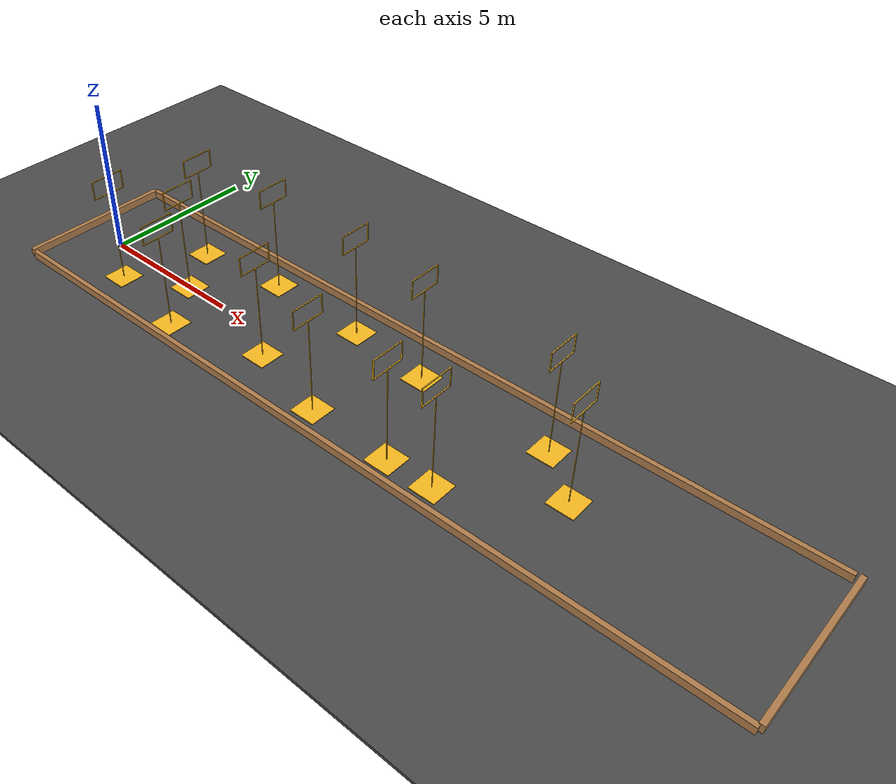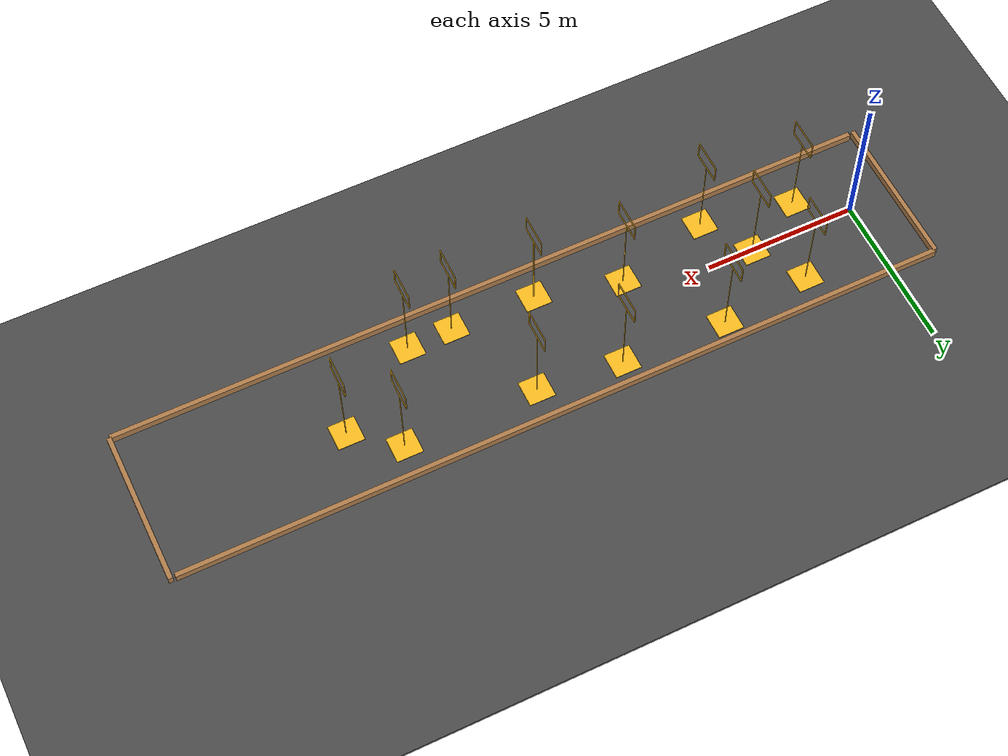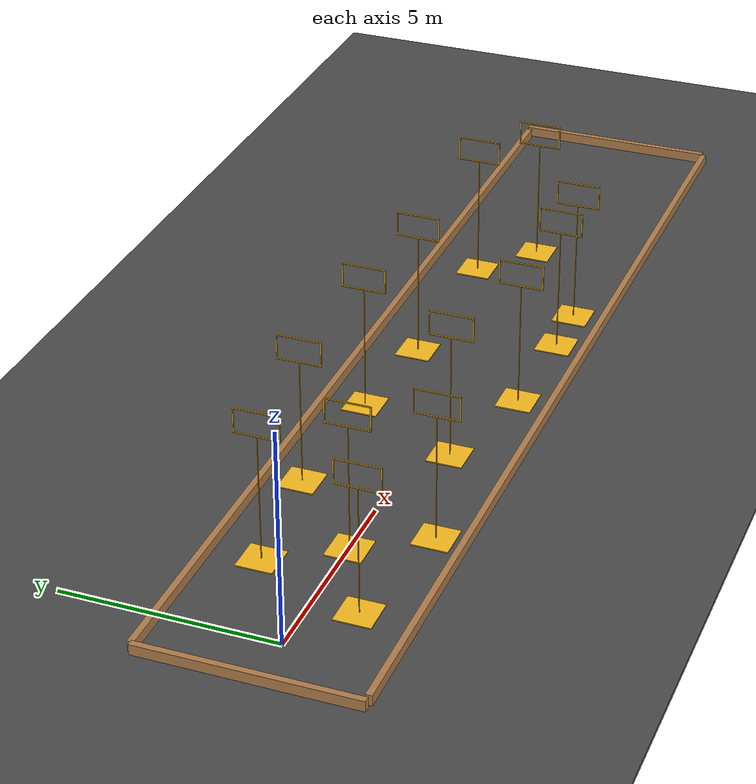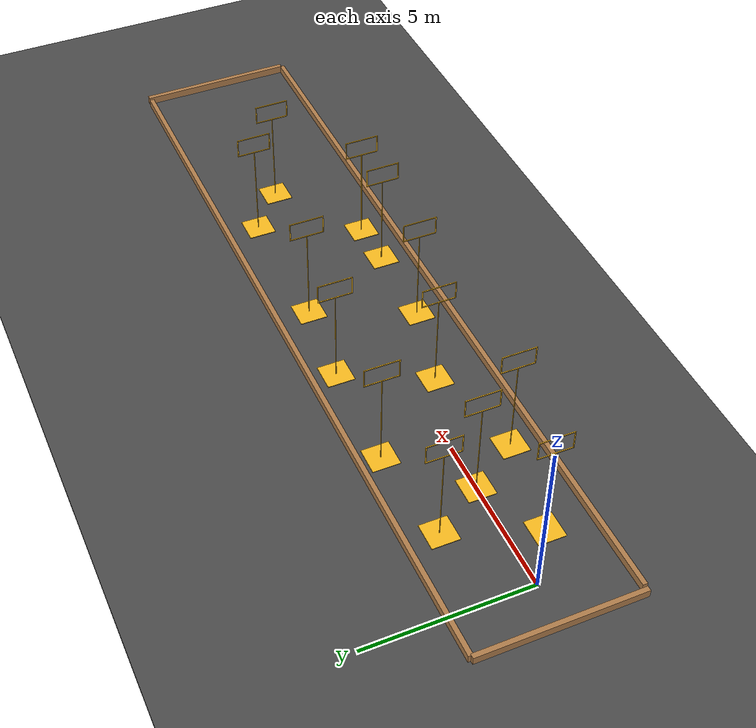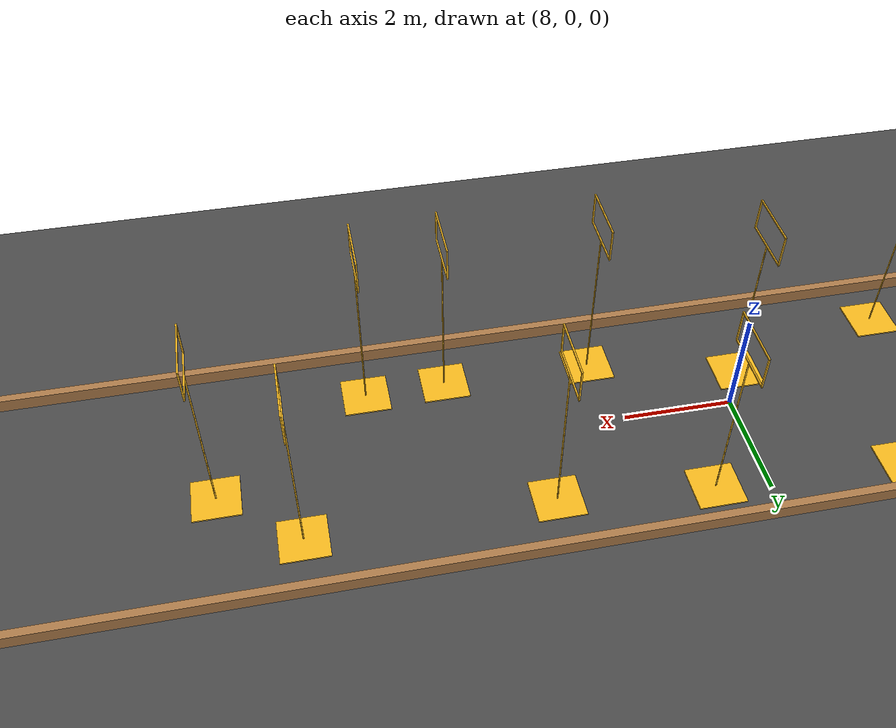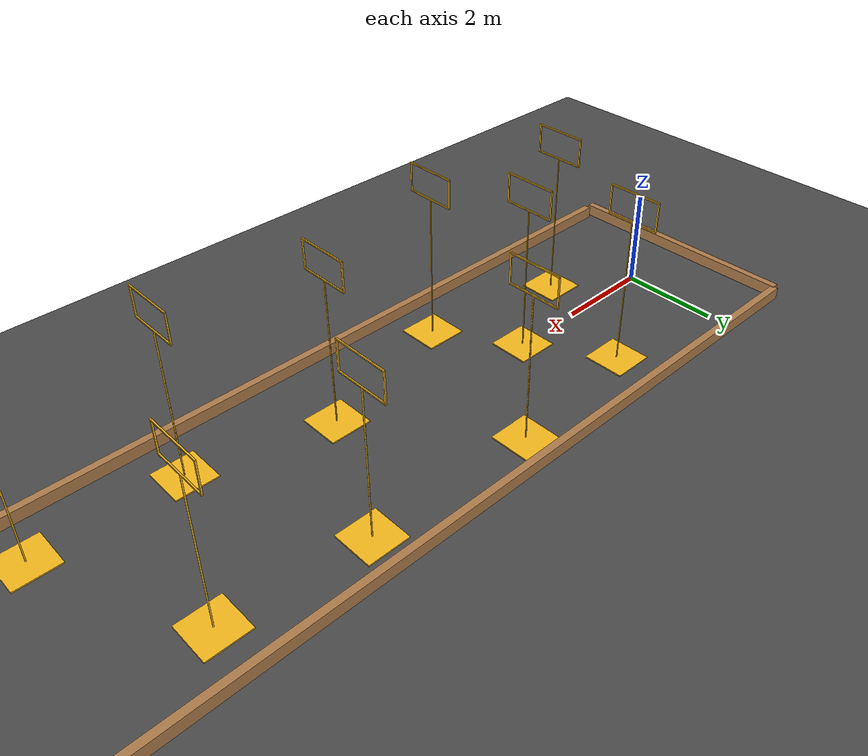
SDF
<sdf version="1.6">
 <world name="default">
  <light name="sun" type="directional">
   <pose>0 0 10 0 -0 0</pose>
   <diffuse>0.8 0.8 0.8 1</diffuse>
   <specular>0.2 0.2 0.2 1</specular>
   <attenuation>
    <range>1000</range>
    <constant>0.9</constant>
    <linear>0.01</linear>
    <quadratic>0.001</quadratic>
   </attenuation>
   <direction>-0.5 0.1 -0.9</direction>
  </light>
  <model name="ground_plane">
   <static>1</static>
   <link name="link">
    <collision name="collision">
     <geometry><plane><normal>0 0 1</normal><size>100 100</size></plane></geometry>
     <surface>
      <contact><collide_bitmask>65535</collide_bitmask></contact>
      <friction><ode><mu>100</mu><mu2>50</mu2></ode></friction>
     </surface>
    </collision>
    <visual name="visual">
     <cast_shadows>0</cast_shadows>
     <geometry><plane><normal>0 0 1</normal><size>100 100</size></plane></geometry>
     <material>
      <script><uri>file://media/materials/scripts/gazebo.material</uri><name>Gazebo/Grey</name></script>
     </material>
    </visual>
   </link>
  </model>
  <gravity>0 0 -9.8</gravity>
  <magnetic_field>6e-06 2.3e-05 -4.2e-05</magnetic_field>
  <atmosphere type="adiabatic"/>
  <physics name="default_physics" default="0" type="ode">
   <max_step_size>0.001</max_step_size>
   <real_time_factor>1</real_time_factor>
   <real_time_update_rate>1000</real_time_update_rate>
  </physics>
  <scene><ambient>0.4 0.4 0.4 1</ambient><background>0.7 0.7 0.7 1</background><shadows>1</shadows></scene>
  <spherical_coordinates>
   <surface_model>EARTH_WGS84</surface_model>
   <latitude_deg>0</latitude_deg>
   <longitude_deg>0</longitude_deg>
   <elevation>0</elevation>
   <heading_deg>0</heading_deg>
  </spherical_coordinates>
  <model name="Walls_small">
   <link name="Wall_8">
    <pose>2.47757 0.056889 0 0 0 -1.5708</pose>
    <inertial>
     <mass>1</mass>
     <inertia><ixx>1</ixx><ixy>0</ixy><ixz>0</ixz><iyy>1</iyy><iyz>0</iyz><izz>1</izz></inertia>
    </inertial>
    <visual name="Wall_8_Visual">
     <pose>0 0 0.25 0 -0 0</pose>
     <geometry><box><size>25 0.15 0.25</size></box></geometry>
     <material>
      <script><uri>file://media/materials/scripts/gazebo.material</uri><name>Gazebo/Wood</name></script>
      <ambient>1 1 1 1</ambient>
      <shader type="pixel"><normal_map>__default__</normal_map></shader>
      <diffuse>1 1 1 1</diffuse>
      <specular>0.2 0.2 0.2 1</specular>
      <emissive>0 0 0 1</emissive>
     </material>
     <meta><layer>0</layer></meta>
    </visual>
    <collision name="Wall_8_Collision">
     <pose>0 0 0.25 0 -0 0</pose>
     <geometry><box><size>25 0.15 0.25</size></box></geometry>
     <surface>
      <friction>
       <ode><mu>1</mu><mu2>1</mu2><fdir1>0 0 0</fdir1><slip1>0</slip1><slip2>0</slip2></ode>
       <torsional>
        <coefficient>1</coefficient>
        <patch_radius>0</patch_radius>
        <surface_radius>0</surface_radius>
        <use_patch_radius>1</use_patch_radius>
        <ode><slip>0</slip></ode>
       </torsional>
      </friction>
      <bounce><restitution_coefficient>0</restitution_coefficient><threshold>1e+06</threshold></bounce>
      <contact>
       <collide_without_contact>0</collide_without_contact>
       <collide_without_contact_bitmask>1</collide_without_contact_bitmask>
       <collide_bitmask>1</collide_bitmask>
       <ode>
        <soft_cfm>0</soft_cfm>
        <soft_erp>0.2</soft_erp>
        <kp>1e+13</kp>
        <kd>1</kd>
        <max_vel>0.01</max_vel>
        <min_depth>0</min_depth>
       </ode>
       <bullet>
        <split_impulse>1</split_impulse>
        <split_impulse_penetration_threshold>-0.01</split_impulse_penetration_threshold>
        <soft_cfm>0</soft_cfm>
        <soft_erp>0.2</soft_erp>
        <kp>1e+13</kp>
        <kd>1</kd>
       </bullet>
      </contact>
     </surface>
    </collision>
   </link>
   <link name="Wall_8_clone">
    <pose>-2.50309 -0.064141 0 0 0 -1.5708</pose>
    <inertial>
     <mass>1</mass>
     <inertia><ixx>1</ixx><ixy>0</ixy><ixz>0</ixz><iyy>1</iyy><iyz>0</iyz><izz>1</izz></inertia>
    </inertial>
    <visual name="Wall_8_Visual">
     <pose>0 0 0.25 0 -0 0</pose>
     <geometry><box><size>25 0.15 0.25</size></box></geometry>
     <material>
      <script><uri>file://media/materials/scripts/gazebo.material</uri><name>Gazebo/Wood</name></script>
      <ambient>1 1 1 1</ambient>
      <shader type="pixel"><normal_map>__default__</normal_map></shader>
      <diffuse>1 1 1 1</diffuse>
      <specular>0.2 0.2 0.2 1</specular>
      <emissive>0 0 0 1</emissive>
     </material>
     <meta><layer>0</layer></meta>
    </visual>
    <collision name="Wall_8_Collision">
     <pose>0 0 0.25 0 -0 0</pose>
     <geometry><box><size>25 0.15 0.25</size></box></geometry>
     <surface>
      <friction>
       <ode><mu>1</mu><mu2>1</mu2><fdir1>0 0 0</fdir1><slip1>0</slip1><slip2>0</slip2></ode>
       <torsional>
        <coefficient>1</coefficient>
        <patch_radius>0</patch_radius>
        <surface_radius>0</surface_radius>
        <use_patch_radius>1</use_patch_radius>
        <ode><slip>0</slip></ode>
       </torsional>
      </friction>
      <bounce><restitution_coefficient>0</restitution_coefficient><threshold>1e+06</threshold></bounce>
      <contact>
       <collide_without_contact>0</collide_without_contact>
       <collide_without_contact_bitmask>1</collide_without_contact_bitmask>
       <collide_bitmask>1</collide_bitmask>
       <ode>
        <soft_cfm>0</soft_cfm>
        <soft_erp>0.2</soft_erp>
        <kp>1e+13</kp>
        <kd>1</kd>
        <max_vel>0.01</max_vel>
        <min_depth>0</min_depth>
       </ode>
       <bullet>
        <split_impulse>1</split_impulse>
        <split_impulse_penetration_threshold>-0.01</split_impulse_penetration_threshold>
        <soft_cfm>0</soft_cfm>
        <soft_erp>0.2</soft_erp>
        <kp>1e+13</kp>
        <kd>1</kd>
       </bullet>
      </contact>
     </surface>
    </collision>
   </link>
   <link name="Wall_8_clone_clone">
    <pose>-4.7e-05 -12.5955 0.261789 0 0 -1.5708</pose>
    <inertial>
     <mass>1</mass>
     <inertia><ixx>1</ixx><ixy>0</ixy><ixz>0</ixz><iyy>1</iyy><iyz>0</iyz><izz>1</izz></inertia>
    </inertial>
    <visual name="Wall_8_Visual">
     <pose>0 0 0 0 -0 1.5707</pose>
     <geometry><box><size>5 0.15 0.25</size></box></geometry>
     <material>
      <script><uri>file://media/materials/scripts/gazebo.material</uri><name>Gazebo/Wood</name></script>
      <ambient>1 1 1 1</ambient>
      <shader type="pixel"><normal_map>__default__</normal_map></shader>
      <diffuse>1 1 1 1</diffuse>
      <specular>0.2 0.2 0.2 1</specular>
      <emissive>0 0 0 1</emissive>
     </material>
     <meta><layer>0</layer></meta>
    </visual>
    <collision name="Wall_8_Collision">
     <pose>0 0 0 0 -0 1.5707</pose>
     <geometry><box><size>5 0.15 0.25</size></box></geometry>
     <surface>
      <friction>
       <ode><mu>1</mu><mu2>1</mu2><fdir1>0 0 0</fdir1><slip1>0</slip1><slip2>0</slip2></ode>
       <torsional>
        <coefficient>1</coefficient>
        <patch_radius>0</patch_radius>
        <surface_radius>0</surface_radius>
        <use_patch_radius>1</use_patch_radius>
        <ode><slip>0</slip></ode>
       </torsional>
      </friction>
      <bounce><restitution_coefficient>0</restitution_coefficient><threshold>1e+06</threshold></bounce>
      <contact>
       <collide_without_contact>0</collide_without_contact>
       <collide_without_contact_bitmask>1</collide_without_contact_bitmask>
       <collide_bitmask>1</collide_bitmask>
       <ode>
        <soft_cfm>0</soft_cfm>
        <soft_erp>0.2</soft_erp>
        <kp>1e+13</kp>
        <kd>1</kd>
        <max_vel>0.01</max_vel>
        <min_depth>0</min_depth>
       </ode>
       <bullet>
        <split_impulse>1</split_impulse>
        <split_impulse_penetration_threshold>-0.01</split_impulse_penetration_threshold>
        <soft_cfm>0</soft_cfm>
        <soft_erp>0.2</soft_erp>
        <kp>1e+13</kp>
        <kd>1</kd>
       </bullet>
      </contact>
     </surface>
    </collision>
   </link>
   <link name="Wall_8_clone_clone_clone">
    <pose>-0.061912 12.5852 0.272266 0 0 -1.5708</pose>
    <inertial>
     <mass>1</mass>
     <inertia><ixx>1</ixx><ixy>0</ixy><ixz>0</ixz><iyy>1</iyy><iyz>0</iyz><izz>1</izz></inertia>
    </inertial>
    <visual name="Wall_8_Visual">
     <pose>0 0 0 0 -0 1.5707</pose>
     <geometry><box><size>5 0.15 0.25</size></box></geometry>
     <material>
      <script><uri>file://media/materials/scripts/gazebo.material</uri><name>Gazebo/Wood</name></script>
      <ambient>1 1 1 1</ambient>
      <shader type="pixel"><normal_map>__default__</normal_map></shader>
      <diffuse>1 1 1 1</diffuse>
      <specular>0.2 0.2 0.2 1</specular>
      <emissive>0 0 0 1</emissive>
     </material>
     <meta><layer>0</layer></meta>
    </visual>
    <collision name="Wall_8_Collision">
     <pose>0 0 0 0 -0 1.5707</pose>
     <geometry><box><size>5 0.15 0.25</size></box></geometry>
     <surface>
      <friction>
       <ode><mu>1</mu><mu2>1</mu2><fdir1>0 0 0</fdir1><slip1>0</slip1><slip2>0</slip2></ode>
       <torsional>
        <coefficient>1</coefficient>
        <patch_radius>0</patch_radius>
        <surface_radius>0</surface_radius>
        <use_patch_radius>1</use_patch_radius>
        <ode><slip>0</slip></ode>
       </torsional>
      </friction>
      <bounce><restitution_coefficient>0</restitution_coefficient><threshold>1e+06</threshold></bounce>
      <contact>
       <collide_without_contact>0</collide_without_contact>
       <collide_without_contact_bitmask>1</collide_without_contact_bitmask>
       <collide_bitmask>1</collide_bitmask>
       <ode>
        <soft_cfm>0</soft_cfm>
        <soft_erp>0.2</soft_erp>
        <kp>1e+13</kp>
        <kd>1</kd>
        <max_vel>0.01</max_vel>
        <min_depth>0</min_depth>
       </ode>
       <bullet>
        <split_impulse>1</split_impulse>
        <split_impulse_penetration_threshold>-0.01</split_impulse_penetration_threshold>
        <soft_cfm>0</soft_cfm>
        <soft_erp>0.2</soft_erp>
        <kp>1e+13</kp>
        <kd>1</kd>
       </bullet>
      </contact>
     </surface>
    </collision>
   </link>
   <static>1</static>
   <pose>11.1501 0.155438 0 0 0 -1.5682</pose>
  </model>
  <model name="asphalt_plane">
   <static>1</static>
   <link name="link">
    <collision name="collision"><geometry><box><size>200 200 0.1</size></box></geometry></collision>
    <visual name="visual">
     <cast_shadows>0</cast_shadows>
     <geometry><box><size>200 200 0.1</size></box></geometry>
     <material>
      <script>
       <uri>model://asphalt_plane/materials/scripts</uri>
       <uri>model://asphalt_plane/materials/textures</uri>
       <name>vrc/asphalt</name>
      </script>
     </material>
    </visual>
   </link>
   <pose>-0.07 -0.018561 -0.048 0 -0 0</pose>
  </model>
  <model name="Gate">
   <link name="link_2">
    <inertial>
     <mass>1</mass>
     <inertia>
      <ixx>0.166667</ixx>
      <ixy>0</ixy>
      <ixz>0</ixz>
      <iyy>0.166667</iyy>
      <iyz>0</iyz>
      <izz>0.166667</izz>
     </inertia>
     <pose>0 0 0.0125 0 -0 0</pose>
    </inertial>
    <pose>-0 -0 0.0125 0 -0 0</pose>
    <visual name="visual">
     <geometry><box><size>0.85 0.85 0.025</size></box></geometry>
     <material>
      <lighting>1</lighting>
      <script><uri>file://media/materials/scripts/gazebo.material</uri><name>Gazebo/Grey</name></script>
      <shader type="pixel"><normal_map>__default__</normal_map></shader>
      <ambient>0.988 0.741 0.122 1</ambient>
      <diffuse>0.988 0.741 0.122 1</diffuse>
      <specular>0.988 0.741 0.122 1</specular>
      <emissive>0 0 0 1</emissive>
     </material>
    </visual>
    <collision name="collision">
     <geometry><box><size>0.85 0.85 0.025</size></box></geometry>
     <surface>
      <friction>
       <ode><mu>1</mu><mu2>1</mu2><fdir1>0 0 0</fdir1><slip1>0</slip1><slip2>0</slip2></ode>
       <torsional>
        <coefficient>1</coefficient>
        <patch_radius>0</patch_radius>
        <surface_radius>0</surface_radius>
        <use_patch_radius>1</use_patch_radius>
        <ode><slip>0</slip></ode>
       </torsional>
      </friction>
      <bounce><restitution_coefficient>0</restitution_coefficient><threshold>1e+06</threshold></bounce>
      <contact>
       <collide_without_contact>0</collide_without_contact>
       <collide_without_contact_bitmask>1</collide_without_contact_bitmask>
       <collide_bitmask>1</collide_bitmask>
       <ode>
        <soft_cfm>0</soft_cfm>
        <soft_erp>0.2</soft_erp>
        <kp>1e+13</kp>
        <kd>1</kd>
        <max_vel>0.01</max_vel>
        <min_depth>0</min_depth>
       </ode>
       <bullet>
        <split_impulse>1</split_impulse>
        <split_impulse_penetration_threshold>-0.01</split_impulse_penetration_threshold>
        <soft_cfm>0</soft_cfm>
        <soft_erp>0.2</soft_erp>
        <kp>1e+13</kp>
        <kd>1</kd>
       </bullet>
      </contact>
     </surface>
    </collision>
   </link>
   <link name="link_3">
    <inertial>
     <mass>0.00444894</mass>
     <inertia>
      <ixx>0.00033485</ixx>
      <ixy>0</ixy>
      <ixz>0</ixz>
      <iyy>0.00033485</iyy>
      <iyz>0</iyz>
      <izz>2.61e-06</izz>
     </inertia>
     <pose>0 0 1.525 0 -0 0</pose>
    </inertial>
    <pose>0 0 1.525 0 -0 0</pose>
    <visual name="visual">
     <geometry><cylinder><radius>0.0125</radius><length>3.025</length></cylinder></geometry>
     <material>
      <lighting>1</lighting>
      <script><uri>file://media/materials/scripts/gazebo.material</uri><name>Gazebo/Grey</name></script>
      <shader type="pixel"><normal_map>__default__</normal_map></shader>
      <ambient>0.988 0.741 0.122 1</ambient>
      <diffuse>0.988 0.741 0.122 1</diffuse>
      <specular>0.988 0.741 0.122 1</specular>
      <emissive>0 0 0 1</emissive>
     </material>
    </visual>
    <collision name="collision">
     <geometry><cylinder><radius>0.0125</radius><length>3.025</length></cylinder></geometry>
     <surface>
      <friction>
       <ode><mu>1</mu><mu2>1</mu2><fdir1>0 0 0</fdir1><slip1>0</slip1><slip2>0</slip2></ode>
       <torsional>
        <coefficient>1</coefficient>
        <patch_radius>0</patch_radius>
        <surface_radius>0</surface_radius>
        <use_patch_radius>1</use_patch_radius>
        <ode><slip>0</slip></ode>
       </torsional>
      </friction>
      <bounce><restitution_coefficient>0</restitution_coefficient><threshold>1e+06</threshold></bounce>
      <contact>
       <collide_without_contact>0</collide_without_contact>
       <collide_without_contact_bitmask>1</collide_without_contact_bitmask>
       <collide_bitmask>1</collide_bitmask>
       <ode>
        <soft_cfm>0</soft_cfm>
        <soft_erp>0.2</soft_erp>
        <kp>1e+13</kp>
        <kd>1</kd>
        <max_vel>0.01</max_vel>
        <min_depth>0</min_depth>
       </ode>
       <bullet>
        <split_impulse>1</split_impulse>
        <split_impulse_penetration_threshold>-0.01</split_impulse_penetration_threshold>
        <soft_cfm>0</soft_cfm>
        <soft_erp>0.2</soft_erp>
        <kp>1e+13</kp>
        <kd>1</kd>
       </bullet>
      </contact>
     </surface>
    </collision>
   </link>
   <link name="link_5">
    <inertial>
     <mass>1</mass>
     <inertia>
      <ixx>0.166667</ixx>
      <ixy>0</ixy>
      <ixz>0</ixz>
      <iyy>0.166667</iyy>
      <iyz>0</iyz>
      <izz>0.166667</izz>
     </inertia>
     <pose>0 0 3.0375 0 -0 0</pose>
    </inertial>
    <pose>0 0 3.0375 0 -0 0</pose>
    <visual name="visual">
     <geometry><box><size>0.025 1.05 0.025</size></box></geometry>
     <material>
      <lighting>1</lighting>
      <script><uri>file://media/materials/scripts/gazebo.material</uri><name>Gazebo/Grey</name></script>
      <shader type="pixel"><normal_map>__default__</normal_map></shader>
      <ambient>0.988 0.741 0.122 1</ambient>
      <diffuse>0.988 0.741 0.122 1</diffuse>
      <specular>0.988 0.741 0.122 1</specular>
      <emissive>0 0 0 1</emissive>
     </material>
    </visual>
    <collision name="collision">
     <geometry><box><size>0.025 1.05 0.025</size></box></geometry>
     <surface>
      <friction>
       <ode><mu>1</mu><mu2>1</mu2><fdir1>0 0 0</fdir1><slip1>0</slip1><slip2>0</slip2></ode>
       <torsional>
        <coefficient>1</coefficient>
        <patch_radius>0</patch_radius>
        <surface_radius>0</surface_radius>
        <use_patch_radius>1</use_patch_radius>
        <ode><slip>0</slip></ode>
       </torsional>
      </friction>
      <bounce><restitution_coefficient>0</restitution_coefficient><threshold>1e+06</threshold></bounce>
      <contact>
       <collide_without_contact>0</collide_without_contact>
       <collide_without_contact_bitmask>1</collide_without_contact_bitmask>
       <collide_bitmask>1</collide_bitmask>
       <ode>
        <soft_cfm>0</soft_cfm>
        <soft_erp>0.2</soft_erp>
        <kp>1e+13</kp>
        <kd>1</kd>
        <max_vel>0.01</max_vel>
        <min_depth>0</min_depth>
       </ode>
       <bullet>
        <split_impulse>1</split_impulse>
        <split_impulse_penetration_threshold>-0.01</split_impulse_penetration_threshold>
        <soft_cfm>0</soft_cfm>
        <soft_erp>0.2</soft_erp>
        <kp>1e+13</kp>
        <kd>1</kd>
       </bullet>
      </contact>
     </surface>
    </collision>
   </link>
   <link name="link_5_clone">
    <inertial>
     <mass>1</mass>
     <inertia>
      <ixx>0.166667</ixx>
      <ixy>0</ixy>
      <ixz>0</ixz>
      <iyy>0.166667</iyy>
      <iyz>0</iyz>
      <izz>0.166667</izz>
     </inertia>
     <pose>0 0 3.6125 0 -0 0</pose>
    </inertial>
    <pose>-0 0 3.6125 0 -0 0</pose>
    <visual name="visual">
     <geometry><box><size>0.025 1.05 0.025</size></box></geometry>
     <material>
      <lighting>1</lighting>
      <script><uri>file://media/materials/scripts/gazebo.material</uri><name>Gazebo/Grey</name></script>
      <shader type="pixel"><normal_map>__default__</normal_map></shader>
      <ambient>0.988 0.741 0.122 1</ambient>
      <diffuse>0.988 0.741 0.122 1</diffuse>
      <specular>0.988 0.741 0.122 1</specular>
      <emissive>0 0 0 1</emissive>
     </material>
    </visual>
    <collision name="collision">
     <geometry><box><size>0.025 1.05 0.025</size></box></geometry>
     <surface>
      <friction>
       <ode><mu>1</mu><mu2>1</mu2><fdir1>0 0 0</fdir1><slip1>0</slip1><slip2>0</slip2></ode>
       <torsional>
        <coefficient>1</coefficient>
        <patch_radius>0</patch_radius>
        <surface_radius>0</surface_radius>
        <use_patch_radius>1</use_patch_radius>
        <ode><slip>0</slip></ode>
       </torsional>
      </friction>
      <bounce><restitution_coefficient>0</restitution_coefficient><threshold>1e+06</threshold></bounce>
      <contact>
       <collide_without_contact>0</collide_without_contact>
       <collide_without_contact_bitmask>1</collide_without_contact_bitmask>
       <collide_bitmask>1</collide_bitmask>
       <ode>
        <soft_cfm>0</soft_cfm>
        <soft_erp>0.2</soft_erp>
        <kp>1e+13</kp>
        <kd>1</kd>
        <max_vel>0.01</max_vel>
        <min_depth>0</min_depth>
       </ode>
       <bullet>
        <split_impulse>1</split_impulse>
        <split_impulse_penetration_threshold>-0.01</split_impulse_penetration_threshold>
        <soft_cfm>0</soft_cfm>
        <soft_erp>0.2</soft_erp>
        <kp>1e+13</kp>
        <kd>1</kd>
       </bullet>
      </contact>
     </surface>
    </collision>
   </link>
   <link name="link_6">
    <inertial>
     <mass>1</mass>
     <inertia>
      <ixx>0.166667</ixx>
      <ixy>0</ixy>
      <ixz>0</ixz>
      <iyy>0.166667</iyy>
      <iyz>0</iyz>
      <izz>0.166667</izz>
     </inertia>
     <pose>0 0.5125 3.0375 0 -0 0</pose>
    </inertial>
    <pose>0 0.5125 3.325 0 -0 0</pose>
    <visual name="visual">
     <geometry><box><size>0.025 0.025 0.575</size></box></geometry>
     <material>
      <lighting>1</lighting>
      <script><uri>file://media/materials/scripts/gazebo.material</uri><name>Gazebo/Grey</name></script>
      <shader type="pixel"><normal_map>__default__</normal_map></shader>
      <ambient>0.988 0.741 0.122 1</ambient>
      <diffuse>0.988 0.741 0.122 1</diffuse>
      <specular>0.988 0.741 0.122 1</specular>
      <emissive>0 0 0 1</emissive>
     </material>
    </visual>
    <collision name="collision">
     <geometry><box><size>0.025 0.025 0.575</size></box></geometry>
     <surface>
      <friction>
       <ode><mu>1</mu><mu2>1</mu2><fdir1>0 0 0</fdir1><slip1>0</slip1><slip2>0</slip2></ode>
       <torsional>
        <coefficient>1</coefficient>
        <patch_radius>0</patch_radius>
        <surface_radius>0</surface_radius>
        <use_patch_radius>1</use_patch_radius>
        <ode><slip>0</slip></ode>
       </torsional>
      </friction>
      <bounce><restitution_coefficient>0</restitution_coefficient><threshold>1e+06</threshold></bounce>
      <contact>
       <collide_without_contact>0</collide_without_contact>
       <collide_without_contact_bitmask>1</collide_without_contact_bitmask>
       <collide_bitmask>1</collide_bitmask>
       <ode>
        <soft_cfm>0</soft_cfm>
        <soft_erp>0.2</soft_erp>
        <kp>1e+13</kp>
        <kd>1</kd>
        <max_vel>0.01</max_vel>
        <min_depth>0</min_depth>
       </ode>
       <bullet>
        <split_impulse>1</split_impulse>
        <split_impulse_penetration_threshold>-0.01</split_impulse_penetration_threshold>
        <soft_cfm>0</soft_cfm>
        <soft_erp>0.2</soft_erp>
        <kp>1e+13</kp>
        <kd>1</kd>
       </bullet>
      </contact>
     </surface>
    </collision>
   </link>
   <link name="link_6_clone">
    <inertial>
     <mass>1</mass>
     <inertia>
      <ixx>0.166667</ixx>
      <ixy>0</ixy>
      <ixz>0</ixz>
      <iyy>0.166667</iyy>
      <iyz>0</iyz>
      <izz>0.166667</izz>
     </inertia>
     <pose>0 -0.5125 3.325 0 -0 0</pose>
    </inertial>
    <pose>0 -0.5125 3.325 0 -0 0</pose>
    <visual name="visual">
     <geometry><box><size>0.025 0.025 0.575</size></box></geometry>
     <material>
      <lighting>1</lighting>
      <script><uri>file://media/materials/scripts/gazebo.material</uri><name>Gazebo/Grey</name></script>
      <shader type="pixel"><normal_map>__default__</normal_map></shader>
      <ambient>0.988 0.741 0.122 1</ambient>
      <diffuse>0.988 0.741 0.122 1</diffuse>
      <specular>0.988 0.741 0.122 1</specular>
      <emissive>0 0 0 1</emissive>
     </material>
    </visual>
    <collision name="collision">
     <geometry><box><size>0.025 0.025 0.575</size></box></geometry>
     <surface>
      <friction>
       <ode><mu>1</mu><mu2>1</mu2><fdir1>0 0 0</fdir1><slip1>0</slip1><slip2>0</slip2></ode>
       <torsional>
        <coefficient>1</coefficient>
        <patch_radius>0</patch_radius>
        <surface_radius>0</surface_radius>
        <use_patch_radius>1</use_patch_radius>
        <ode><slip>0</slip></ode>
       </torsional>
      </friction>
      <bounce><restitution_coefficient>0</restitution_coefficient><threshold>1e+06</threshold></bounce>
      <contact>
       <collide_without_contact>0</collide_without_contact>
       <collide_without_contact_bitmask>1</collide_without_contact_bitmask>
       <collide_bitmask>1</collide_bitmask>
       <ode>
        <soft_cfm>0</soft_cfm>
        <soft_erp>0.2</soft_erp>
        <kp>1e+13</kp>
        <kd>1</kd>
        <max_vel>0.01</max_vel>
        <min_depth>0</min_depth>
       </ode>
       <bullet>
        <split_impulse>1</split_impulse>
        <split_impulse_penetration_threshold>-0.01</split_impulse_penetration_threshold>
        <soft_cfm>0</soft_cfm>
        <soft_erp>0.2</soft_erp>
        <kp>1e+13</kp>
        <kd>1</kd>
       </bullet>
      </contact>
     </surface>
    </collision>
   </link>
   <joint name="link_2_JOINT_2" type="fixed">
    <parent>link_2</parent>
    <child>link_3</child>
    <physics>
     <ode><limit><cfm>0</cfm><erp>0.2</erp></limit><suspension><cfm>0</cfm><erp>0.2</erp></suspension></ode>
    </physics>
   </joint>
   <joint name="link_3_JOINT_3" type="fixed">
    <parent>link_3</parent>
    <child>link_5</child>
    <physics>
     <ode><limit><cfm>0</cfm><erp>0.2</erp></limit><suspension><cfm>0</cfm><erp>0.2</erp></suspension></ode>
    </physics>
   </joint>
   <joint name="link_5_JOINT_0" type="fixed">
    <parent>link_5</parent>
    <child>link_6_clone</child>
    <physics>
     <ode><limit><cfm>0</cfm><erp>0.2</erp></limit><suspension><cfm>0</cfm><erp>0.2</erp></suspension></ode>
    </physics>
   </joint>
   <joint name="link_5_JOINT_1" type="fixed">
    <parent>link_5</parent>
    <child>link_6</child>
    <physics>
     <ode><limit><cfm>0</cfm><erp>0.2</erp></limit><suspension><cfm>0</cfm><erp>0.2</erp></suspension></ode>
    </physics>
   </joint>
   <joint name="link_6_JOINT_3" type="fixed">
    <parent>link_6</parent>
    <child>link_5_clone</child>
    <physics>
     <ode><limit><cfm>0</cfm><erp>0.2</erp></limit><suspension><cfm>0</cfm><erp>0.2</erp></suspension></ode>
    </physics>
   </joint>
   <joint name="link_6_clone_JOINT_2" type="fixed">
    <parent>link_6_clone</parent>
    <child>link_5_clone</child>
    <physics>
     <ode><limit><cfm>0</cfm><erp>0.2</erp></limit><suspension><cfm>0</cfm><erp>0.2</erp></suspension></ode>
    </physics>
   </joint>
   <static>0</static>
   <pose>1.50002 -1.03731 0.002 0 -0 0</pose>
  </model>
  <model name="Gate_0">
   <link name="link_2">
    <inertial>
     <mass>1</mass>
     <inertia>
      <ixx>0.166667</ixx>
      <ixy>0</ixy>
      <ixz>0</ixz>
      <iyy>0.166667</iyy>
      <iyz>0</iyz>
      <izz>0.166667</izz>
     </inertia>
     <pose>0 0 0.0125 0 -0 0</pose>
    </inertial>
    <pose>-0 -0 0.0125 0 -0 0</pose>
    <visual name="visual">
     <geometry><box><size>0.85 0.85 0.025</size></box></geometry>
     <material>
      <lighting>1</lighting>
      <script><uri>file://media/materials/scripts/gazebo.material</uri><name>Gazebo/Grey</name></script>
      <shader type="pixel"><normal_map>__default__</normal_map></shader>
      <ambient>0.988 0.741 0.122 1</ambient>
      <diffuse>0.988 0.741 0.122 1</diffuse>
      <specular>0.988 0.741 0.122 1</specular>
      <emissive>0 0 0 1</emissive>
     </material>
    </visual>
    <collision name="collision">
     <geometry><box><size>0.85 0.85 0.025</size></box></geometry>
     <surface>
      <friction>
       <ode><mu>1</mu><mu2>1</mu2><fdir1>0 0 0</fdir1><slip1>0</slip1><slip2>0</slip2></ode>
       <torsional>
        <coefficient>1</coefficient>
        <patch_radius>0</patch_radius>
        <surface_radius>0</surface_radius>
        <use_patch_radius>1</use_patch_radius>
        <ode><slip>0</slip></ode>
       </torsional>
      </friction>
      <bounce><restitution_coefficient>0</restitution_coefficient><threshold>1e+06</threshold></bounce>
      <contact>
       <collide_without_contact>0</collide_without_contact>
       <collide_without_contact_bitmask>1</collide_without_contact_bitmask>
       <collide_bitmask>1</collide_bitmask>
       <ode>
        <soft_cfm>0</soft_cfm>
        <soft_erp>0.2</soft_erp>
        <kp>1e+13</kp>
        <kd>1</kd>
        <max_vel>0.01</max_vel>
        <min_depth>0</min_depth>
       </ode>
       <bullet>
        <split_impulse>1</split_impulse>
        <split_impulse_penetration_threshold>-0.01</split_impulse_penetration_threshold>
        <soft_cfm>0</soft_cfm>
        <soft_erp>0.2</soft_erp>
        <kp>1e+13</kp>
        <kd>1</kd>
       </bullet>
      </contact>
     </surface>
    </collision>
   </link>
   <link name="link_3">
    <inertial>
     <mass>0.00444894</mass>
     <inertia>
      <ixx>0.00033485</ixx>
      <ixy>0</ixy>
      <ixz>0</ixz>
      <iyy>0.00033485</iyy>
      <iyz>0</iyz>
      <izz>2.61e-06</izz>
     </inertia>
     <pose>0 0 1.525 0 -0 0</pose>
    </inertial>
    <pose>0 0 1.525 0 -0 0</pose>
    <visual name="visual">
     <geometry><cylinder><radius>0.0125</radius><length>3.025</length></cylinder></geometry>
     <material>
      <lighting>1</lighting>
      <script><uri>file://media/materials/scripts/gazebo.material</uri><name>Gazebo/Grey</name></script>
      <shader type="pixel"><normal_map>__default__</normal_map></shader>
      <ambient>0.988 0.741 0.122 1</ambient>
      <diffuse>0.988 0.741 0.122 1</diffuse>
      <specular>0.988 0.741 0.122 1</specular>
      <emissive>0 0 0 1</emissive>
     </material>
    </visual>
    <collision name="collision">
     <geometry><cylinder><radius>0.0125</radius><length>3.025</length></cylinder></geometry>
     <surface>
      <friction>
       <ode><mu>1</mu><mu2>1</mu2><fdir1>0 0 0</fdir1><slip1>0</slip1><slip2>0</slip2></ode>
       <torsional>
        <coefficient>1</coefficient>
        <patch_radius>0</patch_radius>
        <surface_radius>0</surface_radius>
        <use_patch_radius>1</use_patch_radius>
        <ode><slip>0</slip></ode>
       </torsional>
      </friction>
      <bounce><restitution_coefficient>0</restitution_coefficient><threshold>1e+06</threshold></bounce>
      <contact>
       <collide_without_contact>0</collide_without_contact>
       <collide_without_contact_bitmask>1</collide_without_contact_bitmask>
       <collide_bitmask>1</collide_bitmask>
       <ode>
        <soft_cfm>0</soft_cfm>
        <soft_erp>0.2</soft_erp>
        <kp>1e+13</kp>
        <kd>1</kd>
        <max_vel>0.01</max_vel>
        <min_depth>0</min_depth>
       </ode>
       <bullet>
        <split_impulse>1</split_impulse>
        <split_impulse_penetration_threshold>-0.01</split_impulse_penetration_threshold>
        <soft_cfm>0</soft_cfm>
        <soft_erp>0.2</soft_erp>
        <kp>1e+13</kp>
        <kd>1</kd>
       </bullet>
      </contact>
     </surface>
    </collision>
   </link>
   <link name="link_5">
    <inertial>
     <mass>1</mass>
     <inertia>
      <ixx>0.166667</ixx>
      <ixy>0</ixy>
      <ixz>0</ixz>
      <iyy>0.166667</iyy>
      <iyz>0</iyz>
      <izz>0.166667</izz>
     </inertia>
     <pose>0 0 3.0375 0 -0 0</pose>
    </inertial>
    <pose>0 0 3.0375 0 -0 0</pose>
    <visual name="visual">
     <geometry><box><size>0.025 1.05 0.025</size></box></geometry>
     <material>
      <lighting>1</lighting>
      <script><uri>file://media/materials/scripts/gazebo.material</uri><name>Gazebo/Grey</name></script>
      <shader type="pixel"><normal_map>__default__</normal_map></shader>
      <ambient>0.988 0.741 0.122 1</ambient>
      <diffuse>0.988 0.741 0.122 1</diffuse>
      <specular>0.988 0.741 0.122 1</specular>
      <emissive>0 0 0 1</emissive>
     </material>
    </visual>
    <collision name="collision">
     <geometry><box><size>0.025 1.05 0.025</size></box></geometry>
     <surface>
      <friction>
       <ode><mu>1</mu><mu2>1</mu2><fdir1>0 0 0</fdir1><slip1>0</slip1><slip2>0</slip2></ode>
       <torsional>
        <coefficient>1</coefficient>
        <patch_radius>0</patch_radius>
        <surface_radius>0</surface_radius>
        <use_patch_radius>1</use_patch_radius>
        <ode><slip>0</slip></ode>
       </torsional>
      </friction>
      <bounce><restitution_coefficient>0</restitution_coefficient><threshold>1e+06</threshold></bounce>
      <contact>
       <collide_without_contact>0</collide_without_contact>
       <collide_without_contact_bitmask>1</collide_without_contact_bitmask>
       <collide_bitmask>1</collide_bitmask>
       <ode>
        <soft_cfm>0</soft_cfm>
        <soft_erp>0.2</soft_erp>
        <kp>1e+13</kp>
        <kd>1</kd>
        <max_vel>0.01</max_vel>
        <min_depth>0</min_depth>
       </ode>
       <bullet>
        <split_impulse>1</split_impulse>
        <split_impulse_penetration_threshold>-0.01</split_impulse_penetration_threshold>
        <soft_cfm>0</soft_cfm>
        <soft_erp>0.2</soft_erp>
        <kp>1e+13</kp>
        <kd>1</kd>
       </bullet>
      </contact>
     </surface>
    </collision>
   </link>
   <link name="link_5_clone">
    <inertial>
     <mass>1</mass>
     <inertia>
      <ixx>0.166667</ixx>
      <ixy>0</ixy>
      <ixz>0</ixz>
      <iyy>0.166667</iyy>
      <iyz>0</iyz>
      <izz>0.166667</izz>
     </inertia>
     <pose>0 0 3.6125 0 -0 0</pose>
    </inertial>
    <pose>-0 0 3.6125 0 -0 0</pose>
    <visual name="visual">
     <geometry><box><size>0.025 1.05 0.025</size></box></geometry>
     <material>
      <lighting>1</lighting>
      <script><uri>file://media/materials/scripts/gazebo.material</uri><name>Gazebo/Grey</name></script>
      <shader type="pixel"><normal_map>__default__</normal_map></shader>
      <ambient>0.988 0.741 0.122 1</ambient>
      <diffuse>0.988 0.741 0.122 1</diffuse>
      <specular>0.988 0.741 0.122 1</specular>
      <emissive>0 0 0 1</emissive>
     </material>
    </visual>
    <collision name="collision">
     <geometry><box><size>0.025 1.05 0.025</size></box></geometry>
     <surface>
      <friction>
       <ode><mu>1</mu><mu2>1</mu2><fdir1>0 0 0</fdir1><slip1>0</slip1><slip2>0</slip2></ode>
       <torsional>
        <coefficient>1</coefficient>
        <patch_radius>0</patch_radius>
        <surface_radius>0</surface_radius>
        <use_patch_radius>1</use_patch_radius>
        <ode><slip>0</slip></ode>
       </torsional>
      </friction>
      <bounce><restitution_coefficient>0</restitution_coefficient><threshold>1e+06</threshold></bounce>
      <contact>
       <collide_without_contact>0</collide_without_contact>
       <collide_without_contact_bitmask>1</collide_without_contact_bitmask>
       <collide_bitmask>1</collide_bitmask>
       <ode>
        <soft_cfm>0</soft_cfm>
        <soft_erp>0.2</soft_erp>
        <kp>1e+13</kp>
        <kd>1</kd>
        <max_vel>0.01</max_vel>
        <min_depth>0</min_depth>
       </ode>
       <bullet>
        <split_impulse>1</split_impulse>
        <split_impulse_penetration_threshold>-0.01</split_impulse_penetration_threshold>
        <soft_cfm>0</soft_cfm>
        <soft_erp>0.2</soft_erp>
        <kp>1e+13</kp>
        <kd>1</kd>
       </bullet>
      </contact>
     </surface>
    </collision>
   </link>
   <link name="link_6">
    <inertial>
     <mass>1</mass>
     <inertia>
      <ixx>0.166667</ixx>
      <ixy>0</ixy>
      <ixz>0</ixz>
      <iyy>0.166667</iyy>
      <iyz>0</iyz>
      <izz>0.166667</izz>
     </inertia>
     <pose>0 0.5125 3.0375 0 -0 0</pose>
    </inertial>
    <pose>0 0.5125 3.325 0 -0 0</pose>
    <visual name="visual">
     <geometry><box><size>0.025 0.025 0.575</size></box></geometry>
     <material>
      <lighting>1</lighting>
      <script><uri>file://media/materials/scripts/gazebo.material</uri><name>Gazebo/Grey</name></script>
      <shader type="pixel"><normal_map>__default__</normal_map></shader>
      <ambient>0.988 0.741 0.122 1</ambient>
      <diffuse>0.988 0.741 0.122 1</diffuse>
      <specular>0.988 0.741 0.122 1</specular>
      <emissive>0 0 0 1</emissive>
     </material>
    </visual>
    <collision name="collision">
     <geometry><box><size>0.025 0.025 0.575</size></box></geometry>
     <surface>
      <friction>
       <ode><mu>1</mu><mu2>1</mu2><fdir1>0 0 0</fdir1><slip1>0</slip1><slip2>0</slip2></ode>
       <torsional>
        <coefficient>1</coefficient>
        <patch_radius>0</patch_radius>
        <surface_radius>0</surface_radius>
        <use_patch_radius>1</use_patch_radius>
        <ode><slip>0</slip></ode>
       </torsional>
      </friction>
      <bounce><restitution_coefficient>0</restitution_coefficient><threshold>1e+06</threshold></bounce>
      <contact>
       <collide_without_contact>0</collide_without_contact>
       <collide_without_contact_bitmask>1</collide_without_contact_bitmask>
       <collide_bitmask>1</collide_bitmask>
       <ode>
        <soft_cfm>0</soft_cfm>
        <soft_erp>0.2</soft_erp>
        <kp>1e+13</kp>
        <kd>1</kd>
        <max_vel>0.01</max_vel>
        <min_depth>0</min_depth>
       </ode>
       <bullet>
        <split_impulse>1</split_impulse>
        <split_impulse_penetration_threshold>-0.01</split_impulse_penetration_threshold>
        <soft_cfm>0</soft_cfm>
        <soft_erp>0.2</soft_erp>
        <kp>1e+13</kp>
        <kd>1</kd>
       </bullet>
      </contact>
     </surface>
    </collision>
   </link>
   <link name="link_6_clone">
    <inertial>
     <mass>1</mass>
     <inertia>
      <ixx>0.166667</ixx>
      <ixy>0</ixy>
      <ixz>0</ixz>
      <iyy>0.166667</iyy>
      <iyz>0</iyz>
      <izz>0.166667</izz>
     </inertia>
     <pose>0 -0.5125 3.325 0 -0 0</pose>
    </inertial>
    <pose>0 -0.5125 3.325 0 -0 0</pose>
    <visual name="visual">
     <geometry><box><size>0.025 0.025 0.575</size></box></geometry>
     <material>
      <lighting>1</lighting>
      <script><uri>file://media/materials/scripts/gazebo.material</uri><name>Gazebo/Grey</name></script>
      <shader type="pixel"><normal_map>__default__</normal_map></shader>
      <ambient>0.988 0.741 0.122 1</ambient>
      <diffuse>0.988 0.741 0.122 1</diffuse>
      <specular>0.988 0.741 0.122 1</specular>
      <emissive>0 0 0 1</emissive>
     </material>
    </visual>
    <collision name="collision">
     <geometry><box><size>0.025 0.025 0.575</size></box></geometry>
     <surface>
      <friction>
       <ode><mu>1</mu><mu2>1</mu2><fdir1>0 0 0</fdir1><slip1>0</slip1><slip2>0</slip2></ode>
       <torsional>
        <coefficient>1</coefficient>
        <patch_radius>0</patch_radius>
        <surface_radius>0</surface_radius>
        <use_patch_radius>1</use_patch_radius>
        <ode><slip>0</slip></ode>
       </torsional>
      </friction>
      <bounce><restitution_coefficient>0</restitution_coefficient><threshold>1e+06</threshold></bounce>
      <contact>
       <collide_without_contact>0</collide_without_contact>
       <collide_without_contact_bitmask>1</collide_without_contact_bitmask>
       <collide_bitmask>1</collide_bitmask>
       <ode>
        <soft_cfm>0</soft_cfm>
        <soft_erp>0.2</soft_erp>
        <kp>1e+13</kp>
        <kd>1</kd>
        <max_vel>0.01</max_vel>
        <min_depth>0</min_depth>
       </ode>
       <bullet>
        <split_impulse>1</split_impulse>
        <split_impulse_penetration_threshold>-0.01</split_impulse_penetration_threshold>
        <soft_cfm>0</soft_cfm>
        <soft_erp>0.2</soft_erp>
        <kp>1e+13</kp>
        <kd>1</kd>
       </bullet>
      </contact>
     </surface>
    </collision>
   </link>
   <joint name="link_2_JOINT_2" type="fixed">
    <parent>link_2</parent>
    <child>link_3</child>
    <physics>
     <ode><limit><cfm>0</cfm><erp>0.2</erp></limit><suspension><cfm>0</cfm><erp>0.2</erp></suspension></ode>
    </physics>
   </joint>
   <joint name="link_3_JOINT_3" type="fixed">
    <parent>link_3</parent>
    <child>link_5</child>
    <physics>
     <ode><limit><cfm>0</cfm><erp>0.2</erp></limit><suspension><cfm>0</cfm><erp>0.2</erp></suspension></ode>
    </physics>
   </joint>
   <joint name="link_5_JOINT_0" type="fixed">
    <parent>link_5</parent>
    <child>link_6_clone</child>
    <physics>
     <ode><limit><cfm>0</cfm><erp>0.2</erp></limit><suspension><cfm>0</cfm><erp>0.2</erp></suspension></ode>
    </physics>
   </joint>
   <joint name="link_5_JOINT_1" type="fixed">
    <parent>link_5</parent>
    <child>link_6</child>
    <physics>
     <ode><limit><cfm>0</cfm><erp>0.2</erp></limit><suspension><cfm>0</cfm><erp>0.2</erp></suspension></ode>
    </physics>
   </joint>
   <joint name="link_6_JOINT_3" type="fixed">
    <parent>link_6</parent>
    <child>link_5_clone</child>
    <physics>
     <ode><limit><cfm>0</cfm><erp>0.2</erp></limit><suspension><cfm>0</cfm><erp>0.2</erp></suspension></ode>
    </physics>
   </joint>
   <joint name="link_6_clone_JOINT_2" type="fixed">
    <parent>link_6_clone</parent>
    <child>link_5_clone</child>
    <physics>
     <ode><limit><cfm>0</cfm><erp>0.2</erp></limit><suspension><cfm>0</cfm><erp>0.2</erp></suspension></ode>
    </physics>
   </joint>
   <static>0</static>
   <pose>2.50002 1.56729 0.002 0 -0 0</pose>
  </model>
  <model name="Gate_1">
   <link name="link_2">
    <inertial>
     <mass>1</mass>
     <inertia>
      <ixx>0.166667</ixx>
      <ixy>0</ixy>
      <ixz>0</ixz>
      <iyy>0.166667</iyy>
      <iyz>0</iyz>
      <izz>0.166667</izz>
     </inertia>
     <pose>0 0 0.0125 0 -0 0</pose>
    </inertial>
    <pose>-0 -0 0.0125 0 -0 0</pose>
    <visual name="visual">
     <geometry><box><size>0.85 0.85 0.025</size></box></geometry>
     <material>
      <lighting>1</lighting>
      <script><uri>file://media/materials/scripts/gazebo.material</uri><name>Gazebo/Grey</name></script>
      <shader type="pixel"><normal_map>__default__</normal_map></shader>
      <ambient>0.988 0.741 0.122 1</ambient>
      <diffuse>0.988 0.741 0.122 1</diffuse>
      <specular>0.988 0.741 0.122 1</specular>
      <emissive>0 0 0 1</emissive>
     </material>
    </visual>
    <collision name="collision">
     <geometry><box><size>0.85 0.85 0.025</size></box></geometry>
     <surface>
      <friction>
       <ode><mu>1</mu><mu2>1</mu2><fdir1>0 0 0</fdir1><slip1>0</slip1><slip2>0</slip2></ode>
       <torsional>
        <coefficient>1</coefficient>
        <patch_radius>0</patch_radius>
        <surface_radius>0</surface_radius>
        <use_patch_radius>1</use_patch_radius>
        <ode><slip>0</slip></ode>
       </torsional>
      </friction>
      <bounce><restitution_coefficient>0</restitution_coefficient><threshold>1e+06</threshold></bounce>
      <contact>
       <collide_without_contact>0</collide_without_contact>
       <collide_without_contact_bitmask>1</collide_without_contact_bitmask>
       <collide_bitmask>1</collide_bitmask>
       <ode>
        <soft_cfm>0</soft_cfm>
        <soft_erp>0.2</soft_erp>
        <kp>1e+13</kp>
        <kd>1</kd>
        <max_vel>0.01</max_vel>
        <min_depth>0</min_depth>
       </ode>
       <bullet>
        <split_impulse>1</split_impulse>
        <split_impulse_penetration_threshold>-0.01</split_impulse_penetration_threshold>
        <soft_cfm>0</soft_cfm>
        <soft_erp>0.2</soft_erp>
        <kp>1e+13</kp>
        <kd>1</kd>
       </bullet>
      </contact>
     </surface>
    </collision>
   </link>
   <link name="link_3">
    <inertial>
     <mass>0.00444894</mass>
     <inertia>
      <ixx>0.00033485</ixx>
      <ixy>0</ixy>
      <ixz>0</ixz>
      <iyy>0.00033485</iyy>
      <iyz>0</iyz>
      <izz>2.61e-06</izz>
     </inertia>
     <pose>0 0 1.525 0 -0 0</pose>
    </inertial>
    <pose>0 0 1.525 0 -0 0</pose>
    <visual name="visual">
     <geometry><cylinder><radius>0.0125</radius><length>3.025</length></cylinder></geometry>
     <material>
      <lighting>1</lighting>
      <script><uri>file://media/materials/scripts/gazebo.material</uri><name>Gazebo/Grey</name></script>
      <shader type="pixel"><normal_map>__default__</normal_map></shader>
      <ambient>0.988 0.741 0.122 1</ambient>
      <diffuse>0.988 0.741 0.122 1</diffuse>
      <specular>0.988 0.741 0.122 1</specular>
      <emissive>0 0 0 1</emissive>
     </material>
    </visual>
    <collision name="collision">
     <geometry><cylinder><radius>0.0125</radius><length>3.025</length></cylinder></geometry>
     <surface>
      <friction>
       <ode><mu>1</mu><mu2>1</mu2><fdir1>0 0 0</fdir1><slip1>0</slip1><slip2>0</slip2></ode>
       <torsional>
        <coefficient>1</coefficient>
        <patch_radius>0</patch_radius>
        <surface_radius>0</surface_radius>
        <use_patch_radius>1</use_patch_radius>
        <ode><slip>0</slip></ode>
       </torsional>
      </friction>
      <bounce><restitution_coefficient>0</restitution_coefficient><threshold>1e+06</threshold></bounce>
      <contact>
       <collide_without_contact>0</collide_without_contact>
       <collide_without_contact_bitmask>1</collide_without_contact_bitmask>
       <collide_bitmask>1</collide_bitmask>
       <ode>
        <soft_cfm>0</soft_cfm>
        <soft_erp>0.2</soft_erp>
        <kp>1e+13</kp>
        <kd>1</kd>
        <max_vel>0.01</max_vel>
        <min_depth>0</min_depth>
       </ode>
       <bullet>
        <split_impulse>1</split_impulse>
        <split_impulse_penetration_threshold>-0.01</split_impulse_penetration_threshold>
        <soft_cfm>0</soft_cfm>
        <soft_erp>0.2</soft_erp>
        <kp>1e+13</kp>
        <kd>1</kd>
       </bullet>
      </contact>
     </surface>
    </collision>
   </link>
   <link name="link_5">
    <inertial>
     <mass>1</mass>
     <inertia>
      <ixx>0.166667</ixx>
      <ixy>0</ixy>
      <ixz>0</ixz>
      <iyy>0.166667</iyy>
      <iyz>0</iyz>
      <izz>0.166667</izz>
     </inertia>
     <pose>0 0 3.0375 0 -0 0</pose>
    </inertial>
    <pose>0 0 3.0375 0 -0 0</pose>
    <visual name="visual">
     <geometry><box><size>0.025 1.05 0.025</size></box></geometry>
     <material>
      <lighting>1</lighting>
      <script><uri>file://media/materials/scripts/gazebo.material</uri><name>Gazebo/Grey</name></script>
      <shader type="pixel"><normal_map>__default__</normal_map></shader>
      <ambient>0.988 0.741 0.122 1</ambient>
      <diffuse>0.988 0.741 0.122 1</diffuse>
      <specular>0.988 0.741 0.122 1</specular>
      <emissive>0 0 0 1</emissive>
     </material>
    </visual>
    <collision name="collision">
     <geometry><box><size>0.025 1.05 0.025</size></box></geometry>
     <surface>
      <friction>
       <ode><mu>1</mu><mu2>1</mu2><fdir1>0 0 0</fdir1><slip1>0</slip1><slip2>0</slip2></ode>
       <torsional>
        <coefficient>1</coefficient>
        <patch_radius>0</patch_radius>
        <surface_radius>0</surface_radius>
        <use_patch_radius>1</use_patch_radius>
        <ode><slip>0</slip></ode>
       </torsional>
      </friction>
      <bounce><restitution_coefficient>0</restitution_coefficient><threshold>1e+06</threshold></bounce>
      <contact>
       <collide_without_contact>0</collide_without_contact>
       <collide_without_contact_bitmask>1</collide_without_contact_bitmask>
       <collide_bitmask>1</collide_bitmask>
       <ode>
        <soft_cfm>0</soft_cfm>
        <soft_erp>0.2</soft_erp>
        <kp>1e+13</kp>
        <kd>1</kd>
        <max_vel>0.01</max_vel>
        <min_depth>0</min_depth>
       </ode>
       <bullet>
        <split_impulse>1</split_impulse>
        <split_impulse_penetration_threshold>-0.01</split_impulse_penetration_threshold>
        <soft_cfm>0</soft_cfm>
        <soft_erp>0.2</soft_erp>
        <kp>1e+13</kp>
        <kd>1</kd>
       </bullet>
      </contact>
     </surface>
    </collision>
   </link>
   <link name="link_5_clone">
    <inertial>
     <mass>1</mass>
     <inertia>
      <ixx>0.166667</ixx>
      <ixy>0</ixy>
      <ixz>0</ixz>
      <iyy>0.166667</iyy>
      <iyz>0</iyz>
      <izz>0.166667</izz>
     </inertia>
     <pose>0 0 3.6125 0 -0 0</pose>
    </inertial>
    <pose>-0 0 3.6125 0 -0 0</pose>
    <visual name="visual">
     <geometry><box><size>0.025 1.05 0.025</size></box></geometry>
     <material>
      <lighting>1</lighting>
      <script><uri>file://media/materials/scripts/gazebo.material</uri><name>Gazebo/Grey</name></script>
      <shader type="pixel"><normal_map>__default__</normal_map></shader>
      <ambient>0.988 0.741 0.122 1</ambient>
      <diffuse>0.988 0.741 0.122 1</diffuse>
      <specular>0.988 0.741 0.122 1</specular>
      <emissive>0 0 0 1</emissive>
     </material>
    </visual>
    <collision name="collision">
     <geometry><box><size>0.025 1.05 0.025</size></box></geometry>
     <surface>
      <friction>
       <ode><mu>1</mu><mu2>1</mu2><fdir1>0 0 0</fdir1><slip1>0</slip1><slip2>0</slip2></ode>
       <torsional>
        <coefficient>1</coefficient>
        <patch_radius>0</patch_radius>
        <surface_radius>0</surface_radius>
        <use_patch_radius>1</use_patch_radius>
        <ode><slip>0</slip></ode>
       </torsional>
      </friction>
      <bounce><restitution_coefficient>0</restitution_coefficient><threshold>1e+06</threshold></bounce>
      <contact>
       <collide_without_contact>0</collide_without_contact>
       <collide_without_contact_bitmask>1</collide_without_contact_bitmask>
       <collide_bitmask>1</collide_bitmask>
       <ode>
        <soft_cfm>0</soft_cfm>
        <soft_erp>0.2</soft_erp>
        <kp>1e+13</kp>
        <kd>1</kd>
        <max_vel>0.01</max_vel>
        <min_depth>0</min_depth>
       </ode>
       <bullet>
        <split_impulse>1</split_impulse>
        <split_impulse_penetration_threshold>-0.01</split_impulse_penetration_threshold>
        <soft_cfm>0</soft_cfm>
        <soft_erp>0.2</soft_erp>
        <kp>1e+13</kp>
        <kd>1</kd>
       </bullet>
      </contact>
     </surface>
    </collision>
   </link>
   <link name="link_6">
    <inertial>
     <mass>1</mass>
     <inertia>
      <ixx>0.166667</ixx>
      <ixy>0</ixy>
      <ixz>0</ixz>
      <iyy>0.166667</iyy>
      <iyz>0</iyz>
      <izz>0.166667</izz>
     </inertia>
     <pose>0 0.5125 3.0375 0 -0 0</pose>
    </inertial>
    <pose>0 0.5125 3.325 0 -0 0</pose>
    <visual name="visual">
     <geometry><box><size>0.025 0.025 0.575</size></box></geometry>
     <material>
      <lighting>1</lighting>
      <script><uri>file://media/materials/scripts/gazebo.material</uri><name>Gazebo/Grey</name></script>
      <shader type="pixel"><normal_map>__default__</normal_map></shader>
      <ambient>0.988 0.741 0.122 1</ambient>
      <diffuse>0.988 0.741 0.122 1</diffuse>
      <specular>0.988 0.741 0.122 1</specular>
      <emissive>0 0 0 1</emissive>
     </material>
    </visual>
    <collision name="collision">
     <geometry><box><size>0.025 0.025 0.575</size></box></geometry>
     <surface>
      <friction>
       <ode><mu>1</mu><mu2>1</mu2><fdir1>0 0 0</fdir1><slip1>0</slip1><slip2>0</slip2></ode>
       <torsional>
        <coefficient>1</coefficient>
        <patch_radius>0</patch_radius>
        <surface_radius>0</surface_radius>
        <use_patch_radius>1</use_patch_radius>
        <ode><slip>0</slip></ode>
       </torsional>
      </friction>
      <bounce><restitution_coefficient>0</restitution_coefficient><threshold>1e+06</threshold></bounce>
      <contact>
       <collide_without_contact>0</collide_without_contact>
       <collide_without_contact_bitmask>1</collide_without_contact_bitmask>
       <collide_bitmask>1</collide_bitmask>
       <ode>
        <soft_cfm>0</soft_cfm>
        <soft_erp>0.2</soft_erp>
        <kp>1e+13</kp>
        <kd>1</kd>
        <max_vel>0.01</max_vel>
        <min_depth>0</min_depth>
       </ode>
       <bullet>
        <split_impulse>1</split_impulse>
        <split_impulse_penetration_threshold>-0.01</split_impulse_penetration_threshold>
        <soft_cfm>0</soft_cfm>
        <soft_erp>0.2</soft_erp>
        <kp>1e+13</kp>
        <kd>1</kd>
       </bullet>
      </contact>
     </surface>
    </collision>
   </link>
   <link name="link_6_clone">
    <inertial>
     <mass>1</mass>
     <inertia>
      <ixx>0.166667</ixx>
      <ixy>0</ixy>
      <ixz>0</ixz>
      <iyy>0.166667</iyy>
      <iyz>0</iyz>
      <izz>0.166667</izz>
     </inertia>
     <pose>0 -0.5125 3.325 0 -0 0</pose>
    </inertial>
    <pose>0 -0.5125 3.325 0 -0 0</pose>
    <visual name="visual">
     <geometry><box><size>0.025 0.025 0.575</size></box></geometry>
     <material>
      <lighting>1</lighting>
      <script><uri>file://media/materials/scripts/gazebo.material</uri><name>Gazebo/Grey</name></script>
      <shader type="pixel"><normal_map>__default__</normal_map></shader>
      <ambient>0.988 0.741 0.122 1</ambient>
      <diffuse>0.988 0.741 0.122 1</diffuse>
      <specular>0.988 0.741 0.122 1</specular>
      <emissive>0 0 0 1</emissive>
     </material>
    </visual>
    <collision name="collision">
     <geometry><box><size>0.025 0.025 0.575</size></box></geometry>
     <surface>
      <friction>
       <ode><mu>1</mu><mu2>1</mu2><fdir1>0 0 0</fdir1><slip1>0</slip1><slip2>0</slip2></ode>
       <torsional>
        <coefficient>1</coefficient>
        <patch_radius>0</patch_radius>
        <surface_radius>0</surface_radius>
        <use_patch_radius>1</use_patch_radius>
        <ode><slip>0</slip></ode>
       </torsional>
      </friction>
      <bounce><restitution_coefficient>0</restitution_coefficient><threshold>1e+06</threshold></bounce>
      <contact>
       <collide_without_contact>0</collide_without_contact>
       <collide_without_contact_bitmask>1</collide_without_contact_bitmask>
       <collide_bitmask>1</collide_bitmask>
       <ode>
        <soft_cfm>0</soft_cfm>
        <soft_erp>0.2</soft_erp>
        <kp>1e+13</kp>
        <kd>1</kd>
        <max_vel>0.01</max_vel>
        <min_depth>0</min_depth>
       </ode>
       <bullet>
        <split_impulse>1</split_impulse>
        <split_impulse_penetration_threshold>-0.01</split_impulse_penetration_threshold>
        <soft_cfm>0</soft_cfm>
        <soft_erp>0.2</soft_erp>
        <kp>1e+13</kp>
        <kd>1</kd>
       </bullet>
      </contact>
     </surface>
    </collision>
   </link>
   <joint name="link_2_JOINT_2" type="fixed">
    <parent>link_2</parent>
    <child>link_3</child>
    <physics>
     <ode><limit><cfm>0</cfm><erp>0.2</erp></limit><suspension><cfm>0</cfm><erp>0.2</erp></suspension></ode>
    </physics>
   </joint>
   <joint name="link_3_JOINT_3" type="fixed">
    <parent>link_3</parent>
    <child>link_5</child>
    <physics>
     <ode><limit><cfm>0</cfm><erp>0.2</erp></limit><suspension><cfm>0</cfm><erp>0.2</erp></suspension></ode>
    </physics>
   </joint>
   <joint name="link_5_JOINT_0" type="fixed">
    <parent>link_5</parent>
    <child>link_6_clone</child>
    <physics>
     <ode><limit><cfm>0</cfm><erp>0.2</erp></limit><suspension><cfm>0</cfm><erp>0.2</erp></suspension></ode>
    </physics>
   </joint>
   <joint name="link_5_JOINT_1" type="fixed">
    <parent>link_5</parent>
    <child>link_6</child>
    <physics>
     <ode><limit><cfm>0</cfm><erp>0.2</erp></limit><suspension><cfm>0</cfm><erp>0.2</erp></suspension></ode>
    </physics>
   </joint>
   <joint name="link_6_JOINT_3" type="fixed">
    <parent>link_6</parent>
    <child>link_5_clone</child>
    <physics>
     <ode><limit><cfm>0</cfm><erp>0.2</erp></limit><suspension><cfm>0</cfm><erp>0.2</erp></suspension></ode>
    </physics>
   </joint>
   <joint name="link_6_clone_JOINT_2" type="fixed">
    <parent>link_6_clone</parent>
    <child>link_5_clone</child>
    <physics>
     <ode><limit><cfm>0</cfm><erp>0.2</erp></limit><suspension><cfm>0</cfm><erp>0.2</erp></suspension></ode>
    </physics>
   </joint>
   <static>0</static>
   <pose>3.50002 -0.012393 0.001962 0 -0 0</pose>
  </model>
  <model name="Gate_2">
   <link name="link_2">
    <inertial>
     <mass>1</mass>
     <inertia>
      <ixx>0.166667</ixx>
      <ixy>0</ixy>
      <ixz>0</ixz>
      <iyy>0.166667</iyy>
      <iyz>0</iyz>
      <izz>0.166667</izz>
     </inertia>
     <pose>0 0 0.0125 0 -0 0</pose>
    </inertial>
    <pose>-0 -0 0.0125 0 -0 0</pose>
    <visual name="visual">
     <geometry><box><size>0.85 0.85 0.025</size></box></geometry>
     <material>
      <lighting>1</lighting>
      <script><uri>file://media/materials/scripts/gazebo.material</uri><name>Gazebo/Grey</name></script>
      <shader type="pixel"><normal_map>__default__</normal_map></shader>
      <ambient>0.988 0.741 0.122 1</ambient>
      <diffuse>0.988 0.741 0.122 1</diffuse>
      <specular>0.988 0.741 0.122 1</specular>
      <emissive>0 0 0 1</emissive>
     </material>
    </visual>
    <collision name="collision">
     <geometry><box><size>0.85 0.85 0.025</size></box></geometry>
     <surface>
      <friction>
       <ode><mu>1</mu><mu2>1</mu2><fdir1>0 0 0</fdir1><slip1>0</slip1><slip2>0</slip2></ode>
       <torsional>
        <coefficient>1</coefficient>
        <patch_radius>0</patch_radius>
        <surface_radius>0</surface_radius>
        <use_patch_radius>1</use_patch_radius>
        <ode><slip>0</slip></ode>
       </torsional>
      </friction>
      <bounce><restitution_coefficient>0</restitution_coefficient><threshold>1e+06</threshold></bounce>
      <contact>
       <collide_without_contact>0</collide_without_contact>
       <collide_without_contact_bitmask>1</collide_without_contact_bitmask>
       <collide_bitmask>1</collide_bitmask>
       <ode>
        <soft_cfm>0</soft_cfm>
        <soft_erp>0.2</soft_erp>
        <kp>1e+13</kp>
        <kd>1</kd>
        <max_vel>0.01</max_vel>
        <min_depth>0</min_depth>
       </ode>
       <bullet>
        <split_impulse>1</split_impulse>
        <split_impulse_penetration_threshold>-0.01</split_impulse_penetration_threshold>
        <soft_cfm>0</soft_cfm>
        <soft_erp>0.2</soft_erp>
        <kp>1e+13</kp>
        <kd>1</kd>
       </bullet>
      </contact>
     </surface>
    </collision>
   </link>
   <link name="link_3">
    <inertial>
     <mass>0.00444894</mass>
     <inertia>
      <ixx>0.00033485</ixx>
      <ixy>0</ixy>
      <ixz>0</ixz>
      <iyy>0.00033485</iyy>
      <iyz>0</iyz>
      <izz>2.61e-06</izz>
     </inertia>
     <pose>0 0 1.525 0 -0 0</pose>
    </inertial>
    <pose>0 0 1.525 0 -0 0</pose>
    <visual name="visual">
     <geometry><cylinder><radius>0.0125</radius><length>3.025</length></cylinder></geometry>
     <material>
      <lighting>1</lighting>
      <script><uri>file://media/materials/scripts/gazebo.material</uri><name>Gazebo/Grey</name></script>
      <shader type="pixel"><normal_map>__default__</normal_map></shader>
      <ambient>0.988 0.741 0.122 1</ambient>
      <diffuse>0.988 0.741 0.122 1</diffuse>
      <specular>0.988 0.741 0.122 1</specular>
      <emissive>0 0 0 1</emissive>
     </material>
    </visual>
    <collision name="collision">
     <geometry><cylinder><radius>0.0125</radius><length>3.025</length></cylinder></geometry>
     <surface>
      <friction>
       <ode><mu>1</mu><mu2>1</mu2><fdir1>0 0 0</fdir1><slip1>0</slip1><slip2>0</slip2></ode>
       <torsional>
        <coefficient>1</coefficient>
        <patch_radius>0</patch_radius>
        <surface_radius>0</surface_radius>
        <use_patch_radius>1</use_patch_radius>
        <ode><slip>0</slip></ode>
       </torsional>
      </friction>
      <bounce><restitution_coefficient>0</restitution_coefficient><threshold>1e+06</threshold></bounce>
      <contact>
       <collide_without_contact>0</collide_without_contact>
       <collide_without_contact_bitmask>1</collide_without_contact_bitmask>
       <collide_bitmask>1</collide_bitmask>
       <ode>
        <soft_cfm>0</soft_cfm>
        <soft_erp>0.2</soft_erp>
        <kp>1e+13</kp>
        <kd>1</kd>
        <max_vel>0.01</max_vel>
        <min_depth>0</min_depth>
       </ode>
       <bullet>
        <split_impulse>1</split_impulse>
        <split_impulse_penetration_threshold>-0.01</split_impulse_penetration_threshold>
        <soft_cfm>0</soft_cfm>
        <soft_erp>0.2</soft_erp>
        <kp>1e+13</kp>
        <kd>1</kd>
       </bullet>
      </contact>
     </surface>
    </collision>
   </link>
   <link name="link_5">
    <inertial>
     <mass>1</mass>
     <inertia>
      <ixx>0.166667</ixx>
      <ixy>0</ixy>
      <ixz>0</ixz>
      <iyy>0.166667</iyy>
      <iyz>0</iyz>
      <izz>0.166667</izz>
     </inertia>
     <pose>0 0 3.0375 0 -0 0</pose>
    </inertial>
    <pose>0 0 3.0375 0 -0 0</pose>
    <visual name="visual">
     <geometry><box><size>0.025 1.05 0.025</size></box></geometry>
     <material>
      <lighting>1</lighting>
      <script><uri>file://media/materials/scripts/gazebo.material</uri><name>Gazebo/Grey</name></script>
      <shader type="pixel"><normal_map>__default__</normal_map></shader>
      <ambient>0.988 0.741 0.122 1</ambient>
      <diffuse>0.988 0.741 0.122 1</diffuse>
      <specular>0.988 0.741 0.122 1</specular>
      <emissive>0 0 0 1</emissive>
     </material>
    </visual>
    <collision name="collision">
     <geometry><box><size>0.025 1.05 0.025</size></box></geometry>
     <surface>
      <friction>
       <ode><mu>1</mu><mu2>1</mu2><fdir1>0 0 0</fdir1><slip1>0</slip1><slip2>0</slip2></ode>
       <torsional>
        <coefficient>1</coefficient>
        <patch_radius>0</patch_radius>
        <surface_radius>0</surface_radius>
        <use_patch_radius>1</use_patch_radius>
        <ode><slip>0</slip></ode>
       </torsional>
      </friction>
      <bounce><restitution_coefficient>0</restitution_coefficient><threshold>1e+06</threshold></bounce>
      <contact>
       <collide_without_contact>0</collide_without_contact>
       <collide_without_contact_bitmask>1</collide_without_contact_bitmask>
       <collide_bitmask>1</collide_bitmask>
       <ode>
        <soft_cfm>0</soft_cfm>
        <soft_erp>0.2</soft_erp>
        <kp>1e+13</kp>
        <kd>1</kd>
        <max_vel>0.01</max_vel>
        <min_depth>0</min_depth>
       </ode>
       <bullet>
        <split_impulse>1</split_impulse>
        <split_impulse_penetration_threshold>-0.01</split_impulse_penetration_threshold>
        <soft_cfm>0</soft_cfm>
        <soft_erp>0.2</soft_erp>
        <kp>1e+13</kp>
        <kd>1</kd>
       </bullet>
      </contact>
     </surface>
    </collision>
   </link>
   <link name="link_5_clone">
    <inertial>
     <mass>1</mass>
     <inertia>
      <ixx>0.166667</ixx>
      <ixy>0</ixy>
      <ixz>0</ixz>
      <iyy>0.166667</iyy>
      <iyz>0</iyz>
      <izz>0.166667</izz>
     </inertia>
     <pose>0 0 3.6125 0 -0 0</pose>
    </inertial>
    <pose>-0 0 3.6125 0 -0 0</pose>
    <visual name="visual">
     <geometry><box><size>0.025 1.05 0.025</size></box></geometry>
     <material>
      <lighting>1</lighting>
      <script><uri>file://media/materials/scripts/gazebo.material</uri><name>Gazebo/Grey</name></script>
      <shader type="pixel"><normal_map>__default__</normal_map></shader>
      <ambient>0.988 0.741 0.122 1</ambient>
      <diffuse>0.988 0.741 0.122 1</diffuse>
      <specular>0.988 0.741 0.122 1</specular>
      <emissive>0 0 0 1</emissive>
     </material>
    </visual>
    <collision name="collision">
     <geometry><box><size>0.025 1.05 0.025</size></box></geometry>
     <surface>
      <friction>
       <ode><mu>1</mu><mu2>1</mu2><fdir1>0 0 0</fdir1><slip1>0</slip1><slip2>0</slip2></ode>
       <torsional>
        <coefficient>1</coefficient>
        <patch_radius>0</patch_radius>
        <surface_radius>0</surface_radius>
        <use_patch_radius>1</use_patch_radius>
        <ode><slip>0</slip></ode>
       </torsional>
      </friction>
      <bounce><restitution_coefficient>0</restitution_coefficient><threshold>1e+06</threshold></bounce>
      <contact>
       <collide_without_contact>0</collide_without_contact>
       <collide_without_contact_bitmask>1</collide_without_contact_bitmask>
       <collide_bitmask>1</collide_bitmask>
       <ode>
        <soft_cfm>0</soft_cfm>
        <soft_erp>0.2</soft_erp>
        <kp>1e+13</kp>
        <kd>1</kd>
        <max_vel>0.01</max_vel>
        <min_depth>0</min_depth>
       </ode>
       <bullet>
        <split_impulse>1</split_impulse>
        <split_impulse_penetration_threshold>-0.01</split_impulse_penetration_threshold>
        <soft_cfm>0</soft_cfm>
        <soft_erp>0.2</soft_erp>
        <kp>1e+13</kp>
        <kd>1</kd>
       </bullet>
      </contact>
     </surface>
    </collision>
   </link>
   <link name="link_6">
    <inertial>
     <mass>1</mass>
     <inertia>
      <ixx>0.166667</ixx>
      <ixy>0</ixy>
      <ixz>0</ixz>
      <iyy>0.166667</iyy>
      <iyz>0</iyz>
      <izz>0.166667</izz>
     </inertia>
     <pose>0 0.5125 3.0375 0 -0 0</pose>
    </inertial>
    <pose>0 0.5125 3.325 0 -0 0</pose>
    <visual name="visual">
     <geometry><box><size>0.025 0.025 0.575</size></box></geometry>
     <material>
      <lighting>1</lighting>
      <script><uri>file://media/materials/scripts/gazebo.material</uri><name>Gazebo/Grey</name></script>
      <shader type="pixel"><normal_map>__default__</normal_map></shader>
      <ambient>0.988 0.741 0.122 1</ambient>
      <diffuse>0.988 0.741 0.122 1</diffuse>
      <specular>0.988 0.741 0.122 1</specular>
      <emissive>0 0 0 1</emissive>
     </material>
    </visual>
    <collision name="collision">
     <geometry><box><size>0.025 0.025 0.575</size></box></geometry>
     <surface>
      <friction>
       <ode><mu>1</mu><mu2>1</mu2><fdir1>0 0 0</fdir1><slip1>0</slip1><slip2>0</slip2></ode>
       <torsional>
        <coefficient>1</coefficient>
        <patch_radius>0</patch_radius>
        <surface_radius>0</surface_radius>
        <use_patch_radius>1</use_patch_radius>
        <ode><slip>0</slip></ode>
       </torsional>
      </friction>
      <bounce><restitution_coefficient>0</restitution_coefficient><threshold>1e+06</threshold></bounce>
      <contact>
       <collide_without_contact>0</collide_without_contact>
       <collide_without_contact_bitmask>1</collide_without_contact_bitmask>
       <collide_bitmask>1</collide_bitmask>
       <ode>
        <soft_cfm>0</soft_cfm>
        <soft_erp>0.2</soft_erp>
        <kp>1e+13</kp>
        <kd>1</kd>
        <max_vel>0.01</max_vel>
        <min_depth>0</min_depth>
       </ode>
       <bullet>
        <split_impulse>1</split_impulse>
        <split_impulse_penetration_threshold>-0.01</split_impulse_penetration_threshold>
        <soft_cfm>0</soft_cfm>
        <soft_erp>0.2</soft_erp>
        <kp>1e+13</kp>
        <kd>1</kd>
       </bullet>
      </contact>
     </surface>
    </collision>
   </link>
   <link name="link_6_clone">
    <inertial>
     <mass>1</mass>
     <inertia>
      <ixx>0.166667</ixx>
      <ixy>0</ixy>
      <ixz>0</ixz>
      <iyy>0.166667</iyy>
      <iyz>0</iyz>
      <izz>0.166667</izz>
     </inertia>
     <pose>0 -0.5125 3.325 0 -0 0</pose>
    </inertial>
    <pose>0 -0.5125 3.325 0 -0 0</pose>
    <visual name="visual">
     <geometry><box><size>0.025 0.025 0.575</size></box></geometry>
     <material>
      <lighting>1</lighting>
      <script><uri>file://media/materials/scripts/gazebo.material</uri><name>Gazebo/Grey</name></script>
      <shader type="pixel"><normal_map>__default__</normal_map></shader>
      <ambient>0.988 0.741 0.122 1</ambient>
      <diffuse>0.988 0.741 0.122 1</diffuse>
      <specular>0.988 0.741 0.122 1</specular>
      <emissive>0 0 0 1</emissive>
     </material>
    </visual>
    <collision name="collision">
     <geometry><box><size>0.025 0.025 0.575</size></box></geometry>
     <surface>
      <friction>
       <ode><mu>1</mu><mu2>1</mu2><fdir1>0 0 0</fdir1><slip1>0</slip1><slip2>0</slip2></ode>
       <torsional>
        <coefficient>1</coefficient>
        <patch_radius>0</patch_radius>
        <surface_radius>0</surface_radius>
        <use_patch_radius>1</use_patch_radius>
        <ode><slip>0</slip></ode>
       </torsional>
      </friction>
      <bounce><restitution_coefficient>0</restitution_coefficient><threshold>1e+06</threshold></bounce>
      <contact>
       <collide_without_contact>0</collide_without_contact>
       <collide_without_contact_bitmask>1</collide_without_contact_bitmask>
       <collide_bitmask>1</collide_bitmask>
       <ode>
        <soft_cfm>0</soft_cfm>
        <soft_erp>0.2</soft_erp>
        <kp>1e+13</kp>
        <kd>1</kd>
        <max_vel>0.01</max_vel>
        <min_depth>0</min_depth>
       </ode>
       <bullet>
        <split_impulse>1</split_impulse>
        <split_impulse_penetration_threshold>-0.01</split_impulse_penetration_threshold>
        <soft_cfm>0</soft_cfm>
        <soft_erp>0.2</soft_erp>
        <kp>1e+13</kp>
        <kd>1</kd>
       </bullet>
      </contact>
     </surface>
    </collision>
   </link>
   <joint name="link_2_JOINT_2" type="fixed">
    <parent>link_2</parent>
    <child>link_3</child>
    <physics>
     <ode><limit><cfm>0</cfm><erp>0.2</erp></limit><suspension><cfm>0</cfm><erp>0.2</erp></suspension></ode>
    </physics>
   </joint>
   <joint name="link_3_JOINT_3" type="fixed">
    <parent>link_3</parent>
    <child>link_5</child>
    <physics>
     <ode><limit><cfm>0</cfm><erp>0.2</erp></limit><suspension><cfm>0</cfm><erp>0.2</erp></suspension></ode>
    </physics>
   </joint>
   <joint name="link_5_JOINT_0" type="fixed">
    <parent>link_5</parent>
    <child>link_6_clone</child>
    <physics>
     <ode><limit><cfm>0</cfm><erp>0.2</erp></limit><suspension><cfm>0</cfm><erp>0.2</erp></suspension></ode>
    </physics>
   </joint>
   <joint name="link_5_JOINT_1" type="fixed">
    <parent>link_5</parent>
    <child>link_6</child>
    <physics>
     <ode><limit><cfm>0</cfm><erp>0.2</erp></limit><suspension><cfm>0</cfm><erp>0.2</erp></suspension></ode>
    </physics>
   </joint>
   <joint name="link_6_JOINT_3" type="fixed">
    <parent>link_6</parent>
    <child>link_5_clone</child>
    <physics>
     <ode><limit><cfm>0</cfm><erp>0.2</erp></limit><suspension><cfm>0</cfm><erp>0.2</erp></suspension></ode>
    </physics>
   </joint>
   <joint name="link_6_clone_JOINT_2" type="fixed">
    <parent>link_6_clone</parent>
    <child>link_5_clone</child>
    <physics>
     <ode><limit><cfm>0</cfm><erp>0.2</erp></limit><suspension><cfm>0</cfm><erp>0.2</erp></suspension></ode>
    </physics>
   </joint>
   <static>0</static>
   <pose>4.50001 -1.57634 0.002 0 -0 0</pose>
  </model>
  <model name="Gate_3">
   <link name="link_2">
    <inertial>
     <mass>1</mass>
     <inertia>
      <ixx>0.166667</ixx>
      <ixy>0</ixy>
      <ixz>0</ixz>
      <iyy>0.166667</iyy>
      <iyz>0</iyz>
      <izz>0.166667</izz>
     </inertia>
     <pose>0 0 0.0125 0 -0 0</pose>
    </inertial>
    <pose>-0 -0 0.0125 0 -0 0</pose>
    <visual name="visual">
     <geometry><box><size>0.85 0.85 0.025</size></box></geometry>
     <material>
      <lighting>1</lighting>
      <script><uri>file://media/materials/scripts/gazebo.material</uri><name>Gazebo/Grey</name></script>
      <shader type="pixel"><normal_map>__default__</normal_map></shader>
      <ambient>0.988 0.741 0.122 1</ambient>
      <diffuse>0.988 0.741 0.122 1</diffuse>
      <specular>0.988 0.741 0.122 1</specular>
      <emissive>0 0 0 1</emissive>
     </material>
    </visual>
    <collision name="collision">
     <geometry><box><size>0.85 0.85 0.025</size></box></geometry>
     <surface>
      <friction>
       <ode><mu>1</mu><mu2>1</mu2><fdir1>0 0 0</fdir1><slip1>0</slip1><slip2>0</slip2></ode>
       <torsional>
        <coefficient>1</coefficient>
        <patch_radius>0</patch_radius>
        <surface_radius>0</surface_radius>
        <use_patch_radius>1</use_patch_radius>
        <ode><slip>0</slip></ode>
       </torsional>
      </friction>
      <bounce><restitution_coefficient>0</restitution_coefficient><threshold>1e+06</threshold></bounce>
      <contact>
       <collide_without_contact>0</collide_without_contact>
       <collide_without_contact_bitmask>1</collide_without_contact_bitmask>
       <collide_bitmask>1</collide_bitmask>
       <ode>
        <soft_cfm>0</soft_cfm>
        <soft_erp>0.2</soft_erp>
        <kp>1e+13</kp>
        <kd>1</kd>
        <max_vel>0.01</max_vel>
        <min_depth>0</min_depth>
       </ode>
       <bullet>
        <split_impulse>1</split_impulse>
        <split_impulse_penetration_threshold>-0.01</split_impulse_penetration_threshold>
        <soft_cfm>0</soft_cfm>
        <soft_erp>0.2</soft_erp>
        <kp>1e+13</kp>
        <kd>1</kd>
       </bullet>
      </contact>
     </surface>
    </collision>
   </link>
   <link name="link_3">
    <inertial>
     <mass>0.00444894</mass>
     <inertia>
      <ixx>0.00033485</ixx>
      <ixy>0</ixy>
      <ixz>0</ixz>
      <iyy>0.00033485</iyy>
      <iyz>0</iyz>
      <izz>2.61e-06</izz>
     </inertia>
     <pose>0 0 1.525 0 -0 0</pose>
    </inertial>
    <pose>0 0 1.525 0 -0 0</pose>
    <visual name="visual">
     <geometry><cylinder><radius>0.0125</radius><length>3.025</length></cylinder></geometry>
     <material>
      <lighting>1</lighting>
      <script><uri>file://media/materials/scripts/gazebo.material</uri><name>Gazebo/Grey</name></script>
      <shader type="pixel"><normal_map>__default__</normal_map></shader>
      <ambient>0.988 0.741 0.122 1</ambient>
      <diffuse>0.988 0.741 0.122 1</diffuse>
      <specular>0.988 0.741 0.122 1</specular>
      <emissive>0 0 0 1</emissive>
     </material>
    </visual>
    <collision name="collision">
     <geometry><cylinder><radius>0.0125</radius><length>3.025</length></cylinder></geometry>
     <surface>
      <friction>
       <ode><mu>1</mu><mu2>1</mu2><fdir1>0 0 0</fdir1><slip1>0</slip1><slip2>0</slip2></ode>
       <torsional>
        <coefficient>1</coefficient>
        <patch_radius>0</patch_radius>
        <surface_radius>0</surface_radius>
        <use_patch_radius>1</use_patch_radius>
        <ode><slip>0</slip></ode>
       </torsional>
      </friction>
      <bounce><restitution_coefficient>0</restitution_coefficient><threshold>1e+06</threshold></bounce>
      <contact>
       <collide_without_contact>0</collide_without_contact>
       <collide_without_contact_bitmask>1</collide_without_contact_bitmask>
       <collide_bitmask>1</collide_bitmask>
       <ode>
        <soft_cfm>0</soft_cfm>
        <soft_erp>0.2</soft_erp>
        <kp>1e+13</kp>
        <kd>1</kd>
        <max_vel>0.01</max_vel>
        <min_depth>0</min_depth>
       </ode>
       <bullet>
        <split_impulse>1</split_impulse>
        <split_impulse_penetration_threshold>-0.01</split_impulse_penetration_threshold>
        <soft_cfm>0</soft_cfm>
        <soft_erp>0.2</soft_erp>
        <kp>1e+13</kp>
        <kd>1</kd>
       </bullet>
      </contact>
     </surface>
    </collision>
   </link>
   <link name="link_5">
    <inertial>
     <mass>1</mass>
     <inertia>
      <ixx>0.166667</ixx>
      <ixy>0</ixy>
      <ixz>0</ixz>
      <iyy>0.166667</iyy>
      <iyz>0</iyz>
      <izz>0.166667</izz>
     </inertia>
     <pose>0 0 3.0375 0 -0 0</pose>
    </inertial>
    <pose>0 0 3.0375 0 -0 0</pose>
    <visual name="visual">
     <geometry><box><size>0.025 1.05 0.025</size></box></geometry>
     <material>
      <lighting>1</lighting>
      <script><uri>file://media/materials/scripts/gazebo.material</uri><name>Gazebo/Grey</name></script>
      <shader type="pixel"><normal_map>__default__</normal_map></shader>
      <ambient>0.988 0.741 0.122 1</ambient>
      <diffuse>0.988 0.741 0.122 1</diffuse>
      <specular>0.988 0.741 0.122 1</specular>
      <emissive>0 0 0 1</emissive>
     </material>
    </visual>
    <collision name="collision">
     <geometry><box><size>0.025 1.05 0.025</size></box></geometry>
     <surface>
      <friction>
       <ode><mu>1</mu><mu2>1</mu2><fdir1>0 0 0</fdir1><slip1>0</slip1><slip2>0</slip2></ode>
       <torsional>
        <coefficient>1</coefficient>
        <patch_radius>0</patch_radius>
        <surface_radius>0</surface_radius>
        <use_patch_radius>1</use_patch_radius>
        <ode><slip>0</slip></ode>
       </torsional>
      </friction>
      <bounce><restitution_coefficient>0</restitution_coefficient><threshold>1e+06</threshold></bounce>
      <contact>
       <collide_without_contact>0</collide_without_contact>
       <collide_without_contact_bitmask>1</collide_without_contact_bitmask>
       <collide_bitmask>1</collide_bitmask>
       <ode>
        <soft_cfm>0</soft_cfm>
        <soft_erp>0.2</soft_erp>
        <kp>1e+13</kp>
        <kd>1</kd>
        <max_vel>0.01</max_vel>
        <min_depth>0</min_depth>
       </ode>
       <bullet>
        <split_impulse>1</split_impulse>
        <split_impulse_penetration_threshold>-0.01</split_impulse_penetration_threshold>
        <soft_cfm>0</soft_cfm>
        <soft_erp>0.2</soft_erp>
        <kp>1e+13</kp>
        <kd>1</kd>
       </bullet>
      </contact>
     </surface>
    </collision>
   </link>
   <link name="link_5_clone">
    <inertial>
     <mass>1</mass>
     <inertia>
      <ixx>0.166667</ixx>
      <ixy>0</ixy>
      <ixz>0</ixz>
      <iyy>0.166667</iyy>
      <iyz>0</iyz>
      <izz>0.166667</izz>
     </inertia>
     <pose>0 0 3.6125 0 -0 0</pose>
    </inertial>
    <pose>-0 0 3.6125 0 -0 0</pose>
    <visual name="visual">
     <geometry><box><size>0.025 1.05 0.025</size></box></geometry>
     <material>
      <lighting>1</lighting>
      <script><uri>file://media/materials/scripts/gazebo.material</uri><name>Gazebo/Grey</name></script>
      <shader type="pixel"><normal_map>__default__</normal_map></shader>
      <ambient>0.988 0.741 0.122 1</ambient>
      <diffuse>0.988 0.741 0.122 1</diffuse>
      <specular>0.988 0.741 0.122 1</specular>
      <emissive>0 0 0 1</emissive>
     </material>
    </visual>
    <collision name="collision">
     <geometry><box><size>0.025 1.05 0.025</size></box></geometry>
     <surface>
      <friction>
       <ode><mu>1</mu><mu2>1</mu2><fdir1>0 0 0</fdir1><slip1>0</slip1><slip2>0</slip2></ode>
       <torsional>
        <coefficient>1</coefficient>
        <patch_radius>0</patch_radius>
        <surface_radius>0</surface_radius>
        <use_patch_radius>1</use_patch_radius>
        <ode><slip>0</slip></ode>
       </torsional>
      </friction>
      <bounce><restitution_coefficient>0</restitution_coefficient><threshold>1e+06</threshold></bounce>
      <contact>
       <collide_without_contact>0</collide_without_contact>
       <collide_without_contact_bitmask>1</collide_without_contact_bitmask>
       <collide_bitmask>1</collide_bitmask>
       <ode>
        <soft_cfm>0</soft_cfm>
        <soft_erp>0.2</soft_erp>
        <kp>1e+13</kp>
        <kd>1</kd>
        <max_vel>0.01</max_vel>
        <min_depth>0</min_depth>
       </ode>
       <bullet>
        <split_impulse>1</split_impulse>
        <split_impulse_penetration_threshold>-0.01</split_impulse_penetration_threshold>
        <soft_cfm>0</soft_cfm>
        <soft_erp>0.2</soft_erp>
        <kp>1e+13</kp>
        <kd>1</kd>
       </bullet>
      </contact>
     </surface>
    </collision>
   </link>
   <link name="link_6">
    <inertial>
     <mass>1</mass>
     <inertia>
      <ixx>0.166667</ixx>
      <ixy>0</ixy>
      <ixz>0</ixz>
      <iyy>0.166667</iyy>
      <iyz>0</iyz>
      <izz>0.166667</izz>
     </inertia>
     <pose>0 0.5125 3.0375 0 -0 0</pose>
    </inertial>
    <pose>0 0.5125 3.325 0 -0 0</pose>
    <visual name="visual">
     <geometry><box><size>0.025 0.025 0.575</size></box></geometry>
     <material>
      <lighting>1</lighting>
      <script><uri>file://media/materials/scripts/gazebo.material</uri><name>Gazebo/Grey</name></script>
      <shader type="pixel"><normal_map>__default__</normal_map></shader>
      <ambient>0.988 0.741 0.122 1</ambient>
      <diffuse>0.988 0.741 0.122 1</diffuse>
      <specular>0.988 0.741 0.122 1</specular>
      <emissive>0 0 0 1</emissive>
     </material>
    </visual>
    <collision name="collision">
     <geometry><box><size>0.025 0.025 0.575</size></box></geometry>
     <surface>
      <friction>
       <ode><mu>1</mu><mu2>1</mu2><fdir1>0 0 0</fdir1><slip1>0</slip1><slip2>0</slip2></ode>
       <torsional>
        <coefficient>1</coefficient>
        <patch_radius>0</patch_radius>
        <surface_radius>0</surface_radius>
        <use_patch_radius>1</use_patch_radius>
        <ode><slip>0</slip></ode>
       </torsional>
      </friction>
      <bounce><restitution_coefficient>0</restitution_coefficient><threshold>1e+06</threshold></bounce>
      <contact>
       <collide_without_contact>0</collide_without_contact>
       <collide_without_contact_bitmask>1</collide_without_contact_bitmask>
       <collide_bitmask>1</collide_bitmask>
       <ode>
        <soft_cfm>0</soft_cfm>
        <soft_erp>0.2</soft_erp>
        <kp>1e+13</kp>
        <kd>1</kd>
        <max_vel>0.01</max_vel>
        <min_depth>0</min_depth>
       </ode>
       <bullet>
        <split_impulse>1</split_impulse>
        <split_impulse_penetration_threshold>-0.01</split_impulse_penetration_threshold>
        <soft_cfm>0</soft_cfm>
        <soft_erp>0.2</soft_erp>
        <kp>1e+13</kp>
        <kd>1</kd>
       </bullet>
      </contact>
     </surface>
    </collision>
   </link>
   <link name="link_6_clone">
    <inertial>
     <mass>1</mass>
     <inertia>
      <ixx>0.166667</ixx>
      <ixy>0</ixy>
      <ixz>0</ixz>
      <iyy>0.166667</iyy>
      <iyz>0</iyz>
      <izz>0.166667</izz>
     </inertia>
     <pose>0 -0.5125 3.325 0 -0 0</pose>
    </inertial>
    <pose>0 -0.5125 3.325 0 -0 0</pose>
    <visual name="visual">
     <geometry><box><size>0.025 0.025 0.575</size></box></geometry>
     <material>
      <lighting>1</lighting>
      <script><uri>file://media/materials/scripts/gazebo.material</uri><name>Gazebo/Grey</name></script>
      <shader type="pixel"><normal_map>__default__</normal_map></shader>
      <ambient>0.988 0.741 0.122 1</ambient>
      <diffuse>0.988 0.741 0.122 1</diffuse>
      <specular>0.988 0.741 0.122 1</specular>
      <emissive>0 0 0 1</emissive>
     </material>
    </visual>
    <collision name="collision">
     <geometry><box><size>0.025 0.025 0.575</size></box></geometry>
     <surface>
      <friction>
       <ode><mu>1</mu><mu2>1</mu2><fdir1>0 0 0</fdir1><slip1>0</slip1><slip2>0</slip2></ode>
       <torsional>
        <coefficient>1</coefficient>
        <patch_radius>0</patch_radius>
        <surface_radius>0</surface_radius>
        <use_patch_radius>1</use_patch_radius>
        <ode><slip>0</slip></ode>
       </torsional>
      </friction>
      <bounce><restitution_coefficient>0</restitution_coefficient><threshold>1e+06</threshold></bounce>
      <contact>
       <collide_without_contact>0</collide_without_contact>
       <collide_without_contact_bitmask>1</collide_without_contact_bitmask>
       <collide_bitmask>1</collide_bitmask>
       <ode>
        <soft_cfm>0</soft_cfm>
        <soft_erp>0.2</soft_erp>
        <kp>1e+13</kp>
        <kd>1</kd>
        <max_vel>0.01</max_vel>
        <min_depth>0</min_depth>
       </ode>
       <bullet>
        <split_impulse>1</split_impulse>
        <split_impulse_penetration_threshold>-0.01</split_impulse_penetration_threshold>
        <soft_cfm>0</soft_cfm>
        <soft_erp>0.2</soft_erp>
        <kp>1e+13</kp>
        <kd>1</kd>
       </bullet>
      </contact>
     </surface>
    </collision>
   </link>
   <joint name="link_2_JOINT_2" type="fixed">
    <parent>link_2</parent>
    <child>link_3</child>
    <physics>
     <ode><limit><cfm>0</cfm><erp>0.2</erp></limit><suspension><cfm>0</cfm><erp>0.2</erp></suspension></ode>
    </physics>
   </joint>
   <joint name="link_3_JOINT_3" type="fixed">
    <parent>link_3</parent>
    <child>link_5</child>
    <physics>
     <ode><limit><cfm>0</cfm><erp>0.2</erp></limit><suspension><cfm>0</cfm><erp>0.2</erp></suspension></ode>
    </physics>
   </joint>
   <joint name="link_5_JOINT_0" type="fixed">
    <parent>link_5</parent>
    <child>link_6_clone</child>
    <physics>
     <ode><limit><cfm>0</cfm><erp>0.2</erp></limit><suspension><cfm>0</cfm><erp>0.2</erp></suspension></ode>
    </physics>
   </joint>
   <joint name="link_5_JOINT_1" type="fixed">
    <parent>link_5</parent>
    <child>link_6</child>
    <physics>
     <ode><limit><cfm>0</cfm><erp>0.2</erp></limit><suspension><cfm>0</cfm><erp>0.2</erp></suspension></ode>
    </physics>
   </joint>
   <joint name="link_6_JOINT_3" type="fixed">
    <parent>link_6</parent>
    <child>link_5_clone</child>
    <physics>
     <ode><limit><cfm>0</cfm><erp>0.2</erp></limit><suspension><cfm>0</cfm><erp>0.2</erp></suspension></ode>
    </physics>
   </joint>
   <joint name="link_6_clone_JOINT_2" type="fixed">
    <parent>link_6_clone</parent>
    <child>link_5_clone</child>
    <physics>
     <ode><limit><cfm>0</cfm><erp>0.2</erp></limit><suspension><cfm>0</cfm><erp>0.2</erp></suspension></ode>
    </physics>
   </joint>
   <static>0</static>
   <pose>5.5 1.9193 0.002 0 -0 0</pose>
  </model>
  <model name="Gate_4">
   <link name="link_2">
    <inertial>
     <mass>1</mass>
     <inertia>
      <ixx>0.166667</ixx>
      <ixy>0</ixy>
      <ixz>0</ixz>
      <iyy>0.166667</iyy>
      <iyz>0</iyz>
      <izz>0.166667</izz>
     </inertia>
     <pose>0 0 0.0125 0 -0 0</pose>
    </inertial>
    <pose>-0 -0 0.0125 0 -0 0</pose>
    <visual name="visual">
     <geometry><box><size>0.85 0.85 0.025</size></box></geometry>
     <material>
      <lighting>1</lighting>
      <script><uri>file://media/materials/scripts/gazebo.material</uri><name>Gazebo/Grey</name></script>
      <shader type="pixel"><normal_map>__default__</normal_map></shader>
      <ambient>0.988 0.741 0.122 1</ambient>
      <diffuse>0.988 0.741 0.122 1</diffuse>
      <specular>0.988 0.741 0.122 1</specular>
      <emissive>0 0 0 1</emissive>
     </material>
    </visual>
    <collision name="collision">
     <geometry><box><size>0.85 0.85 0.025</size></box></geometry>
     <surface>
      <friction>
       <ode><mu>1</mu><mu2>1</mu2><fdir1>0 0 0</fdir1><slip1>0</slip1><slip2>0</slip2></ode>
       <torsional>
        <coefficient>1</coefficient>
        <patch_radius>0</patch_radius>
        <surface_radius>0</surface_radius>
        <use_patch_radius>1</use_patch_radius>
        <ode><slip>0</slip></ode>
       </torsional>
      </friction>
      <bounce><restitution_coefficient>0</restitution_coefficient><threshold>1e+06</threshold></bounce>
      <contact>
       <collide_without_contact>0</collide_without_contact>
       <collide_without_contact_bitmask>1</collide_without_contact_bitmask>
       <collide_bitmask>1</collide_bitmask>
       <ode>
        <soft_cfm>0</soft_cfm>
        <soft_erp>0.2</soft_erp>
        <kp>1e+13</kp>
        <kd>1</kd>
        <max_vel>0.01</max_vel>
        <min_depth>0</min_depth>
       </ode>
       <bullet>
        <split_impulse>1</split_impulse>
        <split_impulse_penetration_threshold>-0.01</split_impulse_penetration_threshold>
        <soft_cfm>0</soft_cfm>
        <soft_erp>0.2</soft_erp>
        <kp>1e+13</kp>
        <kd>1</kd>
       </bullet>
      </contact>
     </surface>
    </collision>
   </link>
   <link name="link_3">
    <inertial>
     <mass>0.00444894</mass>
     <inertia>
      <ixx>0.00033485</ixx>
      <ixy>0</ixy>
      <ixz>0</ixz>
      <iyy>0.00033485</iyy>
      <iyz>0</iyz>
      <izz>2.61e-06</izz>
     </inertia>
     <pose>0 0 1.525 0 -0 0</pose>
    </inertial>
    <pose>0 0 1.525 0 -0 0</pose>
    <visual name="visual">
     <geometry><cylinder><radius>0.0125</radius><length>3.025</length></cylinder></geometry>
     <material>
      <lighting>1</lighting>
      <script><uri>file://media/materials/scripts/gazebo.material</uri><name>Gazebo/Grey</name></script>
      <shader type="pixel"><normal_map>__default__</normal_map></shader>
      <ambient>0.988 0.741 0.122 1</ambient>
      <diffuse>0.988 0.741 0.122 1</diffuse>
      <specular>0.988 0.741 0.122 1</specular>
      <emissive>0 0 0 1</emissive>
     </material>
    </visual>
    <collision name="collision">
     <geometry><cylinder><radius>0.0125</radius><length>3.025</length></cylinder></geometry>
     <surface>
      <friction>
       <ode><mu>1</mu><mu2>1</mu2><fdir1>0 0 0</fdir1><slip1>0</slip1><slip2>0</slip2></ode>
       <torsional>
        <coefficient>1</coefficient>
        <patch_radius>0</patch_radius>
        <surface_radius>0</surface_radius>
        <use_patch_radius>1</use_patch_radius>
        <ode><slip>0</slip></ode>
       </torsional>
      </friction>
      <bounce><restitution_coefficient>0</restitution_coefficient><threshold>1e+06</threshold></bounce>
      <contact>
       <collide_without_contact>0</collide_without_contact>
       <collide_without_contact_bitmask>1</collide_without_contact_bitmask>
       <collide_bitmask>1</collide_bitmask>
       <ode>
        <soft_cfm>0</soft_cfm>
        <soft_erp>0.2</soft_erp>
        <kp>1e+13</kp>
        <kd>1</kd>
        <max_vel>0.01</max_vel>
        <min_depth>0</min_depth>
       </ode>
       <bullet>
        <split_impulse>1</split_impulse>
        <split_impulse_penetration_threshold>-0.01</split_impulse_penetration_threshold>
        <soft_cfm>0</soft_cfm>
        <soft_erp>0.2</soft_erp>
        <kp>1e+13</kp>
        <kd>1</kd>
       </bullet>
      </contact>
     </surface>
    </collision>
   </link>
   <link name="link_5">
    <inertial>
     <mass>1</mass>
     <inertia>
      <ixx>0.166667</ixx>
      <ixy>0</ixy>
      <ixz>0</ixz>
      <iyy>0.166667</iyy>
      <iyz>0</iyz>
      <izz>0.166667</izz>
     </inertia>
     <pose>0 0 3.0375 0 -0 0</pose>
    </inertial>
    <pose>0 0 3.0375 0 -0 0</pose>
    <visual name="visual">
     <geometry><box><size>0.025 1.05 0.025</size></box></geometry>
     <material>
      <lighting>1</lighting>
      <script><uri>file://media/materials/scripts/gazebo.material</uri><name>Gazebo/Grey</name></script>
      <shader type="pixel"><normal_map>__default__</normal_map></shader>
      <ambient>0.988 0.741 0.122 1</ambient>
      <diffuse>0.988 0.741 0.122 1</diffuse>
      <specular>0.988 0.741 0.122 1</specular>
      <emissive>0 0 0 1</emissive>
     </material>
    </visual>
    <collision name="collision">
     <geometry><box><size>0.025 1.05 0.025</size></box></geometry>
     <surface>
      <friction>
       <ode><mu>1</mu><mu2>1</mu2><fdir1>0 0 0</fdir1><slip1>0</slip1><slip2>0</slip2></ode>
       <torsional>
        <coefficient>1</coefficient>
        <patch_radius>0</patch_radius>
        <surface_radius>0</surface_radius>
        <use_patch_radius>1</use_patch_radius>
        <ode><slip>0</slip></ode>
       </torsional>
      </friction>
      <bounce><restitution_coefficient>0</restitution_coefficient><threshold>1e+06</threshold></bounce>
      <contact>
       <collide_without_contact>0</collide_without_contact>
       <collide_without_contact_bitmask>1</collide_without_contact_bitmask>
       <collide_bitmask>1</collide_bitmask>
       <ode>
        <soft_cfm>0</soft_cfm>
        <soft_erp>0.2</soft_erp>
        <kp>1e+13</kp>
        <kd>1</kd>
        <max_vel>0.01</max_vel>
        <min_depth>0</min_depth>
       </ode>
       <bullet>
        <split_impulse>1</split_impulse>
        <split_impulse_penetration_threshold>-0.01</split_impulse_penetration_threshold>
        <soft_cfm>0</soft_cfm>
        <soft_erp>0.2</soft_erp>
        <kp>1e+13</kp>
        <kd>1</kd>
       </bullet>
      </contact>
     </surface>
    </collision>
   </link>
   <link name="link_5_clone">
    <inertial>
     <mass>1</mass>
     <inertia>
      <ixx>0.166667</ixx>
      <ixy>0</ixy>
      <ixz>0</ixz>
      <iyy>0.166667</iyy>
      <iyz>0</iyz>
      <izz>0.166667</izz>
     </inertia>
     <pose>0 0 3.6125 0 -0 0</pose>
    </inertial>
    <pose>-0 0 3.6125 0 -0 0</pose>
    <visual name="visual">
     <geometry><box><size>0.025 1.05 0.025</size></box></geometry>
     <material>
      <lighting>1</lighting>
      <script><uri>file://media/materials/scripts/gazebo.material</uri><name>Gazebo/Grey</name></script>
      <shader type="pixel"><normal_map>__default__</normal_map></shader>
      <ambient>0.988 0.741 0.122 1</ambient>
      <diffuse>0.988 0.741 0.122 1</diffuse>
      <specular>0.988 0.741 0.122 1</specular>
      <emissive>0 0 0 1</emissive>
     </material>
    </visual>
    <collision name="collision">
     <geometry><box><size>0.025 1.05 0.025</size></box></geometry>
     <surface>
      <friction>
       <ode><mu>1</mu><mu2>1</mu2><fdir1>0 0 0</fdir1><slip1>0</slip1><slip2>0</slip2></ode>
       <torsional>
        <coefficient>1</coefficient>
        <patch_radius>0</patch_radius>
        <surface_radius>0</surface_radius>
        <use_patch_radius>1</use_patch_radius>
        <ode><slip>0</slip></ode>
       </torsional>
      </friction>
      <bounce><restitution_coefficient>0</restitution_coefficient><threshold>1e+06</threshold></bounce>
      <contact>
       <collide_without_contact>0</collide_without_contact>
       <collide_without_contact_bitmask>1</collide_without_contact_bitmask>
       <collide_bitmask>1</collide_bitmask>
       <ode>
        <soft_cfm>0</soft_cfm>
        <soft_erp>0.2</soft_erp>
        <kp>1e+13</kp>
        <kd>1</kd>
        <max_vel>0.01</max_vel>
        <min_depth>0</min_depth>
       </ode>
       <bullet>
        <split_impulse>1</split_impulse>
        <split_impulse_penetration_threshold>-0.01</split_impulse_penetration_threshold>
        <soft_cfm>0</soft_cfm>
        <soft_erp>0.2</soft_erp>
        <kp>1e+13</kp>
        <kd>1</kd>
       </bullet>
      </contact>
     </surface>
    </collision>
   </link>
   <link name="link_6">
    <inertial>
     <mass>1</mass>
     <inertia>
      <ixx>0.166667</ixx>
      <ixy>0</ixy>
      <ixz>0</ixz>
      <iyy>0.166667</iyy>
      <iyz>0</iyz>
      <izz>0.166667</izz>
     </inertia>
     <pose>0 0.5125 3.0375 0 -0 0</pose>
    </inertial>
    <pose>0 0.5125 3.325 0 -0 0</pose>
    <visual name="visual">
     <geometry><box><size>0.025 0.025 0.575</size></box></geometry>
     <material>
      <lighting>1</lighting>
      <script><uri>file://media/materials/scripts/gazebo.material</uri><name>Gazebo/Grey</name></script>
      <shader type="pixel"><normal_map>__default__</normal_map></shader>
      <ambient>0.988 0.741 0.122 1</ambient>
      <diffuse>0.988 0.741 0.122 1</diffuse>
      <specular>0.988 0.741 0.122 1</specular>
      <emissive>0 0 0 1</emissive>
     </material>
    </visual>
    <collision name="collision">
     <geometry><box><size>0.025 0.025 0.575</size></box></geometry>
     <surface>
      <friction>
       <ode><mu>1</mu><mu2>1</mu2><fdir1>0 0 0</fdir1><slip1>0</slip1><slip2>0</slip2></ode>
       <torsional>
        <coefficient>1</coefficient>
        <patch_radius>0</patch_radius>
        <surface_radius>0</surface_radius>
        <use_patch_radius>1</use_patch_radius>
        <ode><slip>0</slip></ode>
       </torsional>
      </friction>
      <bounce><restitution_coefficient>0</restitution_coefficient><threshold>1e+06</threshold></bounce>
      <contact>
       <collide_without_contact>0</collide_without_contact>
       <collide_without_contact_bitmask>1</collide_without_contact_bitmask>
       <collide_bitmask>1</collide_bitmask>
       <ode>
        <soft_cfm>0</soft_cfm>
        <soft_erp>0.2</soft_erp>
        <kp>1e+13</kp>
        <kd>1</kd>
        <max_vel>0.01</max_vel>
        <min_depth>0</min_depth>
       </ode>
       <bullet>
        <split_impulse>1</split_impulse>
        <split_impulse_penetration_threshold>-0.01</split_impulse_penetration_threshold>
        <soft_cfm>0</soft_cfm>
        <soft_erp>0.2</soft_erp>
        <kp>1e+13</kp>
        <kd>1</kd>
       </bullet>
      </contact>
     </surface>
    </collision>
   </link>
   <link name="link_6_clone">
    <inertial>
     <mass>1</mass>
     <inertia>
      <ixx>0.166667</ixx>
      <ixy>0</ixy>
      <ixz>0</ixz>
      <iyy>0.166667</iyy>
      <iyz>0</iyz>
      <izz>0.166667</izz>
     </inertia>
     <pose>0 -0.5125 3.325 0 -0 0</pose>
    </inertial>
    <pose>0 -0.5125 3.325 0 -0 0</pose>
    <visual name="visual">
     <geometry><box><size>0.025 0.025 0.575</size></box></geometry>
     <material>
      <lighting>1</lighting>
      <script><uri>file://media/materials/scripts/gazebo.material</uri><name>Gazebo/Grey</name></script>
      <shader type="pixel"><normal_map>__default__</normal_map></shader>
      <ambient>0.988 0.741 0.122 1</ambient>
      <diffuse>0.988 0.741 0.122 1</diffuse>
      <specular>0.988 0.741 0.122 1</specular>
      <emissive>0 0 0 1</emissive>
     </material>
    </visual>
    <collision name="collision">
     <geometry><box><size>0.025 0.025 0.575</size></box></geometry>
     <surface>
      <friction>
       <ode><mu>1</mu><mu2>1</mu2><fdir1>0 0 0</fdir1><slip1>0</slip1><slip2>0</slip2></ode>
       <torsional>
        <coefficient>1</coefficient>
        <patch_radius>0</patch_radius>
        <surface_radius>0</surface_radius>
        <use_patch_radius>1</use_patch_radius>
        <ode><slip>0</slip></ode>
       </torsional>
      </friction>
      <bounce><restitution_coefficient>0</restitution_coefficient><threshold>1e+06</threshold></bounce>
      <contact>
       <collide_without_contact>0</collide_without_contact>
       <collide_without_contact_bitmask>1</collide_without_contact_bitmask>
       <collide_bitmask>1</collide_bitmask>
       <ode>
        <soft_cfm>0</soft_cfm>
        <soft_erp>0.2</soft_erp>
        <kp>1e+13</kp>
        <kd>1</kd>
        <max_vel>0.01</max_vel>
        <min_depth>0</min_depth>
       </ode>
       <bullet>
        <split_impulse>1</split_impulse>
        <split_impulse_penetration_threshold>-0.01</split_impulse_penetration_threshold>
        <soft_cfm>0</soft_cfm>
        <soft_erp>0.2</soft_erp>
        <kp>1e+13</kp>
        <kd>1</kd>
       </bullet>
      </contact>
     </surface>
    </collision>
   </link>
   <joint name="link_2_JOINT_2" type="fixed">
    <parent>link_2</parent>
    <child>link_3</child>
    <physics>
     <ode><limit><cfm>0</cfm><erp>0.2</erp></limit><suspension><cfm>0</cfm><erp>0.2</erp></suspension></ode>
    </physics>
   </joint>
   <joint name="link_3_JOINT_3" type="fixed">
    <parent>link_3</parent>
    <child>link_5</child>
    <physics>
     <ode><limit><cfm>0</cfm><erp>0.2</erp></limit><suspension><cfm>0</cfm><erp>0.2</erp></suspension></ode>
    </physics>
   </joint>
   <joint name="link_5_JOINT_0" type="fixed">
    <parent>link_5</parent>
    <child>link_6_clone</child>
    <physics>
     <ode><limit><cfm>0</cfm><erp>0.2</erp></limit><suspension><cfm>0</cfm><erp>0.2</erp></suspension></ode>
    </physics>
   </joint>
   <joint name="link_5_JOINT_1" type="fixed">
    <parent>link_5</parent>
    <child>link_6</child>
    <physics>
     <ode><limit><cfm>0</cfm><erp>0.2</erp></limit><suspension><cfm>0</cfm><erp>0.2</erp></suspension></ode>
    </physics>
   </joint>
   <joint name="link_6_JOINT_3" type="fixed">
    <parent>link_6</parent>
    <child>link_5_clone</child>
    <physics>
     <ode><limit><cfm>0</cfm><erp>0.2</erp></limit><suspension><cfm>0</cfm><erp>0.2</erp></suspension></ode>
    </physics>
   </joint>
   <joint name="link_6_clone_JOINT_2" type="fixed">
    <parent>link_6_clone</parent>
    <child>link_5_clone</child>
    <physics>
     <ode><limit><cfm>0</cfm><erp>0.2</erp></limit><suspension><cfm>0</cfm><erp>0.2</erp></suspension></ode>
    </physics>
   </joint>
   <static>0</static>
   <pose>7.61789 -0.751913 0.001962 0 -0 0</pose>
  </model>
  <model name="Gate_5">
   <link name="link_2">
    <inertial>
     <mass>1</mass>
     <inertia>
      <ixx>0.166667</ixx>
      <ixy>0</ixy>
      <ixz>0</ixz>
      <iyy>0.166667</iyy>
      <iyz>0</iyz>
      <izz>0.166667</izz>
     </inertia>
     <pose>0 0 0.0125 0 -0 0</pose>
    </inertial>
    <pose>-0 -0 0.0125 0 -0 0</pose>
    <visual name="visual">
     <geometry><box><size>0.85 0.85 0.025</size></box></geometry>
     <material>
      <lighting>1</lighting>
      <script><uri>file://media/materials/scripts/gazebo.material</uri><name>Gazebo/Grey</name></script>
      <shader type="pixel"><normal_map>__default__</normal_map></shader>
      <ambient>0.988 0.741 0.122 1</ambient>
      <diffuse>0.988 0.741 0.122 1</diffuse>
      <specular>0.988 0.741 0.122 1</specular>
      <emissive>0 0 0 1</emissive>
     </material>
    </visual>
    <collision name="collision">
     <geometry><box><size>0.85 0.85 0.025</size></box></geometry>
     <surface>
      <friction>
       <ode><mu>1</mu><mu2>1</mu2><fdir1>0 0 0</fdir1><slip1>0</slip1><slip2>0</slip2></ode>
       <torsional>
        <coefficient>1</coefficient>
        <patch_radius>0</patch_radius>
        <surface_radius>0</surface_radius>
        <use_patch_radius>1</use_patch_radius>
        <ode><slip>0</slip></ode>
       </torsional>
      </friction>
      <bounce><restitution_coefficient>0</restitution_coefficient><threshold>1e+06</threshold></bounce>
      <contact>
       <collide_without_contact>0</collide_without_contact>
       <collide_without_contact_bitmask>1</collide_without_contact_bitmask>
       <collide_bitmask>1</collide_bitmask>
       <ode>
        <soft_cfm>0</soft_cfm>
        <soft_erp>0.2</soft_erp>
        <kp>1e+13</kp>
        <kd>1</kd>
        <max_vel>0.01</max_vel>
        <min_depth>0</min_depth>
       </ode>
       <bullet>
        <split_impulse>1</split_impulse>
        <split_impulse_penetration_threshold>-0.01</split_impulse_penetration_threshold>
        <soft_cfm>0</soft_cfm>
        <soft_erp>0.2</soft_erp>
        <kp>1e+13</kp>
        <kd>1</kd>
       </bullet>
      </contact>
     </surface>
    </collision>
   </link>
   <link name="link_3">
    <inertial>
     <mass>0.00444894</mass>
     <inertia>
      <ixx>0.00033485</ixx>
      <ixy>0</ixy>
      <ixz>0</ixz>
      <iyy>0.00033485</iyy>
      <iyz>0</iyz>
      <izz>2.61e-06</izz>
     </inertia>
     <pose>0 0 1.525 0 -0 0</pose>
    </inertial>
    <pose>0 0 1.525 0 -0 0</pose>
    <visual name="visual">
     <geometry><cylinder><radius>0.0125</radius><length>3.025</length></cylinder></geometry>
     <material>
      <lighting>1</lighting>
      <script><uri>file://media/materials/scripts/gazebo.material</uri><name>Gazebo/Grey</name></script>
      <shader type="pixel"><normal_map>__default__</normal_map></shader>
      <ambient>0.988 0.741 0.122 1</ambient>
      <diffuse>0.988 0.741 0.122 1</diffuse>
      <specular>0.988 0.741 0.122 1</specular>
      <emissive>0 0 0 1</emissive>
     </material>
    </visual>
    <collision name="collision">
     <geometry><cylinder><radius>0.0125</radius><length>3.025</length></cylinder></geometry>
     <surface>
      <friction>
       <ode><mu>1</mu><mu2>1</mu2><fdir1>0 0 0</fdir1><slip1>0</slip1><slip2>0</slip2></ode>
       <torsional>
        <coefficient>1</coefficient>
        <patch_radius>0</patch_radius>
        <surface_radius>0</surface_radius>
        <use_patch_radius>1</use_patch_radius>
        <ode><slip>0</slip></ode>
       </torsional>
      </friction>
      <bounce><restitution_coefficient>0</restitution_coefficient><threshold>1e+06</threshold></bounce>
      <contact>
       <collide_without_contact>0</collide_without_contact>
       <collide_without_contact_bitmask>1</collide_without_contact_bitmask>
       <collide_bitmask>1</collide_bitmask>
       <ode>
        <soft_cfm>0</soft_cfm>
        <soft_erp>0.2</soft_erp>
        <kp>1e+13</kp>
        <kd>1</kd>
        <max_vel>0.01</max_vel>
        <min_depth>0</min_depth>
       </ode>
       <bullet>
        <split_impulse>1</split_impulse>
        <split_impulse_penetration_threshold>-0.01</split_impulse_penetration_threshold>
        <soft_cfm>0</soft_cfm>
        <soft_erp>0.2</soft_erp>
        <kp>1e+13</kp>
        <kd>1</kd>
       </bullet>
      </contact>
     </surface>
    </collision>
   </link>
   <link name="link_5">
    <inertial>
     <mass>1</mass>
     <inertia>
      <ixx>0.166667</ixx>
      <ixy>0</ixy>
      <ixz>0</ixz>
      <iyy>0.166667</iyy>
      <iyz>0</iyz>
      <izz>0.166667</izz>
     </inertia>
     <pose>0 0 3.0375 0 -0 0</pose>
    </inertial>
    <pose>0 0 3.0375 0 -0 0</pose>
    <visual name="visual">
     <geometry><box><size>0.025 1.05 0.025</size></box></geometry>
     <material>
      <lighting>1</lighting>
      <script><uri>file://media/materials/scripts/gazebo.material</uri><name>Gazebo/Grey</name></script>
      <shader type="pixel"><normal_map>__default__</normal_map></shader>
      <ambient>0.988 0.741 0.122 1</ambient>
      <diffuse>0.988 0.741 0.122 1</diffuse>
      <specular>0.988 0.741 0.122 1</specular>
      <emissive>0 0 0 1</emissive>
     </material>
    </visual>
    <collision name="collision">
     <geometry><box><size>0.025 1.05 0.025</size></box></geometry>
     <surface>
      <friction>
       <ode><mu>1</mu><mu2>1</mu2><fdir1>0 0 0</fdir1><slip1>0</slip1><slip2>0</slip2></ode>
       <torsional>
        <coefficient>1</coefficient>
        <patch_radius>0</patch_radius>
        <surface_radius>0</surface_radius>
        <use_patch_radius>1</use_patch_radius>
        <ode><slip>0</slip></ode>
       </torsional>
      </friction>
      <bounce><restitution_coefficient>0</restitution_coefficient><threshold>1e+06</threshold></bounce>
      <contact>
       <collide_without_contact>0</collide_without_contact>
       <collide_without_contact_bitmask>1</collide_without_contact_bitmask>
       <collide_bitmask>1</collide_bitmask>
       <ode>
        <soft_cfm>0</soft_cfm>
        <soft_erp>0.2</soft_erp>
        <kp>1e+13</kp>
        <kd>1</kd>
        <max_vel>0.01</max_vel>
        <min_depth>0</min_depth>
       </ode>
       <bullet>
        <split_impulse>1</split_impulse>
        <split_impulse_penetration_threshold>-0.01</split_impulse_penetration_threshold>
        <soft_cfm>0</soft_cfm>
        <soft_erp>0.2</soft_erp>
        <kp>1e+13</kp>
        <kd>1</kd>
       </bullet>
      </contact>
     </surface>
    </collision>
   </link>
   <link name="link_5_clone">
    <inertial>
     <mass>1</mass>
     <inertia>
      <ixx>0.166667</ixx>
      <ixy>0</ixy>
      <ixz>0</ixz>
      <iyy>0.166667</iyy>
      <iyz>0</iyz>
      <izz>0.166667</izz>
     </inertia>
     <pose>0 0 3.6125 0 -0 0</pose>
    </inertial>
    <pose>-0 0 3.6125 0 -0 0</pose>
    <visual name="visual">
     <geometry><box><size>0.025 1.05 0.025</size></box></geometry>
     <material>
      <lighting>1</lighting>
      <script><uri>file://media/materials/scripts/gazebo.material</uri><name>Gazebo/Grey</name></script>
      <shader type="pixel"><normal_map>__default__</normal_map></shader>
      <ambient>0.988 0.741 0.122 1</ambient>
      <diffuse>0.988 0.741 0.122 1</diffuse>
      <specular>0.988 0.741 0.122 1</specular>
      <emissive>0 0 0 1</emissive>
     </material>
    </visual>
    <collision name="collision">
     <geometry><box><size>0.025 1.05 0.025</size></box></geometry>
     <surface>
      <friction>
       <ode><mu>1</mu><mu2>1</mu2><fdir1>0 0 0</fdir1><slip1>0</slip1><slip2>0</slip2></ode>
       <torsional>
        <coefficient>1</coefficient>
        <patch_radius>0</patch_radius>
        <surface_radius>0</surface_radius>
        <use_patch_radius>1</use_patch_radius>
        <ode><slip>0</slip></ode>
       </torsional>
      </friction>
      <bounce><restitution_coefficient>0</restitution_coefficient><threshold>1e+06</threshold></bounce>
      <contact>
       <collide_without_contact>0</collide_without_contact>
       <collide_without_contact_bitmask>1</collide_without_contact_bitmask>
       <collide_bitmask>1</collide_bitmask>
       <ode>
        <soft_cfm>0</soft_cfm>
        <soft_erp>0.2</soft_erp>
        <kp>1e+13</kp>
        <kd>1</kd>
        <max_vel>0.01</max_vel>
        <min_depth>0</min_depth>
       </ode>
       <bullet>
        <split_impulse>1</split_impulse>
        <split_impulse_penetration_threshold>-0.01</split_impulse_penetration_threshold>
        <soft_cfm>0</soft_cfm>
        <soft_erp>0.2</soft_erp>
        <kp>1e+13</kp>
        <kd>1</kd>
       </bullet>
      </contact>
     </surface>
    </collision>
   </link>
   <link name="link_6">
    <inertial>
     <mass>1</mass>
     <inertia>
      <ixx>0.166667</ixx>
      <ixy>0</ixy>
      <ixz>0</ixz>
      <iyy>0.166667</iyy>
      <iyz>0</iyz>
      <izz>0.166667</izz>
     </inertia>
     <pose>0 0.5125 3.0375 0 -0 0</pose>
    </inertial>
    <pose>0 0.5125 3.325 0 -0 0</pose>
    <visual name="visual">
     <geometry><box><size>0.025 0.025 0.575</size></box></geometry>
     <material>
      <lighting>1</lighting>
      <script><uri>file://media/materials/scripts/gazebo.material</uri><name>Gazebo/Grey</name></script>
      <shader type="pixel"><normal_map>__default__</normal_map></shader>
      <ambient>0.988 0.741 0.122 1</ambient>
      <diffuse>0.988 0.741 0.122 1</diffuse>
      <specular>0.988 0.741 0.122 1</specular>
      <emissive>0 0 0 1</emissive>
     </material>
    </visual>
    <collision name="collision">
     <geometry><box><size>0.025 0.025 0.575</size></box></geometry>
     <surface>
      <friction>
       <ode><mu>1</mu><mu2>1</mu2><fdir1>0 0 0</fdir1><slip1>0</slip1><slip2>0</slip2></ode>
       <torsional>
        <coefficient>1</coefficient>
        <patch_radius>0</patch_radius>
        <surface_radius>0</surface_radius>
        <use_patch_radius>1</use_patch_radius>
        <ode><slip>0</slip></ode>
       </torsional>
      </friction>
      <bounce><restitution_coefficient>0</restitution_coefficient><threshold>1e+06</threshold></bounce>
      <contact>
       <collide_without_contact>0</collide_without_contact>
       <collide_without_contact_bitmask>1</collide_without_contact_bitmask>
       <collide_bitmask>1</collide_bitmask>
       <ode>
        <soft_cfm>0</soft_cfm>
        <soft_erp>0.2</soft_erp>
        <kp>1e+13</kp>
        <kd>1</kd>
        <max_vel>0.01</max_vel>
        <min_depth>0</min_depth>
       </ode>
       <bullet>
        <split_impulse>1</split_impulse>
        <split_impulse_penetration_threshold>-0.01</split_impulse_penetration_threshold>
        <soft_cfm>0</soft_cfm>
        <soft_erp>0.2</soft_erp>
        <kp>1e+13</kp>
        <kd>1</kd>
       </bullet>
      </contact>
     </surface>
    </collision>
   </link>
   <link name="link_6_clone">
    <inertial>
     <mass>1</mass>
     <inertia>
      <ixx>0.166667</ixx>
      <ixy>0</ixy>
      <ixz>0</ixz>
      <iyy>0.166667</iyy>
      <iyz>0</iyz>
      <izz>0.166667</izz>
     </inertia>
     <pose>0 -0.5125 3.325 0 -0 0</pose>
    </inertial>
    <pose>0 -0.5125 3.325 0 -0 0</pose>
    <visual name="visual">
     <geometry><box><size>0.025 0.025 0.575</size></box></geometry>
     <material>
      <lighting>1</lighting>
      <script><uri>file://media/materials/scripts/gazebo.material</uri><name>Gazebo/Grey</name></script>
      <shader type="pixel"><normal_map>__default__</normal_map></shader>
      <ambient>0.988 0.741 0.122 1</ambient>
      <diffuse>0.988 0.741 0.122 1</diffuse>
      <specular>0.988 0.741 0.122 1</specular>
      <emissive>0 0 0 1</emissive>
     </material>
    </visual>
    <collision name="collision">
     <geometry><box><size>0.025 0.025 0.575</size></box></geometry>
     <surface>
      <friction>
       <ode><mu>1</mu><mu2>1</mu2><fdir1>0 0 0</fdir1><slip1>0</slip1><slip2>0</slip2></ode>
       <torsional>
        <coefficient>1</coefficient>
        <patch_radius>0</patch_radius>
        <surface_radius>0</surface_radius>
        <use_patch_radius>1</use_patch_radius>
        <ode><slip>0</slip></ode>
       </torsional>
      </friction>
      <bounce><restitution_coefficient>0</restitution_coefficient><threshold>1e+06</threshold></bounce>
      <contact>
       <collide_without_contact>0</collide_without_contact>
       <collide_without_contact_bitmask>1</collide_without_contact_bitmask>
       <collide_bitmask>1</collide_bitmask>
       <ode>
        <soft_cfm>0</soft_cfm>
        <soft_erp>0.2</soft_erp>
        <kp>1e+13</kp>
        <kd>1</kd>
        <max_vel>0.01</max_vel>
        <min_depth>0</min_depth>
       </ode>
       <bullet>
        <split_impulse>1</split_impulse>
        <split_impulse_penetration_threshold>-0.01</split_impulse_penetration_threshold>
        <soft_cfm>0</soft_cfm>
        <soft_erp>0.2</soft_erp>
        <kp>1e+13</kp>
        <kd>1</kd>
       </bullet>
      </contact>
     </surface>
    </collision>
   </link>
   <joint name="link_2_JOINT_2" type="fixed">
    <parent>link_2</parent>
    <child>link_3</child>
    <physics>
     <ode><limit><cfm>0</cfm><erp>0.2</erp></limit><suspension><cfm>0</cfm><erp>0.2</erp></suspension></ode>
    </physics>
   </joint>
   <joint name="link_3_JOINT_3" type="fixed">
    <parent>link_3</parent>
    <child>link_5</child>
    <physics>
     <ode><limit><cfm>0</cfm><erp>0.2</erp></limit><suspension><cfm>0</cfm><erp>0.2</erp></suspension></ode>
    </physics>
   </joint>
   <joint name="link_5_JOINT_0" type="fixed">
    <parent>link_5</parent>
    <child>link_6_clone</child>
    <physics>
     <ode><limit><cfm>0</cfm><erp>0.2</erp></limit><suspension><cfm>0</cfm><erp>0.2</erp></suspension></ode>
    </physics>
   </joint>
   <joint name="link_5_JOINT_1" type="fixed">
    <parent>link_5</parent>
    <child>link_6</child>
    <physics>
     <ode><limit><cfm>0</cfm><erp>0.2</erp></limit><suspension><cfm>0</cfm><erp>0.2</erp></suspension></ode>
    </physics>
   </joint>
   <joint name="link_6_JOINT_3" type="fixed">
    <parent>link_6</parent>
    <child>link_5_clone</child>
    <physics>
     <ode><limit><cfm>0</cfm><erp>0.2</erp></limit><suspension><cfm>0</cfm><erp>0.2</erp></suspension></ode>
    </physics>
   </joint>
   <joint name="link_6_clone_JOINT_2" type="fixed">
    <parent>link_6_clone</parent>
    <child>link_5_clone</child>
    <physics>
     <ode><limit><cfm>0</cfm><erp>0.2</erp></limit><suspension><cfm>0</cfm><erp>0.2</erp></suspension></ode>
    </physics>
   </joint>
   <static>0</static>
   <pose>8.93331 1.80656 0.001962 0 -0 0</pose>
  </model>
  <model name="Gate_6">
   <link name="link_2">
    <inertial>
     <mass>1</mass>
     <inertia>
      <ixx>0.166667</ixx>
      <ixy>0</ixy>
      <ixz>0</ixz>
      <iyy>0.166667</iyy>
      <iyz>0</iyz>
      <izz>0.166667</izz>
     </inertia>
     <pose>0 0 0.0125 0 -0 0</pose>
    </inertial>
    <pose>-0 -0 0.0125 0 -0 0</pose>
    <visual name="visual">
     <geometry><box><size>0.85 0.85 0.025</size></box></geometry>
     <material>
      <lighting>1</lighting>
      <script><uri>file://media/materials/scripts/gazebo.material</uri><name>Gazebo/Grey</name></script>
      <shader type="pixel"><normal_map>__default__</normal_map></shader>
      <ambient>0.988 0.741 0.122 1</ambient>
      <diffuse>0.988 0.741 0.122 1</diffuse>
      <specular>0.988 0.741 0.122 1</specular>
      <emissive>0 0 0 1</emissive>
     </material>
    </visual>
    <collision name="collision">
     <geometry><box><size>0.85 0.85 0.025</size></box></geometry>
     <surface>
      <friction>
       <ode><mu>1</mu><mu2>1</mu2><fdir1>0 0 0</fdir1><slip1>0</slip1><slip2>0</slip2></ode>
       <torsional>
        <coefficient>1</coefficient>
        <patch_radius>0</patch_radius>
        <surface_radius>0</surface_radius>
        <use_patch_radius>1</use_patch_radius>
        <ode><slip>0</slip></ode>
       </torsional>
      </friction>
      <bounce><restitution_coefficient>0</restitution_coefficient><threshold>1e+06</threshold></bounce>
      <contact>
       <collide_without_contact>0</collide_without_contact>
       <collide_without_contact_bitmask>1</collide_without_contact_bitmask>
       <collide_bitmask>1</collide_bitmask>
       <ode>
        <soft_cfm>0</soft_cfm>
        <soft_erp>0.2</soft_erp>
        <kp>1e+13</kp>
        <kd>1</kd>
        <max_vel>0.01</max_vel>
        <min_depth>0</min_depth>
       </ode>
       <bullet>
        <split_impulse>1</split_impulse>
        <split_impulse_penetration_threshold>-0.01</split_impulse_penetration_threshold>
        <soft_cfm>0</soft_cfm>
        <soft_erp>0.2</soft_erp>
        <kp>1e+13</kp>
        <kd>1</kd>
       </bullet>
      </contact>
     </surface>
    </collision>
   </link>
   <link name="link_3">
    <inertial>
     <mass>0.00444894</mass>
     <inertia>
      <ixx>0.00033485</ixx>
      <ixy>0</ixy>
      <ixz>0</ixz>
      <iyy>0.00033485</iyy>
      <iyz>0</iyz>
      <izz>2.61e-06</izz>
     </inertia>
     <pose>0 0 1.525 0 -0 0</pose>
    </inertial>
    <pose>0 0 1.525 0 -0 0</pose>
    <visual name="visual">
     <geometry><cylinder><radius>0.0125</radius><length>3.025</length></cylinder></geometry>
     <material>
      <lighting>1</lighting>
      <script><uri>file://media/materials/scripts/gazebo.material</uri><name>Gazebo/Grey</name></script>
      <shader type="pixel"><normal_map>__default__</normal_map></shader>
      <ambient>0.988 0.741 0.122 1</ambient>
      <diffuse>0.988 0.741 0.122 1</diffuse>
      <specular>0.988 0.741 0.122 1</specular>
      <emissive>0 0 0 1</emissive>
     </material>
    </visual>
    <collision name="collision">
     <geometry><cylinder><radius>0.0125</radius><length>3.025</length></cylinder></geometry>
     <surface>
      <friction>
       <ode><mu>1</mu><mu2>1</mu2><fdir1>0 0 0</fdir1><slip1>0</slip1><slip2>0</slip2></ode>
       <torsional>
        <coefficient>1</coefficient>
        <patch_radius>0</patch_radius>
        <surface_radius>0</surface_radius>
        <use_patch_radius>1</use_patch_radius>
        <ode><slip>0</slip></ode>
       </torsional>
      </friction>
      <bounce><restitution_coefficient>0</restitution_coefficient><threshold>1e+06</threshold></bounce>
      <contact>
       <collide_without_contact>0</collide_without_contact>
       <collide_without_contact_bitmask>1</collide_without_contact_bitmask>
       <collide_bitmask>1</collide_bitmask>
       <ode>
        <soft_cfm>0</soft_cfm>
        <soft_erp>0.2</soft_erp>
        <kp>1e+13</kp>
        <kd>1</kd>
        <max_vel>0.01</max_vel>
        <min_depth>0</min_depth>
       </ode>
       <bullet>
        <split_impulse>1</split_impulse>
        <split_impulse_penetration_threshold>-0.01</split_impulse_penetration_threshold>
        <soft_cfm>0</soft_cfm>
        <soft_erp>0.2</soft_erp>
        <kp>1e+13</kp>
        <kd>1</kd>
       </bullet>
      </contact>
     </surface>
    </collision>
   </link>
   <link name="link_5">
    <inertial>
     <mass>1</mass>
     <inertia>
      <ixx>0.166667</ixx>
      <ixy>0</ixy>
      <ixz>0</ixz>
      <iyy>0.166667</iyy>
      <iyz>0</iyz>
      <izz>0.166667</izz>
     </inertia>
     <pose>0 0 3.0375 0 -0 0</pose>
    </inertial>
    <pose>0 0 3.0375 0 -0 0</pose>
    <visual name="visual">
     <geometry><box><size>0.025 1.05 0.025</size></box></geometry>
     <material>
      <lighting>1</lighting>
      <script><uri>file://media/materials/scripts/gazebo.material</uri><name>Gazebo/Grey</name></script>
      <shader type="pixel"><normal_map>__default__</normal_map></shader>
      <ambient>0.988 0.741 0.122 1</ambient>
      <diffuse>0.988 0.741 0.122 1</diffuse>
      <specular>0.988 0.741 0.122 1</specular>
      <emissive>0 0 0 1</emissive>
     </material>
    </visual>
    <collision name="collision">
     <geometry><box><size>0.025 1.05 0.025</size></box></geometry>
     <surface>
      <friction>
       <ode><mu>1</mu><mu2>1</mu2><fdir1>0 0 0</fdir1><slip1>0</slip1><slip2>0</slip2></ode>
       <torsional>
        <coefficient>1</coefficient>
        <patch_radius>0</patch_radius>
        <surface_radius>0</surface_radius>
        <use_patch_radius>1</use_patch_radius>
        <ode><slip>0</slip></ode>
       </torsional>
      </friction>
      <bounce><restitution_coefficient>0</restitution_coefficient><threshold>1e+06</threshold></bounce>
      <contact>
       <collide_without_contact>0</collide_without_contact>
       <collide_without_contact_bitmask>1</collide_without_contact_bitmask>
       <collide_bitmask>1</collide_bitmask>
       <ode>
        <soft_cfm>0</soft_cfm>
        <soft_erp>0.2</soft_erp>
        <kp>1e+13</kp>
        <kd>1</kd>
        <max_vel>0.01</max_vel>
        <min_depth>0</min_depth>
       </ode>
       <bullet>
        <split_impulse>1</split_impulse>
        <split_impulse_penetration_threshold>-0.01</split_impulse_penetration_threshold>
        <soft_cfm>0</soft_cfm>
        <soft_erp>0.2</soft_erp>
        <kp>1e+13</kp>
        <kd>1</kd>
       </bullet>
      </contact>
     </surface>
    </collision>
   </link>
   <link name="link_5_clone">
    <inertial>
     <mass>1</mass>
     <inertia>
      <ixx>0.166667</ixx>
      <ixy>0</ixy>
      <ixz>0</ixz>
      <iyy>0.166667</iyy>
      <iyz>0</iyz>
      <izz>0.166667</izz>
     </inertia>
     <pose>0 0 3.6125 0 -0 0</pose>
    </inertial>
    <pose>-0 0 3.6125 0 -0 0</pose>
    <visual name="visual">
     <geometry><box><size>0.025 1.05 0.025</size></box></geometry>
     <material>
      <lighting>1</lighting>
      <script><uri>file://media/materials/scripts/gazebo.material</uri><name>Gazebo/Grey</name></script>
      <shader type="pixel"><normal_map>__default__</normal_map></shader>
      <ambient>0.988 0.741 0.122 1</ambient>
      <diffuse>0.988 0.741 0.122 1</diffuse>
      <specular>0.988 0.741 0.122 1</specular>
      <emissive>0 0 0 1</emissive>
     </material>
    </visual>
    <collision name="collision">
     <geometry><box><size>0.025 1.05 0.025</size></box></geometry>
     <surface>
      <friction>
       <ode><mu>1</mu><mu2>1</mu2><fdir1>0 0 0</fdir1><slip1>0</slip1><slip2>0</slip2></ode>
       <torsional>
        <coefficient>1</coefficient>
        <patch_radius>0</patch_radius>
        <surface_radius>0</surface_radius>
        <use_patch_radius>1</use_patch_radius>
        <ode><slip>0</slip></ode>
       </torsional>
      </friction>
      <bounce><restitution_coefficient>0</restitution_coefficient><threshold>1e+06</threshold></bounce>
      <contact>
       <collide_without_contact>0</collide_without_contact>
       <collide_without_contact_bitmask>1</collide_without_contact_bitmask>
       <collide_bitmask>1</collide_bitmask>
       <ode>
        <soft_cfm>0</soft_cfm>
        <soft_erp>0.2</soft_erp>
        <kp>1e+13</kp>
        <kd>1</kd>
        <max_vel>0.01</max_vel>
        <min_depth>0</min_depth>
       </ode>
       <bullet>
        <split_impulse>1</split_impulse>
        <split_impulse_penetration_threshold>-0.01</split_impulse_penetration_threshold>
        <soft_cfm>0</soft_cfm>
        <soft_erp>0.2</soft_erp>
        <kp>1e+13</kp>
        <kd>1</kd>
       </bullet>
      </contact>
     </surface>
    </collision>
   </link>
   <link name="link_6">
    <inertial>
     <mass>1</mass>
     <inertia>
      <ixx>0.166667</ixx>
      <ixy>0</ixy>
      <ixz>0</ixz>
      <iyy>0.166667</iyy>
      <iyz>0</iyz>
      <izz>0.166667</izz>
     </inertia>
     <pose>0 0.5125 3.0375 0 -0 0</pose>
    </inertial>
    <pose>0 0.5125 3.325 0 -0 0</pose>
    <visual name="visual">
     <geometry><box><size>0.025 0.025 0.575</size></box></geometry>
     <material>
      <lighting>1</lighting>
      <script><uri>file://media/materials/scripts/gazebo.material</uri><name>Gazebo/Grey</name></script>
      <shader type="pixel"><normal_map>__default__</normal_map></shader>
      <ambient>0.988 0.741 0.122 1</ambient>
      <diffuse>0.988 0.741 0.122 1</diffuse>
      <specular>0.988 0.741 0.122 1</specular>
      <emissive>0 0 0 1</emissive>
     </material>
    </visual>
    <collision name="collision">
     <geometry><box><size>0.025 0.025 0.575</size></box></geometry>
     <surface>
      <friction>
       <ode><mu>1</mu><mu2>1</mu2><fdir1>0 0 0</fdir1><slip1>0</slip1><slip2>0</slip2></ode>
       <torsional>
        <coefficient>1</coefficient>
        <patch_radius>0</patch_radius>
        <surface_radius>0</surface_radius>
        <use_patch_radius>1</use_patch_radius>
        <ode><slip>0</slip></ode>
       </torsional>
      </friction>
      <bounce><restitution_coefficient>0</restitution_coefficient><threshold>1e+06</threshold></bounce>
      <contact>
       <collide_without_contact>0</collide_without_contact>
       <collide_without_contact_bitmask>1</collide_without_contact_bitmask>
       <collide_bitmask>1</collide_bitmask>
       <ode>
        <soft_cfm>0</soft_cfm>
        <soft_erp>0.2</soft_erp>
        <kp>1e+13</kp>
        <kd>1</kd>
        <max_vel>0.01</max_vel>
        <min_depth>0</min_depth>
       </ode>
       <bullet>
        <split_impulse>1</split_impulse>
        <split_impulse_penetration_threshold>-0.01</split_impulse_penetration_threshold>
        <soft_cfm>0</soft_cfm>
        <soft_erp>0.2</soft_erp>
        <kp>1e+13</kp>
        <kd>1</kd>
       </bullet>
      </contact>
     </surface>
    </collision>
   </link>
   <link name="link_6_clone">
    <inertial>
     <mass>1</mass>
     <inertia>
      <ixx>0.166667</ixx>
      <ixy>0</ixy>
      <ixz>0</ixz>
      <iyy>0.166667</iyy>
      <iyz>0</iyz>
      <izz>0.166667</izz>
     </inertia>
     <pose>0 -0.5125 3.325 0 -0 0</pose>
    </inertial>
    <pose>0 -0.5125 3.325 0 -0 0</pose>
    <visual name="visual">
     <geometry><box><size>0.025 0.025 0.575</size></box></geometry>
     <material>
      <lighting>1</lighting>
      <script><uri>file://media/materials/scripts/gazebo.material</uri><name>Gazebo/Grey</name></script>
      <shader type="pixel"><normal_map>__default__</normal_map></shader>
      <ambient>0.988 0.741 0.122 1</ambient>
      <diffuse>0.988 0.741 0.122 1</diffuse>
      <specular>0.988 0.741 0.122 1</specular>
      <emissive>0 0 0 1</emissive>
     </material>
    </visual>
    <collision name="collision">
     <geometry><box><size>0.025 0.025 0.575</size></box></geometry>
     <surface>
      <friction>
       <ode><mu>1</mu><mu2>1</mu2><fdir1>0 0 0</fdir1><slip1>0</slip1><slip2>0</slip2></ode>
       <torsional>
        <coefficient>1</coefficient>
        <patch_radius>0</patch_radius>
        <surface_radius>0</surface_radius>
        <use_patch_radius>1</use_patch_radius>
        <ode><slip>0</slip></ode>
       </torsional>
      </friction>
      <bounce><restitution_coefficient>0</restitution_coefficient><threshold>1e+06</threshold></bounce>
      <contact>
       <collide_without_contact>0</collide_without_contact>
       <collide_without_contact_bitmask>1</collide_without_contact_bitmask>
       <collide_bitmask>1</collide_bitmask>
       <ode>
        <soft_cfm>0</soft_cfm>
        <soft_erp>0.2</soft_erp>
        <kp>1e+13</kp>
        <kd>1</kd>
        <max_vel>0.01</max_vel>
        <min_depth>0</min_depth>
       </ode>
       <bullet>
        <split_impulse>1</split_impulse>
        <split_impulse_penetration_threshold>-0.01</split_impulse_penetration_threshold>
        <soft_cfm>0</soft_cfm>
        <soft_erp>0.2</soft_erp>
        <kp>1e+13</kp>
        <kd>1</kd>
       </bullet>
      </contact>
     </surface>
    </collision>
   </link>
   <joint name="link_2_JOINT_2" type="fixed">
    <parent>link_2</parent>
    <child>link_3</child>
    <physics>
     <ode><limit><cfm>0</cfm><erp>0.2</erp></limit><suspension><cfm>0</cfm><erp>0.2</erp></suspension></ode>
    </physics>
   </joint>
   <joint name="link_3_JOINT_3" type="fixed">
    <parent>link_3</parent>
    <child>link_5</child>
    <physics>
     <ode><limit><cfm>0</cfm><erp>0.2</erp></limit><suspension><cfm>0</cfm><erp>0.2</erp></suspension></ode>
    </physics>
   </joint>
   <joint name="link_5_JOINT_0" type="fixed">
    <parent>link_5</parent>
    <child>link_6_clone</child>
    <physics>
     <ode><limit><cfm>0</cfm><erp>0.2</erp></limit><suspension><cfm>0</cfm><erp>0.2</erp></suspension></ode>
    </physics>
   </joint>
   <joint name="link_5_JOINT_1" type="fixed">
    <parent>link_5</parent>
    <child>link_6</child>
    <physics>
     <ode><limit><cfm>0</cfm><erp>0.2</erp></limit><suspension><cfm>0</cfm><erp>0.2</erp></suspension></ode>
    </physics>
   </joint>
   <joint name="link_6_JOINT_3" type="fixed">
    <parent>link_6</parent>
    <child>link_5_clone</child>
    <physics>
     <ode><limit><cfm>0</cfm><erp>0.2</erp></limit><suspension><cfm>0</cfm><erp>0.2</erp></suspension></ode>
    </physics>
   </joint>
   <joint name="link_6_clone_JOINT_2" type="fixed">
    <parent>link_6_clone</parent>
    <child>link_5_clone</child>
    <physics>
     <ode><limit><cfm>0</cfm><erp>0.2</erp></limit><suspension><cfm>0</cfm><erp>0.2</erp></suspension></ode>
    </physics>
   </joint>
   <static>0</static>
   <pose>10.333 -1.43754 0.001962 0 -0 0</pose>
  </model>
  <model name="Gate_7">
   <link name="link_2">
    <inertial>
     <mass>1</mass>
     <inertia>
      <ixx>0.166667</ixx>
      <ixy>0</ixy>
      <ixz>0</ixz>
      <iyy>0.166667</iyy>
      <iyz>0</iyz>
      <izz>0.166667</izz>
     </inertia>
     <pose>0 0 0.0125 0 -0 0</pose>
    </inertial>
    <pose>-0 -0 0.0125 0 -0 0</pose>
    <visual name="visual">
     <geometry><box><size>0.85 0.85 0.025</size></box></geometry>
     <material>
      <lighting>1</lighting>
      <script><uri>file://media/materials/scripts/gazebo.material</uri><name>Gazebo/Grey</name></script>
      <shader type="pixel"><normal_map>__default__</normal_map></shader>
      <ambient>0.988 0.741 0.122 1</ambient>
      <diffuse>0.988 0.741 0.122 1</diffuse>
      <specular>0.988 0.741 0.122 1</specular>
      <emissive>0 0 0 1</emissive>
     </material>
    </visual>
    <collision name="collision">
     <geometry><box><size>0.85 0.85 0.025</size></box></geometry>
     <surface>
      <friction>
       <ode><mu>1</mu><mu2>1</mu2><fdir1>0 0 0</fdir1><slip1>0</slip1><slip2>0</slip2></ode>
       <torsional>
        <coefficient>1</coefficient>
        <patch_radius>0</patch_radius>
        <surface_radius>0</surface_radius>
        <use_patch_radius>1</use_patch_radius>
        <ode><slip>0</slip></ode>
       </torsional>
      </friction>
      <bounce><restitution_coefficient>0</restitution_coefficient><threshold>1e+06</threshold></bounce>
      <contact>
       <collide_without_contact>0</collide_without_contact>
       <collide_without_contact_bitmask>1</collide_without_contact_bitmask>
       <collide_bitmask>1</collide_bitmask>
       <ode>
        <soft_cfm>0</soft_cfm>
        <soft_erp>0.2</soft_erp>
        <kp>1e+13</kp>
        <kd>1</kd>
        <max_vel>0.01</max_vel>
        <min_depth>0</min_depth>
       </ode>
       <bullet>
        <split_impulse>1</split_impulse>
        <split_impulse_penetration_threshold>-0.01</split_impulse_penetration_threshold>
        <soft_cfm>0</soft_cfm>
        <soft_erp>0.2</soft_erp>
        <kp>1e+13</kp>
        <kd>1</kd>
       </bullet>
      </contact>
     </surface>
    </collision>
   </link>
   <link name="link_3">
    <inertial>
     <mass>0.00444894</mass>
     <inertia>
      <ixx>0.00033485</ixx>
      <ixy>0</ixy>
      <ixz>0</ixz>
      <iyy>0.00033485</iyy>
      <iyz>0</iyz>
      <izz>2.61e-06</izz>
     </inertia>
     <pose>0 0 1.525 0 -0 0</pose>
    </inertial>
    <pose>0 0 1.525 0 -0 0</pose>
    <visual name="visual">
     <geometry><cylinder><radius>0.0125</radius><length>3.025</length></cylinder></geometry>
     <material>
      <lighting>1</lighting>
      <script><uri>file://media/materials/scripts/gazebo.material</uri><name>Gazebo/Grey</name></script>
      <shader type="pixel"><normal_map>__default__</normal_map></shader>
      <ambient>0.988 0.741 0.122 1</ambient>
      <diffuse>0.988 0.741 0.122 1</diffuse>
      <specular>0.988 0.741 0.122 1</specular>
      <emissive>0 0 0 1</emissive>
     </material>
    </visual>
    <collision name="collision">
     <geometry><cylinder><radius>0.0125</radius><length>3.025</length></cylinder></geometry>
     <surface>
      <friction>
       <ode><mu>1</mu><mu2>1</mu2><fdir1>0 0 0</fdir1><slip1>0</slip1><slip2>0</slip2></ode>
       <torsional>
        <coefficient>1</coefficient>
        <patch_radius>0</patch_radius>
        <surface_radius>0</surface_radius>
        <use_patch_radius>1</use_patch_radius>
        <ode><slip>0</slip></ode>
       </torsional>
      </friction>
      <bounce><restitution_coefficient>0</restitution_coefficient><threshold>1e+06</threshold></bounce>
      <contact>
       <collide_without_contact>0</collide_without_contact>
       <collide_without_contact_bitmask>1</collide_without_contact_bitmask>
       <collide_bitmask>1</collide_bitmask>
       <ode>
        <soft_cfm>0</soft_cfm>
        <soft_erp>0.2</soft_erp>
        <kp>1e+13</kp>
        <kd>1</kd>
        <max_vel>0.01</max_vel>
        <min_depth>0</min_depth>
       </ode>
       <bullet>
        <split_impulse>1</split_impulse>
        <split_impulse_penetration_threshold>-0.01</split_impulse_penetration_threshold>
        <soft_cfm>0</soft_cfm>
        <soft_erp>0.2</soft_erp>
        <kp>1e+13</kp>
        <kd>1</kd>
       </bullet>
      </contact>
     </surface>
    </collision>
   </link>
   <link name="link_5">
    <inertial>
     <mass>1</mass>
     <inertia>
      <ixx>0.166667</ixx>
      <ixy>0</ixy>
      <ixz>0</ixz>
      <iyy>0.166667</iyy>
      <iyz>0</iyz>
      <izz>0.166667</izz>
     </inertia>
     <pose>0 0 3.0375 0 -0 0</pose>
    </inertial>
    <pose>0 0 3.0375 0 -0 0</pose>
    <visual name="visual">
     <geometry><box><size>0.025 1.05 0.025</size></box></geometry>
     <material>
      <lighting>1</lighting>
      <script><uri>file://media/materials/scripts/gazebo.material</uri><name>Gazebo/Grey</name></script>
      <shader type="pixel"><normal_map>__default__</normal_map></shader>
      <ambient>0.988 0.741 0.122 1</ambient>
      <diffuse>0.988 0.741 0.122 1</diffuse>
      <specular>0.988 0.741 0.122 1</specular>
      <emissive>0 0 0 1</emissive>
     </material>
    </visual>
    <collision name="collision">
     <geometry><box><size>0.025 1.05 0.025</size></box></geometry>
     <surface>
      <friction>
       <ode><mu>1</mu><mu2>1</mu2><fdir1>0 0 0</fdir1><slip1>0</slip1><slip2>0</slip2></ode>
       <torsional>
        <coefficient>1</coefficient>
        <patch_radius>0</patch_radius>
        <surface_radius>0</surface_radius>
        <use_patch_radius>1</use_patch_radius>
        <ode><slip>0</slip></ode>
       </torsional>
      </friction>
      <bounce><restitution_coefficient>0</restitution_coefficient><threshold>1e+06</threshold></bounce>
      <contact>
       <collide_without_contact>0</collide_without_contact>
       <collide_without_contact_bitmask>1</collide_without_contact_bitmask>
       <collide_bitmask>1</collide_bitmask>
       <ode>
        <soft_cfm>0</soft_cfm>
        <soft_erp>0.2</soft_erp>
        <kp>1e+13</kp>
        <kd>1</kd>
        <max_vel>0.01</max_vel>
        <min_depth>0</min_depth>
       </ode>
       <bullet>
        <split_impulse>1</split_impulse>
        <split_impulse_penetration_threshold>-0.01</split_impulse_penetration_threshold>
        <soft_cfm>0</soft_cfm>
        <soft_erp>0.2</soft_erp>
        <kp>1e+13</kp>
        <kd>1</kd>
       </bullet>
      </contact>
     </surface>
    </collision>
   </link>
   <link name="link_5_clone">
    <inertial>
     <mass>1</mass>
     <inertia>
      <ixx>0.166667</ixx>
      <ixy>0</ixy>
      <ixz>0</ixz>
      <iyy>0.166667</iyy>
      <iyz>0</iyz>
      <izz>0.166667</izz>
     </inertia>
     <pose>0 0 3.6125 0 -0 0</pose>
    </inertial>
    <pose>-0 0 3.6125 0 -0 0</pose>
    <visual name="visual">
     <geometry><box><size>0.025 1.05 0.025</size></box></geometry>
     <material>
      <lighting>1</lighting>
      <script><uri>file://media/materials/scripts/gazebo.material</uri><name>Gazebo/Grey</name></script>
      <shader type="pixel"><normal_map>__default__</normal_map></shader>
      <ambient>0.988 0.741 0.122 1</ambient>
      <diffuse>0.988 0.741 0.122 1</diffuse>
      <specular>0.988 0.741 0.122 1</specular>
      <emissive>0 0 0 1</emissive>
     </material>
    </visual>
    <collision name="collision">
     <geometry><box><size>0.025 1.05 0.025</size></box></geometry>
     <surface>
      <friction>
       <ode><mu>1</mu><mu2>1</mu2><fdir1>0 0 0</fdir1><slip1>0</slip1><slip2>0</slip2></ode>
       <torsional>
        <coefficient>1</coefficient>
        <patch_radius>0</patch_radius>
        <surface_radius>0</surface_radius>
        <use_patch_radius>1</use_patch_radius>
        <ode><slip>0</slip></ode>
       </torsional>
      </friction>
      <bounce><restitution_coefficient>0</restitution_coefficient><threshold>1e+06</threshold></bounce>
      <contact>
       <collide_without_contact>0</collide_without_contact>
       <collide_without_contact_bitmask>1</collide_without_contact_bitmask>
       <collide_bitmask>1</collide_bitmask>
       <ode>
        <soft_cfm>0</soft_cfm>
        <soft_erp>0.2</soft_erp>
        <kp>1e+13</kp>
        <kd>1</kd>
        <max_vel>0.01</max_vel>
        <min_depth>0</min_depth>
       </ode>
       <bullet>
        <split_impulse>1</split_impulse>
        <split_impulse_penetration_threshold>-0.01</split_impulse_penetration_threshold>
        <soft_cfm>0</soft_cfm>
        <soft_erp>0.2</soft_erp>
        <kp>1e+13</kp>
        <kd>1</kd>
       </bullet>
      </contact>
     </surface>
    </collision>
   </link>
   <link name="link_6">
    <inertial>
     <mass>1</mass>
     <inertia>
      <ixx>0.166667</ixx>
      <ixy>0</ixy>
      <ixz>0</ixz>
      <iyy>0.166667</iyy>
      <iyz>0</iyz>
      <izz>0.166667</izz>
     </inertia>
     <pose>0 0.5125 3.0375 0 -0 0</pose>
    </inertial>
    <pose>0 0.5125 3.325 0 -0 0</pose>
    <visual name="visual">
     <geometry><box><size>0.025 0.025 0.575</size></box></geometry>
     <material>
      <lighting>1</lighting>
      <script><uri>file://media/materials/scripts/gazebo.material</uri><name>Gazebo/Grey</name></script>
      <shader type="pixel"><normal_map>__default__</normal_map></shader>
      <ambient>0.988 0.741 0.122 1</ambient>
      <diffuse>0.988 0.741 0.122 1</diffuse>
      <specular>0.988 0.741 0.122 1</specular>
      <emissive>0 0 0 1</emissive>
     </material>
    </visual>
    <collision name="collision">
     <geometry><box><size>0.025 0.025 0.575</size></box></geometry>
     <surface>
      <friction>
       <ode><mu>1</mu><mu2>1</mu2><fdir1>0 0 0</fdir1><slip1>0</slip1><slip2>0</slip2></ode>
       <torsional>
        <coefficient>1</coefficient>
        <patch_radius>0</patch_radius>
        <surface_radius>0</surface_radius>
        <use_patch_radius>1</use_patch_radius>
        <ode><slip>0</slip></ode>
       </torsional>
      </friction>
      <bounce><restitution_coefficient>0</restitution_coefficient><threshold>1e+06</threshold></bounce>
      <contact>
       <collide_without_contact>0</collide_without_contact>
       <collide_without_contact_bitmask>1</collide_without_contact_bitmask>
       <collide_bitmask>1</collide_bitmask>
       <ode>
        <soft_cfm>0</soft_cfm>
        <soft_erp>0.2</soft_erp>
        <kp>1e+13</kp>
        <kd>1</kd>
        <max_vel>0.01</max_vel>
        <min_depth>0</min_depth>
       </ode>
       <bullet>
        <split_impulse>1</split_impulse>
        <split_impulse_penetration_threshold>-0.01</split_impulse_penetration_threshold>
        <soft_cfm>0</soft_cfm>
        <soft_erp>0.2</soft_erp>
        <kp>1e+13</kp>
        <kd>1</kd>
       </bullet>
      </contact>
     </surface>
    </collision>
   </link>
   <link name="link_6_clone">
    <inertial>
     <mass>1</mass>
     <inertia>
      <ixx>0.166667</ixx>
      <ixy>0</ixy>
      <ixz>0</ixz>
      <iyy>0.166667</iyy>
      <iyz>0</iyz>
      <izz>0.166667</izz>
     </inertia>
     <pose>0 -0.5125 3.325 0 -0 0</pose>
    </inertial>
    <pose>0 -0.5125 3.325 0 -0 0</pose>
    <visual name="visual">
     <geometry><box><size>0.025 0.025 0.575</size></box></geometry>
     <material>
      <lighting>1</lighting>
      <script><uri>file://media/materials/scripts/gazebo.material</uri><name>Gazebo/Grey</name></script>
      <shader type="pixel"><normal_map>__default__</normal_map></shader>
      <ambient>0.988 0.741 0.122 1</ambient>
      <diffuse>0.988 0.741 0.122 1</diffuse>
      <specular>0.988 0.741 0.122 1</specular>
      <emissive>0 0 0 1</emissive>
     </material>
    </visual>
    <collision name="collision">
     <geometry><box><size>0.025 0.025 0.575</size></box></geometry>
     <surface>
      <friction>
       <ode><mu>1</mu><mu2>1</mu2><fdir1>0 0 0</fdir1><slip1>0</slip1><slip2>0</slip2></ode>
       <torsional>
        <coefficient>1</coefficient>
        <patch_radius>0</patch_radius>
        <surface_radius>0</surface_radius>
        <use_patch_radius>1</use_patch_radius>
        <ode><slip>0</slip></ode>
       </torsional>
      </friction>
      <bounce><restitution_coefficient>0</restitution_coefficient><threshold>1e+06</threshold></bounce>
      <contact>
       <collide_without_contact>0</collide_without_contact>
       <collide_without_contact_bitmask>1</collide_without_contact_bitmask>
       <collide_bitmask>1</collide_bitmask>
       <ode>
        <soft_cfm>0</soft_cfm>
        <soft_erp>0.2</soft_erp>
        <kp>1e+13</kp>
        <kd>1</kd>
        <max_vel>0.01</max_vel>
        <min_depth>0</min_depth>
       </ode>
       <bullet>
        <split_impulse>1</split_impulse>
        <split_impulse_penetration_threshold>-0.01</split_impulse_penetration_threshold>
        <soft_cfm>0</soft_cfm>
        <soft_erp>0.2</soft_erp>
        <kp>1e+13</kp>
        <kd>1</kd>
       </bullet>
      </contact>
     </surface>
    </collision>
   </link>
   <joint name="link_2_JOINT_2" type="fixed">
    <parent>link_2</parent>
    <child>link_3</child>
    <physics>
     <ode><limit><cfm>0</cfm><erp>0.2</erp></limit><suspension><cfm>0</cfm><erp>0.2</erp></suspension></ode>
    </physics>
   </joint>
   <joint name="link_3_JOINT_3" type="fixed">
    <parent>link_3</parent>
    <child>link_5</child>
    <physics>
     <ode><limit><cfm>0</cfm><erp>0.2</erp></limit><suspension><cfm>0</cfm><erp>0.2</erp></suspension></ode>
    </physics>
   </joint>
   <joint name="link_5_JOINT_0" type="fixed">
    <parent>link_5</parent>
    <child>link_6_clone</child>
    <physics>
     <ode><limit><cfm>0</cfm><erp>0.2</erp></limit><suspension><cfm>0</cfm><erp>0.2</erp></suspension></ode>
    </physics>
   </joint>
   <joint name="link_5_JOINT_1" type="fixed">
    <parent>link_5</parent>
    <child>link_6</child>
    <physics>
     <ode><limit><cfm>0</cfm><erp>0.2</erp></limit><suspension><cfm>0</cfm><erp>0.2</erp></suspension></ode>
    </physics>
   </joint>
   <joint name="link_6_JOINT_3" type="fixed">
    <parent>link_6</parent>
    <child>link_5_clone</child>
    <physics>
     <ode><limit><cfm>0</cfm><erp>0.2</erp></limit><suspension><cfm>0</cfm><erp>0.2</erp></suspension></ode>
    </physics>
   </joint>
   <joint name="link_6_clone_JOINT_2" type="fixed">
    <parent>link_6_clone</parent>
    <child>link_5_clone</child>
    <physics>
     <ode><limit><cfm>0</cfm><erp>0.2</erp></limit><suspension><cfm>0</cfm><erp>0.2</erp></suspension></ode>
    </physics>
   </joint>
   <static>0</static>
   <pose>11.6733 1.54244 0.002 0 -0 0</pose>
  </model>
  <model name="Gate_8">
   <link name="link_2">
    <inertial>
     <mass>1</mass>
     <inertia>
      <ixx>0.166667</ixx>
      <ixy>0</ixy>
      <ixz>0</ixz>
      <iyy>0.166667</iyy>
      <iyz>0</iyz>
      <izz>0.166667</izz>
     </inertia>
     <pose>0 0 0.0125 0 -0 0</pose>
    </inertial>
    <pose>-0 -0 0.0125 0 -0 0</pose>
    <visual name="visual">
     <geometry><box><size>0.85 0.85 0.025</size></box></geometry>
     <material>
      <lighting>1</lighting>
      <script><uri>file://media/materials/scripts/gazebo.material</uri><name>Gazebo/Grey</name></script>
      <shader type="pixel"><normal_map>__default__</normal_map></shader>
      <ambient>0.988 0.741 0.122 1</ambient>
      <diffuse>0.988 0.741 0.122 1</diffuse>
      <specular>0.988 0.741 0.122 1</specular>
      <emissive>0 0 0 1</emissive>
     </material>
    </visual>
    <collision name="collision">
     <geometry><box><size>0.85 0.85 0.025</size></box></geometry>
     <surface>
      <friction>
       <ode><mu>1</mu><mu2>1</mu2><fdir1>0 0 0</fdir1><slip1>0</slip1><slip2>0</slip2></ode>
       <torsional>
        <coefficient>1</coefficient>
        <patch_radius>0</patch_radius>
        <surface_radius>0</surface_radius>
        <use_patch_radius>1</use_patch_radius>
        <ode><slip>0</slip></ode>
       </torsional>
      </friction>
      <bounce><restitution_coefficient>0</restitution_coefficient><threshold>1e+06</threshold></bounce>
      <contact>
       <collide_without_contact>0</collide_without_contact>
       <collide_without_contact_bitmask>1</collide_without_contact_bitmask>
       <collide_bitmask>1</collide_bitmask>
       <ode>
        <soft_cfm>0</soft_cfm>
        <soft_erp>0.2</soft_erp>
        <kp>1e+13</kp>
        <kd>1</kd>
        <max_vel>0.01</max_vel>
        <min_depth>0</min_depth>
       </ode>
       <bullet>
        <split_impulse>1</split_impulse>
        <split_impulse_penetration_threshold>-0.01</split_impulse_penetration_threshold>
        <soft_cfm>0</soft_cfm>
        <soft_erp>0.2</soft_erp>
        <kp>1e+13</kp>
        <kd>1</kd>
       </bullet>
      </contact>
     </surface>
    </collision>
   </link>
   <link name="link_3">
    <inertial>
     <mass>0.00444894</mass>
     <inertia>
      <ixx>0.00033485</ixx>
      <ixy>0</ixy>
      <ixz>0</ixz>
      <iyy>0.00033485</iyy>
      <iyz>0</iyz>
      <izz>2.61e-06</izz>
     </inertia>
     <pose>0 0 1.525 0 -0 0</pose>
    </inertial>
    <pose>0 0 1.525 0 -0 0</pose>
    <visual name="visual">
     <geometry><cylinder><radius>0.0125</radius><length>3.025</length></cylinder></geometry>
     <material>
      <lighting>1</lighting>
      <script><uri>file://media/materials/scripts/gazebo.material</uri><name>Gazebo/Grey</name></script>
      <shader type="pixel"><normal_map>__default__</normal_map></shader>
      <ambient>0.988 0.741 0.122 1</ambient>
      <diffuse>0.988 0.741 0.122 1</diffuse>
      <specular>0.988 0.741 0.122 1</specular>
      <emissive>0 0 0 1</emissive>
     </material>
    </visual>
    <collision name="collision">
     <geometry><cylinder><radius>0.0125</radius><length>3.025</length></cylinder></geometry>
     <surface>
      <friction>
       <ode><mu>1</mu><mu2>1</mu2><fdir1>0 0 0</fdir1><slip1>0</slip1><slip2>0</slip2></ode>
       <torsional>
        <coefficient>1</coefficient>
        <patch_radius>0</patch_radius>
        <surface_radius>0</surface_radius>
        <use_patch_radius>1</use_patch_radius>
        <ode><slip>0</slip></ode>
       </torsional>
      </friction>
      <bounce><restitution_coefficient>0</restitution_coefficient><threshold>1e+06</threshold></bounce>
      <contact>
       <collide_without_contact>0</collide_without_contact>
       <collide_without_contact_bitmask>1</collide_without_contact_bitmask>
       <collide_bitmask>1</collide_bitmask>
       <ode>
        <soft_cfm>0</soft_cfm>
        <soft_erp>0.2</soft_erp>
        <kp>1e+13</kp>
        <kd>1</kd>
        <max_vel>0.01</max_vel>
        <min_depth>0</min_depth>
       </ode>
       <bullet>
        <split_impulse>1</split_impulse>
        <split_impulse_penetration_threshold>-0.01</split_impulse_penetration_threshold>
        <soft_cfm>0</soft_cfm>
        <soft_erp>0.2</soft_erp>
        <kp>1e+13</kp>
        <kd>1</kd>
       </bullet>
      </contact>
     </surface>
    </collision>
   </link>
   <link name="link_5">
    <inertial>
     <mass>1</mass>
     <inertia>
      <ixx>0.166667</ixx>
      <ixy>0</ixy>
      <ixz>0</ixz>
      <iyy>0.166667</iyy>
      <iyz>0</iyz>
      <izz>0.166667</izz>
     </inertia>
     <pose>0 0 3.0375 0 -0 0</pose>
    </inertial>
    <pose>0 0 3.0375 0 -0 0</pose>
    <visual name="visual">
     <geometry><box><size>0.025 1.05 0.025</size></box></geometry>
     <material>
      <lighting>1</lighting>
      <script><uri>file://media/materials/scripts/gazebo.material</uri><name>Gazebo/Grey</name></script>
      <shader type="pixel"><normal_map>__default__</normal_map></shader>
      <ambient>0.988 0.741 0.122 1</ambient>
      <diffuse>0.988 0.741 0.122 1</diffuse>
      <specular>0.988 0.741 0.122 1</specular>
      <emissive>0 0 0 1</emissive>
     </material>
    </visual>
    <collision name="collision">
     <geometry><box><size>0.025 1.05 0.025</size></box></geometry>
     <surface>
      <friction>
       <ode><mu>1</mu><mu2>1</mu2><fdir1>0 0 0</fdir1><slip1>0</slip1><slip2>0</slip2></ode>
       <torsional>
        <coefficient>1</coefficient>
        <patch_radius>0</patch_radius>
        <surface_radius>0</surface_radius>
        <use_patch_radius>1</use_patch_radius>
        <ode><slip>0</slip></ode>
       </torsional>
      </friction>
      <bounce><restitution_coefficient>0</restitution_coefficient><threshold>1e+06</threshold></bounce>
      <contact>
       <collide_without_contact>0</collide_without_contact>
       <collide_without_contact_bitmask>1</collide_without_contact_bitmask>
       <collide_bitmask>1</collide_bitmask>
       <ode>
        <soft_cfm>0</soft_cfm>
        <soft_erp>0.2</soft_erp>
        <kp>1e+13</kp>
        <kd>1</kd>
        <max_vel>0.01</max_vel>
        <min_depth>0</min_depth>
       </ode>
       <bullet>
        <split_impulse>1</split_impulse>
        <split_impulse_penetration_threshold>-0.01</split_impulse_penetration_threshold>
        <soft_cfm>0</soft_cfm>
        <soft_erp>0.2</soft_erp>
        <kp>1e+13</kp>
        <kd>1</kd>
       </bullet>
      </contact>
     </surface>
    </collision>
   </link>
   <link name="link_5_clone">
    <inertial>
     <mass>1</mass>
     <inertia>
      <ixx>0.166667</ixx>
      <ixy>0</ixy>
      <ixz>0</ixz>
      <iyy>0.166667</iyy>
      <iyz>0</iyz>
      <izz>0.166667</izz>
     </inertia>
     <pose>0 0 3.6125 0 -0 0</pose>
    </inertial>
    <pose>-0 0 3.6125 0 -0 0</pose>
    <visual name="visual">
     <geometry><box><size>0.025 1.05 0.025</size></box></geometry>
     <material>
      <lighting>1</lighting>
      <script><uri>file://media/materials/scripts/gazebo.material</uri><name>Gazebo/Grey</name></script>
      <shader type="pixel"><normal_map>__default__</normal_map></shader>
      <ambient>0.988 0.741 0.122 1</ambient>
      <diffuse>0.988 0.741 0.122 1</diffuse>
      <specular>0.988 0.741 0.122 1</specular>
      <emissive>0 0 0 1</emissive>
     </material>
    </visual>
    <collision name="collision">
     <geometry><box><size>0.025 1.05 0.025</size></box></geometry>
     <surface>
      <friction>
       <ode><mu>1</mu><mu2>1</mu2><fdir1>0 0 0</fdir1><slip1>0</slip1><slip2>0</slip2></ode>
       <torsional>
        <coefficient>1</coefficient>
        <patch_radius>0</patch_radius>
        <surface_radius>0</surface_radius>
        <use_patch_radius>1</use_patch_radius>
        <ode><slip>0</slip></ode>
       </torsional>
      </friction>
      <bounce><restitution_coefficient>0</restitution_coefficient><threshold>1e+06</threshold></bounce>
      <contact>
       <collide_without_contact>0</collide_without_contact>
       <collide_without_contact_bitmask>1</collide_without_contact_bitmask>
       <collide_bitmask>1</collide_bitmask>
       <ode>
        <soft_cfm>0</soft_cfm>
        <soft_erp>0.2</soft_erp>
        <kp>1e+13</kp>
        <kd>1</kd>
        <max_vel>0.01</max_vel>
        <min_depth>0</min_depth>
       </ode>
       <bullet>
        <split_impulse>1</split_impulse>
        <split_impulse_penetration_threshold>-0.01</split_impulse_penetration_threshold>
        <soft_cfm>0</soft_cfm>
        <soft_erp>0.2</soft_erp>
        <kp>1e+13</kp>
        <kd>1</kd>
       </bullet>
      </contact>
     </surface>
    </collision>
   </link>
   <link name="link_6">
    <inertial>
     <mass>1</mass>
     <inertia>
      <ixx>0.166667</ixx>
      <ixy>0</ixy>
      <ixz>0</ixz>
      <iyy>0.166667</iyy>
      <iyz>0</iyz>
      <izz>0.166667</izz>
     </inertia>
     <pose>0 0.5125 3.0375 0 -0 0</pose>
    </inertial>
    <pose>0 0.5125 3.325 0 -0 0</pose>
    <visual name="visual">
     <geometry><box><size>0.025 0.025 0.575</size></box></geometry>
     <material>
      <lighting>1</lighting>
      <script><uri>file://media/materials/scripts/gazebo.material</uri><name>Gazebo/Grey</name></script>
      <shader type="pixel"><normal_map>__default__</normal_map></shader>
      <ambient>0.988 0.741 0.122 1</ambient>
      <diffuse>0.988 0.741 0.122 1</diffuse>
      <specular>0.988 0.741 0.122 1</specular>
      <emissive>0 0 0 1</emissive>
     </material>
    </visual>
    <collision name="collision">
     <geometry><box><size>0.025 0.025 0.575</size></box></geometry>
     <surface>
      <friction>
       <ode><mu>1</mu><mu2>1</mu2><fdir1>0 0 0</fdir1><slip1>0</slip1><slip2>0</slip2></ode>
       <torsional>
        <coefficient>1</coefficient>
        <patch_radius>0</patch_radius>
        <surface_radius>0</surface_radius>
        <use_patch_radius>1</use_patch_radius>
        <ode><slip>0</slip></ode>
       </torsional>
      </friction>
      <bounce><restitution_coefficient>0</restitution_coefficient><threshold>1e+06</threshold></bounce>
      <contact>
       <collide_without_contact>0</collide_without_contact>
       <collide_without_contact_bitmask>1</collide_without_contact_bitmask>
       <collide_bitmask>1</collide_bitmask>
       <ode>
        <soft_cfm>0</soft_cfm>
        <soft_erp>0.2</soft_erp>
        <kp>1e+13</kp>
        <kd>1</kd>
        <max_vel>0.01</max_vel>
        <min_depth>0</min_depth>
       </ode>
       <bullet>
        <split_impulse>1</split_impulse>
        <split_impulse_penetration_threshold>-0.01</split_impulse_penetration_threshold>
        <soft_cfm>0</soft_cfm>
        <soft_erp>0.2</soft_erp>
        <kp>1e+13</kp>
        <kd>1</kd>
       </bullet>
      </contact>
     </surface>
    </collision>
   </link>
   <link name="link_6_clone">
    <inertial>
     <mass>1</mass>
     <inertia>
      <ixx>0.166667</ixx>
      <ixy>0</ixy>
      <ixz>0</ixz>
      <iyy>0.166667</iyy>
      <iyz>0</iyz>
      <izz>0.166667</izz>
     </inertia>
     <pose>0 -0.5125 3.325 0 -0 0</pose>
    </inertial>
    <pose>0 -0.5125 3.325 0 -0 0</pose>
    <visual name="visual">
     <geometry><box><size>0.025 0.025 0.575</size></box></geometry>
     <material>
      <lighting>1</lighting>
      <script><uri>file://media/materials/scripts/gazebo.material</uri><name>Gazebo/Grey</name></script>
      <shader type="pixel"><normal_map>__default__</normal_map></shader>
      <ambient>0.988 0.741 0.122 1</ambient>
      <diffuse>0.988 0.741 0.122 1</diffuse>
      <specular>0.988 0.741 0.122 1</specular>
      <emissive>0 0 0 1</emissive>
     </material>
    </visual>
    <collision name="collision">
     <geometry><box><size>0.025 0.025 0.575</size></box></geometry>
     <surface>
      <friction>
       <ode><mu>1</mu><mu2>1</mu2><fdir1>0 0 0</fdir1><slip1>0</slip1><slip2>0</slip2></ode>
       <torsional>
        <coefficient>1</coefficient>
        <patch_radius>0</patch_radius>
        <surface_radius>0</surface_radius>
        <use_patch_radius>1</use_patch_radius>
        <ode><slip>0</slip></ode>
       </torsional>
      </friction>
      <bounce><restitution_coefficient>0</restitution_coefficient><threshold>1e+06</threshold></bounce>
      <contact>
       <collide_without_contact>0</collide_without_contact>
       <collide_without_contact_bitmask>1</collide_without_contact_bitmask>
       <collide_bitmask>1</collide_bitmask>
       <ode>
        <soft_cfm>0</soft_cfm>
        <soft_erp>0.2</soft_erp>
        <kp>1e+13</kp>
        <kd>1</kd>
        <max_vel>0.01</max_vel>
        <min_depth>0</min_depth>
       </ode>
       <bullet>
        <split_impulse>1</split_impulse>
        <split_impulse_penetration_threshold>-0.01</split_impulse_penetration_threshold>
        <soft_cfm>0</soft_cfm>
        <soft_erp>0.2</soft_erp>
        <kp>1e+13</kp>
        <kd>1</kd>
       </bullet>
      </contact>
     </surface>
    </collision>
   </link>
   <joint name="link_2_JOINT_2" type="fixed">
    <parent>link_2</parent>
    <child>link_3</child>
    <physics>
     <ode><limit><cfm>0</cfm><erp>0.2</erp></limit><suspension><cfm>0</cfm><erp>0.2</erp></suspension></ode>
    </physics>
   </joint>
   <joint name="link_3_JOINT_3" type="fixed">
    <parent>link_3</parent>
    <child>link_5</child>
    <physics>
     <ode><limit><cfm>0</cfm><erp>0.2</erp></limit><suspension><cfm>0</cfm><erp>0.2</erp></suspension></ode>
    </physics>
   </joint>
   <joint name="link_5_JOINT_0" type="fixed">
    <parent>link_5</parent>
    <child>link_6_clone</child>
    <physics>
     <ode><limit><cfm>0</cfm><erp>0.2</erp></limit><suspension><cfm>0</cfm><erp>0.2</erp></suspension></ode>
    </physics>
   </joint>
   <joint name="link_5_JOINT_1" type="fixed">
    <parent>link_5</parent>
    <child>link_6</child>
    <physics>
     <ode><limit><cfm>0</cfm><erp>0.2</erp></limit><suspension><cfm>0</cfm><erp>0.2</erp></suspension></ode>
    </physics>
   </joint>
   <joint name="link_6_JOINT_3" type="fixed">
    <parent>link_6</parent>
    <child>link_5_clone</child>
    <physics>
     <ode><limit><cfm>0</cfm><erp>0.2</erp></limit><suspension><cfm>0</cfm><erp>0.2</erp></suspension></ode>
    </physics>
   </joint>
   <joint name="link_6_clone_JOINT_2" type="fixed">
    <parent>link_6_clone</parent>
    <child>link_5_clone</child>
    <physics>
     <ode><limit><cfm>0</cfm><erp>0.2</erp></limit><suspension><cfm>0</cfm><erp>0.2</erp></suspension></ode>
    </physics>
   </joint>
   <static>0</static>
   <pose>13.0801 -1.4904 0.001962 0 -0 0</pose>
  </model>
  <model name="Gate_9">
   <link name="link_2">
    <inertial>
     <mass>1</mass>
     <inertia>
      <ixx>0.166667</ixx>
      <ixy>0</ixy>
      <ixz>0</ixz>
      <iyy>0.166667</iyy>
      <iyz>0</iyz>
      <izz>0.166667</izz>
     </inertia>
     <pose>0 0 0.0125 0 -0 0</pose>
    </inertial>
    <pose>-0 -0 0.0125 0 -0 0</pose>
    <visual name="visual">
     <geometry><box><size>0.85 0.85 0.025</size></box></geometry>
     <material>
      <lighting>1</lighting>
      <script><uri>file://media/materials/scripts/gazebo.material</uri><name>Gazebo/Grey</name></script>
      <shader type="pixel"><normal_map>__default__</normal_map></shader>
      <ambient>0.988 0.741 0.122 1</ambient>
      <diffuse>0.988 0.741 0.122 1</diffuse>
      <specular>0.988 0.741 0.122 1</specular>
      <emissive>0 0 0 1</emissive>
     </material>
    </visual>
    <collision name="collision">
     <geometry><box><size>0.85 0.85 0.025</size></box></geometry>
     <surface>
      <friction>
       <ode><mu>1</mu><mu2>1</mu2><fdir1>0 0 0</fdir1><slip1>0</slip1><slip2>0</slip2></ode>
       <torsional>
        <coefficient>1</coefficient>
        <patch_radius>0</patch_radius>
        <surface_radius>0</surface_radius>
        <use_patch_radius>1</use_patch_radius>
        <ode><slip>0</slip></ode>
       </torsional>
      </friction>
      <bounce><restitution_coefficient>0</restitution_coefficient><threshold>1e+06</threshold></bounce>
      <contact>
       <collide_without_contact>0</collide_without_contact>
       <collide_without_contact_bitmask>1</collide_without_contact_bitmask>
       <collide_bitmask>1</collide_bitmask>
       <ode>
        <soft_cfm>0</soft_cfm>
        <soft_erp>0.2</soft_erp>
        <kp>1e+13</kp>
        <kd>1</kd>
        <max_vel>0.01</max_vel>
        <min_depth>0</min_depth>
       </ode>
       <bullet>
        <split_impulse>1</split_impulse>
        <split_impulse_penetration_threshold>-0.01</split_impulse_penetration_threshold>
        <soft_cfm>0</soft_cfm>
        <soft_erp>0.2</soft_erp>
        <kp>1e+13</kp>
        <kd>1</kd>
       </bullet>
      </contact>
     </surface>
    </collision>
   </link>
   <link name="link_3">
    <inertial>
     <mass>0.00444894</mass>
     <inertia>
      <ixx>0.00033485</ixx>
      <ixy>0</ixy>
      <ixz>0</ixz>
      <iyy>0.00033485</iyy>
      <iyz>0</iyz>
      <izz>2.61e-06</izz>
     </inertia>
     <pose>0 0 1.525 0 -0 0</pose>
    </inertial>
    <pose>0 0 1.525 0 -0 0</pose>
    <visual name="visual">
     <geometry><cylinder><radius>0.0125</radius><length>3.025</length></cylinder></geometry>
     <material>
      <lighting>1</lighting>
      <script><uri>file://media/materials/scripts/gazebo.material</uri><name>Gazebo/Grey</name></script>
      <shader type="pixel"><normal_map>__default__</normal_map></shader>
      <ambient>0.988 0.741 0.122 1</ambient>
      <diffuse>0.988 0.741 0.122 1</diffuse>
      <specular>0.988 0.741 0.122 1</specular>
      <emissive>0 0 0 1</emissive>
     </material>
    </visual>
    <collision name="collision">
     <geometry><cylinder><radius>0.0125</radius><length>3.025</length></cylinder></geometry>
     <surface>
      <friction>
       <ode><mu>1</mu><mu2>1</mu2><fdir1>0 0 0</fdir1><slip1>0</slip1><slip2>0</slip2></ode>
       <torsional>
        <coefficient>1</coefficient>
        <patch_radius>0</patch_radius>
        <surface_radius>0</surface_radius>
        <use_patch_radius>1</use_patch_radius>
        <ode><slip>0</slip></ode>
       </torsional>
      </friction>
      <bounce><restitution_coefficient>0</restitution_coefficient><threshold>1e+06</threshold></bounce>
      <contact>
       <collide_without_contact>0</collide_without_contact>
       <collide_without_contact_bitmask>1</collide_without_contact_bitmask>
       <collide_bitmask>1</collide_bitmask>
       <ode>
        <soft_cfm>0</soft_cfm>
        <soft_erp>0.2</soft_erp>
        <kp>1e+13</kp>
        <kd>1</kd>
        <max_vel>0.01</max_vel>
        <min_depth>0</min_depth>
       </ode>
       <bullet>
        <split_impulse>1</split_impulse>
        <split_impulse_penetration_threshold>-0.01</split_impulse_penetration_threshold>
        <soft_cfm>0</soft_cfm>
        <soft_erp>0.2</soft_erp>
        <kp>1e+13</kp>
        <kd>1</kd>
       </bullet>
      </contact>
     </surface>
    </collision>
   </link>
   <link name="link_5">
    <inertial>
     <mass>1</mass>
     <inertia>
      <ixx>0.166667</ixx>
      <ixy>0</ixy>
      <ixz>0</ixz>
      <iyy>0.166667</iyy>
      <iyz>0</iyz>
      <izz>0.166667</izz>
     </inertia>
     <pose>0 0 3.0375 0 -0 0</pose>
    </inertial>
    <pose>0 0 3.0375 0 -0 0</pose>
    <visual name="visual">
     <geometry><box><size>0.025 1.05 0.025</size></box></geometry>
     <material>
      <lighting>1</lighting>
      <script><uri>file://media/materials/scripts/gazebo.material</uri><name>Gazebo/Grey</name></script>
      <shader type="pixel"><normal_map>__default__</normal_map></shader>
      <ambient>0.988 0.741 0.122 1</ambient>
      <diffuse>0.988 0.741 0.122 1</diffuse>
      <specular>0.988 0.741 0.122 1</specular>
      <emissive>0 0 0 1</emissive>
     </material>
    </visual>
    <collision name="collision">
     <geometry><box><size>0.025 1.05 0.025</size></box></geometry>
     <surface>
      <friction>
       <ode><mu>1</mu><mu2>1</mu2><fdir1>0 0 0</fdir1><slip1>0</slip1><slip2>0</slip2></ode>
       <torsional>
        <coefficient>1</coefficient>
        <patch_radius>0</patch_radius>
        <surface_radius>0</surface_radius>
        <use_patch_radius>1</use_patch_radius>
        <ode><slip>0</slip></ode>
       </torsional>
      </friction>
      <bounce><restitution_coefficient>0</restitution_coefficient><threshold>1e+06</threshold></bounce>
      <contact>
       <collide_without_contact>0</collide_without_contact>
       <collide_without_contact_bitmask>1</collide_without_contact_bitmask>
       <collide_bitmask>1</collide_bitmask>
       <ode>
        <soft_cfm>0</soft_cfm>
        <soft_erp>0.2</soft_erp>
        <kp>1e+13</kp>
        <kd>1</kd>
        <max_vel>0.01</max_vel>
        <min_depth>0</min_depth>
       </ode>
       <bullet>
        <split_impulse>1</split_impulse>
        <split_impulse_penetration_threshold>-0.01</split_impulse_penetration_threshold>
        <soft_cfm>0</soft_cfm>
        <soft_erp>0.2</soft_erp>
        <kp>1e+13</kp>
        <kd>1</kd>
       </bullet>
      </contact>
     </surface>
    </collision>
   </link>
   <link name="link_5_clone">
    <inertial>
     <mass>1</mass>
     <inertia>
      <ixx>0.166667</ixx>
      <ixy>0</ixy>
      <ixz>0</ixz>
      <iyy>0.166667</iyy>
      <iyz>0</iyz>
      <izz>0.166667</izz>
     </inertia>
     <pose>0 0 3.6125 0 -0 0</pose>
    </inertial>
    <pose>-0 0 3.6125 0 -0 0</pose>
    <visual name="visual">
     <geometry><box><size>0.025 1.05 0.025</size></box></geometry>
     <material>
      <lighting>1</lighting>
      <script><uri>file://media/materials/scripts/gazebo.material</uri><name>Gazebo/Grey</name></script>
      <shader type="pixel"><normal_map>__default__</normal_map></shader>
      <ambient>0.988 0.741 0.122 1</ambient>
      <diffuse>0.988 0.741 0.122 1</diffuse>
      <specular>0.988 0.741 0.122 1</specular>
      <emissive>0 0 0 1</emissive>
     </material>
    </visual>
    <collision name="collision">
     <geometry><box><size>0.025 1.05 0.025</size></box></geometry>
     <surface>
      <friction>
       <ode><mu>1</mu><mu2>1</mu2><fdir1>0 0 0</fdir1><slip1>0</slip1><slip2>0</slip2></ode>
       <torsional>
        <coefficient>1</coefficient>
        <patch_radius>0</patch_radius>
        <surface_radius>0</surface_radius>
        <use_patch_radius>1</use_patch_radius>
        <ode><slip>0</slip></ode>
       </torsional>
      </friction>
      <bounce><restitution_coefficient>0</restitution_coefficient><threshold>1e+06</threshold></bounce>
      <contact>
       <collide_without_contact>0</collide_without_contact>
       <collide_without_contact_bitmask>1</collide_without_contact_bitmask>
       <collide_bitmask>1</collide_bitmask>
       <ode>
        <soft_cfm>0</soft_cfm>
        <soft_erp>0.2</soft_erp>
        <kp>1e+13</kp>
        <kd>1</kd>
        <max_vel>0.01</max_vel>
        <min_depth>0</min_depth>
       </ode>
       <bullet>
        <split_impulse>1</split_impulse>
        <split_impulse_penetration_threshold>-0.01</split_impulse_penetration_threshold>
        <soft_cfm>0</soft_cfm>
        <soft_erp>0.2</soft_erp>
        <kp>1e+13</kp>
        <kd>1</kd>
       </bullet>
      </contact>
     </surface>
    </collision>
   </link>
   <link name="link_6">
    <inertial>
     <mass>1</mass>
     <inertia>
      <ixx>0.166667</ixx>
      <ixy>0</ixy>
      <ixz>0</ixz>
      <iyy>0.166667</iyy>
      <iyz>0</iyz>
      <izz>0.166667</izz>
     </inertia>
     <pose>0 0.5125 3.0375 0 -0 0</pose>
    </inertial>
    <pose>0 0.5125 3.325 0 -0 0</pose>
    <visual name="visual">
     <geometry><box><size>0.025 0.025 0.575</size></box></geometry>
     <material>
      <lighting>1</lighting>
      <script><uri>file://media/materials/scripts/gazebo.material</uri><name>Gazebo/Grey</name></script>
      <shader type="pixel"><normal_map>__default__</normal_map></shader>
      <ambient>0.988 0.741 0.122 1</ambient>
      <diffuse>0.988 0.741 0.122 1</diffuse>
      <specular>0.988 0.741 0.122 1</specular>
      <emissive>0 0 0 1</emissive>
     </material>
    </visual>
    <collision name="collision">
     <geometry><box><size>0.025 0.025 0.575</size></box></geometry>
     <surface>
      <friction>
       <ode><mu>1</mu><mu2>1</mu2><fdir1>0 0 0</fdir1><slip1>0</slip1><slip2>0</slip2></ode>
       <torsional>
        <coefficient>1</coefficient>
        <patch_radius>0</patch_radius>
        <surface_radius>0</surface_radius>
        <use_patch_radius>1</use_patch_radius>
        <ode><slip>0</slip></ode>
       </torsional>
      </friction>
      <bounce><restitution_coefficient>0</restitution_coefficient><threshold>1e+06</threshold></bounce>
      <contact>
       <collide_without_contact>0</collide_without_contact>
       <collide_without_contact_bitmask>1</collide_without_contact_bitmask>
       <collide_bitmask>1</collide_bitmask>
       <ode>
        <soft_cfm>0</soft_cfm>
        <soft_erp>0.2</soft_erp>
        <kp>1e+13</kp>
        <kd>1</kd>
        <max_vel>0.01</max_vel>
        <min_depth>0</min_depth>
       </ode>
       <bullet>
        <split_impulse>1</split_impulse>
        <split_impulse_penetration_threshold>-0.01</split_impulse_penetration_threshold>
        <soft_cfm>0</soft_cfm>
        <soft_erp>0.2</soft_erp>
        <kp>1e+13</kp>
        <kd>1</kd>
       </bullet>
      </contact>
     </surface>
    </collision>
   </link>
   <link name="link_6_clone">
    <inertial>
     <mass>1</mass>
     <inertia>
      <ixx>0.166667</ixx>
      <ixy>0</ixy>
      <ixz>0</ixz>
      <iyy>0.166667</iyy>
      <iyz>0</iyz>
      <izz>0.166667</izz>
     </inertia>
     <pose>0 -0.5125 3.325 0 -0 0</pose>
    </inertial>
    <pose>0 -0.5125 3.325 0 -0 0</pose>
    <visual name="visual">
     <geometry><box><size>0.025 0.025 0.575</size></box></geometry>
     <material>
      <lighting>1</lighting>
      <script><uri>file://media/materials/scripts/gazebo.material</uri><name>Gazebo/Grey</name></script>
      <shader type="pixel"><normal_map>__default__</normal_map></shader>
      <ambient>0.988 0.741 0.122 1</ambient>
      <diffuse>0.988 0.741 0.122 1</diffuse>
      <specular>0.988 0.741 0.122 1</specular>
      <emissive>0 0 0 1</emissive>
     </material>
    </visual>
    <collision name="collision">
     <geometry><box><size>0.025 0.025 0.575</size></box></geometry>
     <surface>
      <friction>
       <ode><mu>1</mu><mu2>1</mu2><fdir1>0 0 0</fdir1><slip1>0</slip1><slip2>0</slip2></ode>
       <torsional>
        <coefficient>1</coefficient>
        <patch_radius>0</patch_radius>
        <surface_radius>0</surface_radius>
        <use_patch_radius>1</use_patch_radius>
        <ode><slip>0</slip></ode>
       </torsional>
      </friction>
      <bounce><restitution_coefficient>0</restitution_coefficient><threshold>1e+06</threshold></bounce>
      <contact>
       <collide_without_contact>0</collide_without_contact>
       <collide_without_contact_bitmask>1</collide_without_contact_bitmask>
       <collide_bitmask>1</collide_bitmask>
       <ode>
        <soft_cfm>0</soft_cfm>
        <soft_erp>0.2</soft_erp>
        <kp>1e+13</kp>
        <kd>1</kd>
        <max_vel>0.01</max_vel>
        <min_depth>0</min_depth>
       </ode>
       <bullet>
        <split_impulse>1</split_impulse>
        <split_impulse_penetration_threshold>-0.01</split_impulse_penetration_threshold>
        <soft_cfm>0</soft_cfm>
        <soft_erp>0.2</soft_erp>
        <kp>1e+13</kp>
        <kd>1</kd>
       </bullet>
      </contact>
     </surface>
    </collision>
   </link>
   <joint name="link_2_JOINT_2" type="fixed">
    <parent>link_2</parent>
    <child>link_3</child>
    <physics>
     <ode><limit><cfm>0</cfm><erp>0.2</erp></limit><suspension><cfm>0</cfm><erp>0.2</erp></suspension></ode>
    </physics>
   </joint>
   <joint name="link_3_JOINT_3" type="fixed">
    <parent>link_3</parent>
    <child>link_5</child>
    <physics>
     <ode><limit><cfm>0</cfm><erp>0.2</erp></limit><suspension><cfm>0</cfm><erp>0.2</erp></suspension></ode>
    </physics>
   </joint>
   <joint name="link_5_JOINT_0" type="fixed">
    <parent>link_5</parent>
    <child>link_6_clone</child>
    <physics>
     <ode><limit><cfm>0</cfm><erp>0.2</erp></limit><suspension><cfm>0</cfm><erp>0.2</erp></suspension></ode>
    </physics>
   </joint>
   <joint name="link_5_JOINT_1" type="fixed">
    <parent>link_5</parent>
    <child>link_6</child>
    <physics>
     <ode><limit><cfm>0</cfm><erp>0.2</erp></limit><suspension><cfm>0</cfm><erp>0.2</erp></suspension></ode>
    </physics>
   </joint>
   <joint name="link_6_JOINT_3" type="fixed">
    <parent>link_6</parent>
    <child>link_5_clone</child>
    <physics>
     <ode><limit><cfm>0</cfm><erp>0.2</erp></limit><suspension><cfm>0</cfm><erp>0.2</erp></suspension></ode>
    </physics>
   </joint>
   <joint name="link_6_clone_JOINT_2" type="fixed">
    <parent>link_6_clone</parent>
    <child>link_5_clone</child>
    <physics>
     <ode><limit><cfm>0</cfm><erp>0.2</erp></limit><suspension><cfm>0</cfm><erp>0.2</erp></suspension></ode>
    </physics>
   </joint>
   <static>0</static>
   <pose>14.5585 -1.44874 0.002 0 -0 0</pose>
  </model>
  <model name="Gate_10">
   <link name="link_2">
    <inertial>
     <mass>1</mass>
     <inertia>
      <ixx>0.166667</ixx>
      <ixy>0</ixy>
      <ixz>0</ixz>
      <iyy>0.166667</iyy>
      <iyz>0</iyz>
      <izz>0.166667</izz>
     </inertia>
     <pose>0 0 0.0125 0 -0 0</pose>
    </inertial>
    <pose>-0 -0 0.0125 0 -0 0</pose>
    <visual name="visual">
     <geometry><box><size>0.85 0.85 0.025</size></box></geometry>
     <material>
      <lighting>1</lighting>
      <script><uri>file://media/materials/scripts/gazebo.material</uri><name>Gazebo/Grey</name></script>
      <shader type="pixel"><normal_map>__default__</normal_map></shader>
      <ambient>0.988 0.741 0.122 1</ambient>
      <diffuse>0.988 0.741 0.122 1</diffuse>
      <specular>0.988 0.741 0.122 1</specular>
      <emissive>0 0 0 1</emissive>
     </material>
    </visual>
    <collision name="collision">
     <geometry><box><size>0.85 0.85 0.025</size></box></geometry>
     <surface>
      <friction>
       <ode><mu>1</mu><mu2>1</mu2><fdir1>0 0 0</fdir1><slip1>0</slip1><slip2>0</slip2></ode>
       <torsional>
        <coefficient>1</coefficient>
        <patch_radius>0</patch_radius>
        <surface_radius>0</surface_radius>
        <use_patch_radius>1</use_patch_radius>
        <ode><slip>0</slip></ode>
       </torsional>
      </friction>
      <bounce><restitution_coefficient>0</restitution_coefficient><threshold>1e+06</threshold></bounce>
      <contact>
       <collide_without_contact>0</collide_without_contact>
       <collide_without_contact_bitmask>1</collide_without_contact_bitmask>
       <collide_bitmask>1</collide_bitmask>
       <ode>
        <soft_cfm>0</soft_cfm>
        <soft_erp>0.2</soft_erp>
        <kp>1e+13</kp>
        <kd>1</kd>
        <max_vel>0.01</max_vel>
        <min_depth>0</min_depth>
       </ode>
       <bullet>
        <split_impulse>1</split_impulse>
        <split_impulse_penetration_threshold>-0.01</split_impulse_penetration_threshold>
        <soft_cfm>0</soft_cfm>
        <soft_erp>0.2</soft_erp>
        <kp>1e+13</kp>
        <kd>1</kd>
       </bullet>
      </contact>
     </surface>
    </collision>
   </link>
   <link name="link_3">
    <inertial>
     <mass>0.00444894</mass>
     <inertia>
      <ixx>0.00033485</ixx>
      <ixy>0</ixy>
      <ixz>0</ixz>
      <iyy>0.00033485</iyy>
      <iyz>0</iyz>
      <izz>2.61e-06</izz>
     </inertia>
     <pose>0 0 1.525 0 -0 0</pose>
    </inertial>
    <pose>0 0 1.525 0 -0 0</pose>
    <visual name="visual">
     <geometry><cylinder><radius>0.0125</radius><length>3.025</length></cylinder></geometry>
     <material>
      <lighting>1</lighting>
      <script><uri>file://media/materials/scripts/gazebo.material</uri><name>Gazebo/Grey</name></script>
      <shader type="pixel"><normal_map>__default__</normal_map></shader>
      <ambient>0.988 0.741 0.122 1</ambient>
      <diffuse>0.988 0.741 0.122 1</diffuse>
      <specular>0.988 0.741 0.122 1</specular>
      <emissive>0 0 0 1</emissive>
     </material>
    </visual>
    <collision name="collision">
     <geometry><cylinder><radius>0.0125</radius><length>3.025</length></cylinder></geometry>
     <surface>
      <friction>
       <ode><mu>1</mu><mu2>1</mu2><fdir1>0 0 0</fdir1><slip1>0</slip1><slip2>0</slip2></ode>
       <torsional>
        <coefficient>1</coefficient>
        <patch_radius>0</patch_radius>
        <surface_radius>0</surface_radius>
        <use_patch_radius>1</use_patch_radius>
        <ode><slip>0</slip></ode>
       </torsional>
      </friction>
      <bounce><restitution_coefficient>0</restitution_coefficient><threshold>1e+06</threshold></bounce>
      <contact>
       <collide_without_contact>0</collide_without_contact>
       <collide_without_contact_bitmask>1</collide_without_contact_bitmask>
       <collide_bitmask>1</collide_bitmask>
       <ode>
        <soft_cfm>0</soft_cfm>
        <soft_erp>0.2</soft_erp>
        <kp>1e+13</kp>
        <kd>1</kd>
        <max_vel>0.01</max_vel>
        <min_depth>0</min_depth>
       </ode>
       <bullet>
        <split_impulse>1</split_impulse>
        <split_impulse_penetration_threshold>-0.01</split_impulse_penetration_threshold>
        <soft_cfm>0</soft_cfm>
        <soft_erp>0.2</soft_erp>
        <kp>1e+13</kp>
        <kd>1</kd>
       </bullet>
      </contact>
     </surface>
    </collision>
   </link>
   <link name="link_5">
    <inertial>
     <mass>1</mass>
     <inertia>
      <ixx>0.166667</ixx>
      <ixy>0</ixy>
      <ixz>0</ixz>
      <iyy>0.166667</iyy>
      <iyz>0</iyz>
      <izz>0.166667</izz>
     </inertia>
     <pose>0 0 3.0375 0 -0 0</pose>
    </inertial>
    <pose>0 0 3.0375 0 -0 0</pose>
    <visual name="visual">
     <geometry><box><size>0.025 1.05 0.025</size></box></geometry>
     <material>
      <lighting>1</lighting>
      <script><uri>file://media/materials/scripts/gazebo.material</uri><name>Gazebo/Grey</name></script>
      <shader type="pixel"><normal_map>__default__</normal_map></shader>
      <ambient>0.988 0.741 0.122 1</ambient>
      <diffuse>0.988 0.741 0.122 1</diffuse>
      <specular>0.988 0.741 0.122 1</specular>
      <emissive>0 0 0 1</emissive>
     </material>
    </visual>
    <collision name="collision">
     <geometry><box><size>0.025 1.05 0.025</size></box></geometry>
     <surface>
      <friction>
       <ode><mu>1</mu><mu2>1</mu2><fdir1>0 0 0</fdir1><slip1>0</slip1><slip2>0</slip2></ode>
       <torsional>
        <coefficient>1</coefficient>
        <patch_radius>0</patch_radius>
        <surface_radius>0</surface_radius>
        <use_patch_radius>1</use_patch_radius>
        <ode><slip>0</slip></ode>
       </torsional>
      </friction>
      <bounce><restitution_coefficient>0</restitution_coefficient><threshold>1e+06</threshold></bounce>
      <contact>
       <collide_without_contact>0</collide_without_contact>
       <collide_without_contact_bitmask>1</collide_without_contact_bitmask>
       <collide_bitmask>1</collide_bitmask>
       <ode>
        <soft_cfm>0</soft_cfm>
        <soft_erp>0.2</soft_erp>
        <kp>1e+13</kp>
        <kd>1</kd>
        <max_vel>0.01</max_vel>
        <min_depth>0</min_depth>
       </ode>
       <bullet>
        <split_impulse>1</split_impulse>
        <split_impulse_penetration_threshold>-0.01</split_impulse_penetration_threshold>
        <soft_cfm>0</soft_cfm>
        <soft_erp>0.2</soft_erp>
        <kp>1e+13</kp>
        <kd>1</kd>
       </bullet>
      </contact>
     </surface>
    </collision>
   </link>
   <link name="link_5_clone">
    <inertial>
     <mass>1</mass>
     <inertia>
      <ixx>0.166667</ixx>
      <ixy>0</ixy>
      <ixz>0</ixz>
      <iyy>0.166667</iyy>
      <iyz>0</iyz>
      <izz>0.166667</izz>
     </inertia>
     <pose>0 0 3.6125 0 -0 0</pose>
    </inertial>
    <pose>-0 0 3.6125 0 -0 0</pose>
    <visual name="visual">
     <geometry><box><size>0.025 1.05 0.025</size></box></geometry>
     <material>
      <lighting>1</lighting>
      <script><uri>file://media/materials/scripts/gazebo.material</uri><name>Gazebo/Grey</name></script>
      <shader type="pixel"><normal_map>__default__</normal_map></shader>
      <ambient>0.988 0.741 0.122 1</ambient>
      <diffuse>0.988 0.741 0.122 1</diffuse>
      <specular>0.988 0.741 0.122 1</specular>
      <emissive>0 0 0 1</emissive>
     </material>
    </visual>
    <collision name="collision">
     <geometry><box><size>0.025 1.05 0.025</size></box></geometry>
     <surface>
      <friction>
       <ode><mu>1</mu><mu2>1</mu2><fdir1>0 0 0</fdir1><slip1>0</slip1><slip2>0</slip2></ode>
       <torsional>
        <coefficient>1</coefficient>
        <patch_radius>0</patch_radius>
        <surface_radius>0</surface_radius>
        <use_patch_radius>1</use_patch_radius>
        <ode><slip>0</slip></ode>
       </torsional>
      </friction>
      <bounce><restitution_coefficient>0</restitution_coefficient><threshold>1e+06</threshold></bounce>
      <contact>
       <collide_without_contact>0</collide_without_contact>
       <collide_without_contact_bitmask>1</collide_without_contact_bitmask>
       <collide_bitmask>1</collide_bitmask>
       <ode>
        <soft_cfm>0</soft_cfm>
        <soft_erp>0.2</soft_erp>
        <kp>1e+13</kp>
        <kd>1</kd>
        <max_vel>0.01</max_vel>
        <min_depth>0</min_depth>
       </ode>
       <bullet>
        <split_impulse>1</split_impulse>
        <split_impulse_penetration_threshold>-0.01</split_impulse_penetration_threshold>
        <soft_cfm>0</soft_cfm>
        <soft_erp>0.2</soft_erp>
        <kp>1e+13</kp>
        <kd>1</kd>
       </bullet>
      </contact>
     </surface>
    </collision>
   </link>
   <link name="link_6">
    <inertial>
     <mass>1</mass>
     <inertia>
      <ixx>0.166667</ixx>
      <ixy>0</ixy>
      <ixz>0</ixz>
      <iyy>0.166667</iyy>
      <iyz>0</iyz>
      <izz>0.166667</izz>
     </inertia>
     <pose>0 0.5125 3.0375 0 -0 0</pose>
    </inertial>
    <pose>0 0.5125 3.325 0 -0 0</pose>
    <visual name="visual">
     <geometry><box><size>0.025 0.025 0.575</size></box></geometry>
     <material>
      <lighting>1</lighting>
      <script><uri>file://media/materials/scripts/gazebo.material</uri><name>Gazebo/Grey</name></script>
      <shader type="pixel"><normal_map>__default__</normal_map></shader>
      <ambient>0.988 0.741 0.122 1</ambient>
      <diffuse>0.988 0.741 0.122 1</diffuse>
      <specular>0.988 0.741 0.122 1</specular>
      <emissive>0 0 0 1</emissive>
     </material>
    </visual>
    <collision name="collision">
     <geometry><box><size>0.025 0.025 0.575</size></box></geometry>
     <surface>
      <friction>
       <ode><mu>1</mu><mu2>1</mu2><fdir1>0 0 0</fdir1><slip1>0</slip1><slip2>0</slip2></ode>
       <torsional>
        <coefficient>1</coefficient>
        <patch_radius>0</patch_radius>
        <surface_radius>0</surface_radius>
        <use_patch_radius>1</use_patch_radius>
        <ode><slip>0</slip></ode>
       </torsional>
      </friction>
      <bounce><restitution_coefficient>0</restitution_coefficient><threshold>1e+06</threshold></bounce>
      <contact>
       <collide_without_contact>0</collide_without_contact>
       <collide_without_contact_bitmask>1</collide_without_contact_bitmask>
       <collide_bitmask>1</collide_bitmask>
       <ode>
        <soft_cfm>0</soft_cfm>
        <soft_erp>0.2</soft_erp>
        <kp>1e+13</kp>
        <kd>1</kd>
        <max_vel>0.01</max_vel>
        <min_depth>0</min_depth>
       </ode>
       <bullet>
        <split_impulse>1</split_impulse>
        <split_impulse_penetration_threshold>-0.01</split_impulse_penetration_threshold>
        <soft_cfm>0</soft_cfm>
        <soft_erp>0.2</soft_erp>
        <kp>1e+13</kp>
        <kd>1</kd>
       </bullet>
      </contact>
     </surface>
    </collision>
   </link>
   <link name="link_6_clone">
    <inertial>
     <mass>1</mass>
     <inertia>
      <ixx>0.166667</ixx>
      <ixy>0</ixy>
      <ixz>0</ixz>
      <iyy>0.166667</iyy>
      <iyz>0</iyz>
      <izz>0.166667</izz>
     </inertia>
     <pose>0 -0.5125 3.325 0 -0 0</pose>
    </inertial>
    <pose>0 -0.5125 3.325 0 -0 0</pose>
    <visual name="visual">
     <geometry><box><size>0.025 0.025 0.575</size></box></geometry>
     <material>
      <lighting>1</lighting>
      <script><uri>file://media/materials/scripts/gazebo.material</uri><name>Gazebo/Grey</name></script>
      <shader type="pixel"><normal_map>__default__</normal_map></shader>
      <ambient>0.988 0.741 0.122 1</ambient>
      <diffuse>0.988 0.741 0.122 1</diffuse>
      <specular>0.988 0.741 0.122 1</specular>
      <emissive>0 0 0 1</emissive>
     </material>
    </visual>
    <collision name="collision">
     <geometry><box><size>0.025 0.025 0.575</size></box></geometry>
     <surface>
      <friction>
       <ode><mu>1</mu><mu2>1</mu2><fdir1>0 0 0</fdir1><slip1>0</slip1><slip2>0</slip2></ode>
       <torsional>
        <coefficient>1</coefficient>
        <patch_radius>0</patch_radius>
        <surface_radius>0</surface_radius>
        <use_patch_radius>1</use_patch_radius>
        <ode><slip>0</slip></ode>
       </torsional>
      </friction>
      <bounce><restitution_coefficient>0</restitution_coefficient><threshold>1e+06</threshold></bounce>
      <contact>
       <collide_without_contact>0</collide_without_contact>
       <collide_without_contact_bitmask>1</collide_without_contact_bitmask>
       <collide_bitmask>1</collide_bitmask>
       <ode>
        <soft_cfm>0</soft_cfm>
        <soft_erp>0.2</soft_erp>
        <kp>1e+13</kp>
        <kd>1</kd>
        <max_vel>0.01</max_vel>
        <min_depth>0</min_depth>
       </ode>
       <bullet>
        <split_impulse>1</split_impulse>
        <split_impulse_penetration_threshold>-0.01</split_impulse_penetration_threshold>
        <soft_cfm>0</soft_cfm>
        <soft_erp>0.2</soft_erp>
        <kp>1e+13</kp>
        <kd>1</kd>
       </bullet>
      </contact>
     </surface>
    </collision>
   </link>
   <joint name="link_2_JOINT_2" type="fixed">
    <parent>link_2</parent>
    <child>link_3</child>
    <physics>
     <ode><limit><cfm>0</cfm><erp>0.2</erp></limit><suspension><cfm>0</cfm><erp>0.2</erp></suspension></ode>
    </physics>
   </joint>
   <joint name="link_3_JOINT_3" type="fixed">
    <parent>link_3</parent>
    <child>link_5</child>
    <physics>
     <ode><limit><cfm>0</cfm><erp>0.2</erp></limit><suspension><cfm>0</cfm><erp>0.2</erp></suspension></ode>
    </physics>
   </joint>
   <joint name="link_5_JOINT_0" type="fixed">
    <parent>link_5</parent>
    <child>link_6_clone</child>
    <physics>
     <ode><limit><cfm>0</cfm><erp>0.2</erp></limit><suspension><cfm>0</cfm><erp>0.2</erp></suspension></ode>
    </physics>
   </joint>
   <joint name="link_5_JOINT_1" type="fixed">
    <parent>link_5</parent>
    <child>link_6</child>
    <physics>
     <ode><limit><cfm>0</cfm><erp>0.2</erp></limit><suspension><cfm>0</cfm><erp>0.2</erp></suspension></ode>
    </physics>
   </joint>
   <joint name="link_6_JOINT_3" type="fixed">
    <parent>link_6</parent>
    <child>link_5_clone</child>
    <physics>
     <ode><limit><cfm>0</cfm><erp>0.2</erp></limit><suspension><cfm>0</cfm><erp>0.2</erp></suspension></ode>
    </physics>
   </joint>
   <joint name="link_6_clone_JOINT_2" type="fixed">
    <parent>link_6_clone</parent>
    <child>link_5_clone</child>
    <physics>
     <ode><limit><cfm>0</cfm><erp>0.2</erp></limit><suspension><cfm>0</cfm><erp>0.2</erp></suspension></ode>
    </physics>
   </joint>
   <static>0</static>
   <pose>15.9967 1.55126 0.001962 0 -0 0</pose>
  </model>
  <model name="Gate_11">
   <link name="link_2">
    <inertial>
     <mass>1</mass>
     <inertia>
      <ixx>0.166667</ixx>
      <ixy>0</ixy>
      <ixz>0</ixz>
      <iyy>0.166667</iyy>
      <iyz>0</iyz>
      <izz>0.166667</izz>
     </inertia>
     <pose>0 0 0.0125 0 -0 0</pose>
    </inertial>
    <pose>-0 -0 0.0125 0 -0 0</pose>
    <visual name="visual">
     <geometry><box><size>0.85 0.85 0.025</size></box></geometry>
     <material>
      <lighting>1</lighting>
      <script><uri>file://media/materials/scripts/gazebo.material</uri><name>Gazebo/Grey</name></script>
      <shader type="pixel"><normal_map>__default__</normal_map></shader>
      <ambient>0.988 0.741 0.122 1</ambient>
      <diffuse>0.988 0.741 0.122 1</diffuse>
      <specular>0.988 0.741 0.122 1</specular>
      <emissive>0 0 0 1</emissive>
     </material>
    </visual>
    <collision name="collision">
     <geometry><box><size>0.85 0.85 0.025</size></box></geometry>
     <surface>
      <friction>
       <ode><mu>1</mu><mu2>1</mu2><fdir1>0 0 0</fdir1><slip1>0</slip1><slip2>0</slip2></ode>
       <torsional>
        <coefficient>1</coefficient>
        <patch_radius>0</patch_radius>
        <surface_radius>0</surface_radius>
        <use_patch_radius>1</use_patch_radius>
        <ode><slip>0</slip></ode>
       </torsional>
      </friction>
      <bounce><restitution_coefficient>0</restitution_coefficient><threshold>1e+06</threshold></bounce>
      <contact>
       <collide_without_contact>0</collide_without_contact>
       <collide_without_contact_bitmask>1</collide_without_contact_bitmask>
       <collide_bitmask>1</collide_bitmask>
       <ode>
        <soft_cfm>0</soft_cfm>
        <soft_erp>0.2</soft_erp>
        <kp>1e+13</kp>
        <kd>1</kd>
        <max_vel>0.01</max_vel>
        <min_depth>0</min_depth>
       </ode>
       <bullet>
        <split_impulse>1</split_impulse>
        <split_impulse_penetration_threshold>-0.01</split_impulse_penetration_threshold>
        <soft_cfm>0</soft_cfm>
        <soft_erp>0.2</soft_erp>
        <kp>1e+13</kp>
        <kd>1</kd>
       </bullet>
      </contact>
     </surface>
    </collision>
   </link>
   <link name="link_3">
    <inertial>
     <mass>0.00444894</mass>
     <inertia>
      <ixx>0.00033485</ixx>
      <ixy>0</ixy>
      <ixz>0</ixz>
      <iyy>0.00033485</iyy>
      <iyz>0</iyz>
      <izz>2.61e-06</izz>
     </inertia>
     <pose>0 0 1.525 0 -0 0</pose>
    </inertial>
    <pose>0 0 1.525 0 -0 0</pose>
    <visual name="visual">
     <geometry><cylinder><radius>0.0125</radius><length>3.025</length></cylinder></geometry>
     <material>
      <lighting>1</lighting>
      <script><uri>file://media/materials/scripts/gazebo.material</uri><name>Gazebo/Grey</name></script>
      <shader type="pixel"><normal_map>__default__</normal_map></shader>
      <ambient>0.988 0.741 0.122 1</ambient>
      <diffuse>0.988 0.741 0.122 1</diffuse>
      <specular>0.988 0.741 0.122 1</specular>
      <emissive>0 0 0 1</emissive>
     </material>
    </visual>
    <collision name="collision">
     <geometry><cylinder><radius>0.0125</radius><length>3.025</length></cylinder></geometry>
     <surface>
      <friction>
       <ode><mu>1</mu><mu2>1</mu2><fdir1>0 0 0</fdir1><slip1>0</slip1><slip2>0</slip2></ode>
       <torsional>
        <coefficient>1</coefficient>
        <patch_radius>0</patch_radius>
        <surface_radius>0</surface_radius>
        <use_patch_radius>1</use_patch_radius>
        <ode><slip>0</slip></ode>
       </torsional>
      </friction>
      <bounce><restitution_coefficient>0</restitution_coefficient><threshold>1e+06</threshold></bounce>
      <contact>
       <collide_without_contact>0</collide_without_contact>
       <collide_without_contact_bitmask>1</collide_without_contact_bitmask>
       <collide_bitmask>1</collide_bitmask>
       <ode>
        <soft_cfm>0</soft_cfm>
        <soft_erp>0.2</soft_erp>
        <kp>1e+13</kp>
        <kd>1</kd>
        <max_vel>0.01</max_vel>
        <min_depth>0</min_depth>
       </ode>
       <bullet>
        <split_impulse>1</split_impulse>
        <split_impulse_penetration_threshold>-0.01</split_impulse_penetration_threshold>
        <soft_cfm>0</soft_cfm>
        <soft_erp>0.2</soft_erp>
        <kp>1e+13</kp>
        <kd>1</kd>
       </bullet>
      </contact>
     </surface>
    </collision>
   </link>
   <link name="link_5">
    <inertial>
     <mass>1</mass>
     <inertia>
      <ixx>0.166667</ixx>
      <ixy>0</ixy>
      <ixz>0</ixz>
      <iyy>0.166667</iyy>
      <iyz>0</iyz>
      <izz>0.166667</izz>
     </inertia>
     <pose>0 0 3.0375 0 -0 0</pose>
    </inertial>
    <pose>0 0 3.0375 0 -0 0</pose>
    <visual name="visual">
     <geometry><box><size>0.025 1.05 0.025</size></box></geometry>
     <material>
      <lighting>1</lighting>
      <script><uri>file://media/materials/scripts/gazebo.material</uri><name>Gazebo/Grey</name></script>
      <shader type="pixel"><normal_map>__default__</normal_map></shader>
      <ambient>0.988 0.741 0.122 1</ambient>
      <diffuse>0.988 0.741 0.122 1</diffuse>
      <specular>0.988 0.741 0.122 1</specular>
      <emissive>0 0 0 1</emissive>
     </material>
    </visual>
    <collision name="collision">
     <geometry><box><size>0.025 1.05 0.025</size></box></geometry>
     <surface>
      <friction>
       <ode><mu>1</mu><mu2>1</mu2><fdir1>0 0 0</fdir1><slip1>0</slip1><slip2>0</slip2></ode>
       <torsional>
        <coefficient>1</coefficient>
        <patch_radius>0</patch_radius>
        <surface_radius>0</surface_radius>
        <use_patch_radius>1</use_patch_radius>
        <ode><slip>0</slip></ode>
       </torsional>
      </friction>
      <bounce><restitution_coefficient>0</restitution_coefficient><threshold>1e+06</threshold></bounce>
      <contact>
       <collide_without_contact>0</collide_without_contact>
       <collide_without_contact_bitmask>1</collide_without_contact_bitmask>
       <collide_bitmask>1</collide_bitmask>
       <ode>
        <soft_cfm>0</soft_cfm>
        <soft_erp>0.2</soft_erp>
        <kp>1e+13</kp>
        <kd>1</kd>
        <max_vel>0.01</max_vel>
        <min_depth>0</min_depth>
       </ode>
       <bullet>
        <split_impulse>1</split_impulse>
        <split_impulse_penetration_threshold>-0.01</split_impulse_penetration_threshold>
        <soft_cfm>0</soft_cfm>
        <soft_erp>0.2</soft_erp>
        <kp>1e+13</kp>
        <kd>1</kd>
       </bullet>
      </contact>
     </surface>
    </collision>
   </link>
   <link name="link_5_clone">
    <inertial>
     <mass>1</mass>
     <inertia>
      <ixx>0.166667</ixx>
      <ixy>0</ixy>
      <ixz>0</ixz>
      <iyy>0.166667</iyy>
      <iyz>0</iyz>
      <izz>0.166667</izz>
     </inertia>
     <pose>0 0 3.6125 0 -0 0</pose>
    </inertial>
    <pose>-0 0 3.6125 0 -0 0</pose>
    <visual name="visual">
     <geometry><box><size>0.025 1.05 0.025</size></box></geometry>
     <material>
      <lighting>1</lighting>
      <script><uri>file://media/materials/scripts/gazebo.material</uri><name>Gazebo/Grey</name></script>
      <shader type="pixel"><normal_map>__default__</normal_map></shader>
      <ambient>0.988 0.741 0.122 1</ambient>
      <diffuse>0.988 0.741 0.122 1</diffuse>
      <specular>0.988 0.741 0.122 1</specular>
      <emissive>0 0 0 1</emissive>
     </material>
    </visual>
    <collision name="collision">
     <geometry><box><size>0.025 1.05 0.025</size></box></geometry>
     <surface>
      <friction>
       <ode><mu>1</mu><mu2>1</mu2><fdir1>0 0 0</fdir1><slip1>0</slip1><slip2>0</slip2></ode>
       <torsional>
        <coefficient>1</coefficient>
        <patch_radius>0</patch_radius>
        <surface_radius>0</surface_radius>
        <use_patch_radius>1</use_patch_radius>
        <ode><slip>0</slip></ode>
       </torsional>
      </friction>
      <bounce><restitution_coefficient>0</restitution_coefficient><threshold>1e+06</threshold></bounce>
      <contact>
       <collide_without_contact>0</collide_without_contact>
       <collide_without_contact_bitmask>1</collide_without_contact_bitmask>
       <collide_bitmask>1</collide_bitmask>
       <ode>
        <soft_cfm>0</soft_cfm>
        <soft_erp>0.2</soft_erp>
        <kp>1e+13</kp>
        <kd>1</kd>
        <max_vel>0.01</max_vel>
        <min_depth>0</min_depth>
       </ode>
       <bullet>
        <split_impulse>1</split_impulse>
        <split_impulse_penetration_threshold>-0.01</split_impulse_penetration_threshold>
        <soft_cfm>0</soft_cfm>
        <soft_erp>0.2</soft_erp>
        <kp>1e+13</kp>
        <kd>1</kd>
       </bullet>
      </contact>
     </surface>
    </collision>
   </link>
   <link name="link_6">
    <inertial>
     <mass>1</mass>
     <inertia>
      <ixx>0.166667</ixx>
      <ixy>0</ixy>
      <ixz>0</ixz>
      <iyy>0.166667</iyy>
      <iyz>0</iyz>
      <izz>0.166667</izz>
     </inertia>
     <pose>0 0.5125 3.0375 0 -0 0</pose>
    </inertial>
    <pose>0 0.5125 3.325 0 -0 0</pose>
    <visual name="visual">
     <geometry><box><size>0.025 0.025 0.575</size></box></geometry>
     <material>
      <lighting>1</lighting>
      <script><uri>file://media/materials/scripts/gazebo.material</uri><name>Gazebo/Grey</name></script>
      <shader type="pixel"><normal_map>__default__</normal_map></shader>
      <ambient>0.988 0.741 0.122 1</ambient>
      <diffuse>0.988 0.741 0.122 1</diffuse>
      <specular>0.988 0.741 0.122 1</specular>
      <emissive>0 0 0 1</emissive>
     </material>
    </visual>
    <collision name="collision">
     <geometry><box><size>0.025 0.025 0.575</size></box></geometry>
     <surface>
      <friction>
       <ode><mu>1</mu><mu2>1</mu2><fdir1>0 0 0</fdir1><slip1>0</slip1><slip2>0</slip2></ode>
       <torsional>
        <coefficient>1</coefficient>
        <patch_radius>0</patch_radius>
        <surface_radius>0</surface_radius>
        <use_patch_radius>1</use_patch_radius>
        <ode><slip>0</slip></ode>
       </torsional>
      </friction>
      <bounce><restitution_coefficient>0</restitution_coefficient><threshold>1e+06</threshold></bounce>
      <contact>
       <collide_without_contact>0</collide_without_contact>
       <collide_without_contact_bitmask>1</collide_without_contact_bitmask>
       <collide_bitmask>1</collide_bitmask>
       <ode>
        <soft_cfm>0</soft_cfm>
        <soft_erp>0.2</soft_erp>
        <kp>1e+13</kp>
        <kd>1</kd>
        <max_vel>0.01</max_vel>
        <min_depth>0</min_depth>
       </ode>
       <bullet>
        <split_impulse>1</split_impulse>
        <split_impulse_penetration_threshold>-0.01</split_impulse_penetration_threshold>
        <soft_cfm>0</soft_cfm>
        <soft_erp>0.2</soft_erp>
        <kp>1e+13</kp>
        <kd>1</kd>
       </bullet>
      </contact>
     </surface>
    </collision>
   </link>
   <link name="link_6_clone">
    <inertial>
     <mass>1</mass>
     <inertia>
      <ixx>0.166667</ixx>
      <ixy>0</ixy>
      <ixz>0</ixz>
      <iyy>0.166667</iyy>
      <iyz>0</iyz>
      <izz>0.166667</izz>
     </inertia>
     <pose>0 -0.5125 3.325 0 -0 0</pose>
    </inertial>
    <pose>0 -0.5125 3.325 0 -0 0</pose>
    <visual name="visual">
     <geometry><box><size>0.025 0.025 0.575</size></box></geometry>
     <material>
      <lighting>1</lighting>
      <script><uri>file://media/materials/scripts/gazebo.material</uri><name>Gazebo/Grey</name></script>
      <shader type="pixel"><normal_map>__default__</normal_map></shader>
      <ambient>0.988 0.741 0.122 1</ambient>
      <diffuse>0.988 0.741 0.122 1</diffuse>
      <specular>0.988 0.741 0.122 1</specular>
      <emissive>0 0 0 1</emissive>
     </material>
    </visual>
    <collision name="collision">
     <geometry><box><size>0.025 0.025 0.575</size></box></geometry>
     <surface>
      <friction>
       <ode><mu>1</mu><mu2>1</mu2><fdir1>0 0 0</fdir1><slip1>0</slip1><slip2>0</slip2></ode>
       <torsional>
        <coefficient>1</coefficient>
        <patch_radius>0</patch_radius>
        <surface_radius>0</surface_radius>
        <use_patch_radius>1</use_patch_radius>
        <ode><slip>0</slip></ode>
       </torsional>
      </friction>
      <bounce><restitution_coefficient>0</restitution_coefficient><threshold>1e+06</threshold></bounce>
      <contact>
       <collide_without_contact>0</collide_without_contact>
       <collide_without_contact_bitmask>1</collide_without_contact_bitmask>
       <collide_bitmask>1</collide_bitmask>
       <ode>
        <soft_cfm>0</soft_cfm>
        <soft_erp>0.2</soft_erp>
        <kp>1e+13</kp>
        <kd>1</kd>
        <max_vel>0.01</max_vel>
        <min_depth>0</min_depth>
       </ode>
       <bullet>
        <split_impulse>1</split_impulse>
        <split_impulse_penetration_threshold>-0.01</split_impulse_penetration_threshold>
        <soft_cfm>0</soft_cfm>
        <soft_erp>0.2</soft_erp>
        <kp>1e+13</kp>
        <kd>1</kd>
       </bullet>
      </contact>
     </surface>
    </collision>
   </link>
   <joint name="link_2_JOINT_2" type="fixed">
    <parent>link_2</parent>
    <child>link_3</child>
    <physics>
     <ode><limit><cfm>0</cfm><erp>0.2</erp></limit><suspension><cfm>0</cfm><erp>0.2</erp></suspension></ode>
    </physics>
   </joint>
   <joint name="link_3_JOINT_3" type="fixed">
    <parent>link_3</parent>
    <child>link_5</child>
    <physics>
     <ode><limit><cfm>0</cfm><erp>0.2</erp></limit><suspension><cfm>0</cfm><erp>0.2</erp></suspension></ode>
    </physics>
   </joint>
   <joint name="link_5_JOINT_0" type="fixed">
    <parent>link_5</parent>
    <child>link_6_clone</child>
    <physics>
     <ode><limit><cfm>0</cfm><erp>0.2</erp></limit><suspension><cfm>0</cfm><erp>0.2</erp></suspension></ode>
    </physics>
   </joint>
   <joint name="link_5_JOINT_1" type="fixed">
    <parent>link_5</parent>
    <child>link_6</child>
    <physics>
     <ode><limit><cfm>0</cfm><erp>0.2</erp></limit><suspension><cfm>0</cfm><erp>0.2</erp></suspension></ode>
    </physics>
   </joint>
   <joint name="link_6_JOINT_3" type="fixed">
    <parent>link_6</parent>
    <child>link_5_clone</child>
    <physics>
     <ode><limit><cfm>0</cfm><erp>0.2</erp></limit><suspension><cfm>0</cfm><erp>0.2</erp></suspension></ode>
    </physics>
   </joint>
   <joint name="link_6_clone_JOINT_2" type="fixed">
    <parent>link_6_clone</parent>
    <child>link_5_clone</child>
    <physics>
     <ode><limit><cfm>0</cfm><erp>0.2</erp></limit><suspension><cfm>0</cfm><erp>0.2</erp></suspension></ode>
    </physics>
   </joint>
   <static>0</static>
   <pose>17.381 0.431791 0.002 0 -0 0</pose>
  </model>
 </world>
</sdf>
